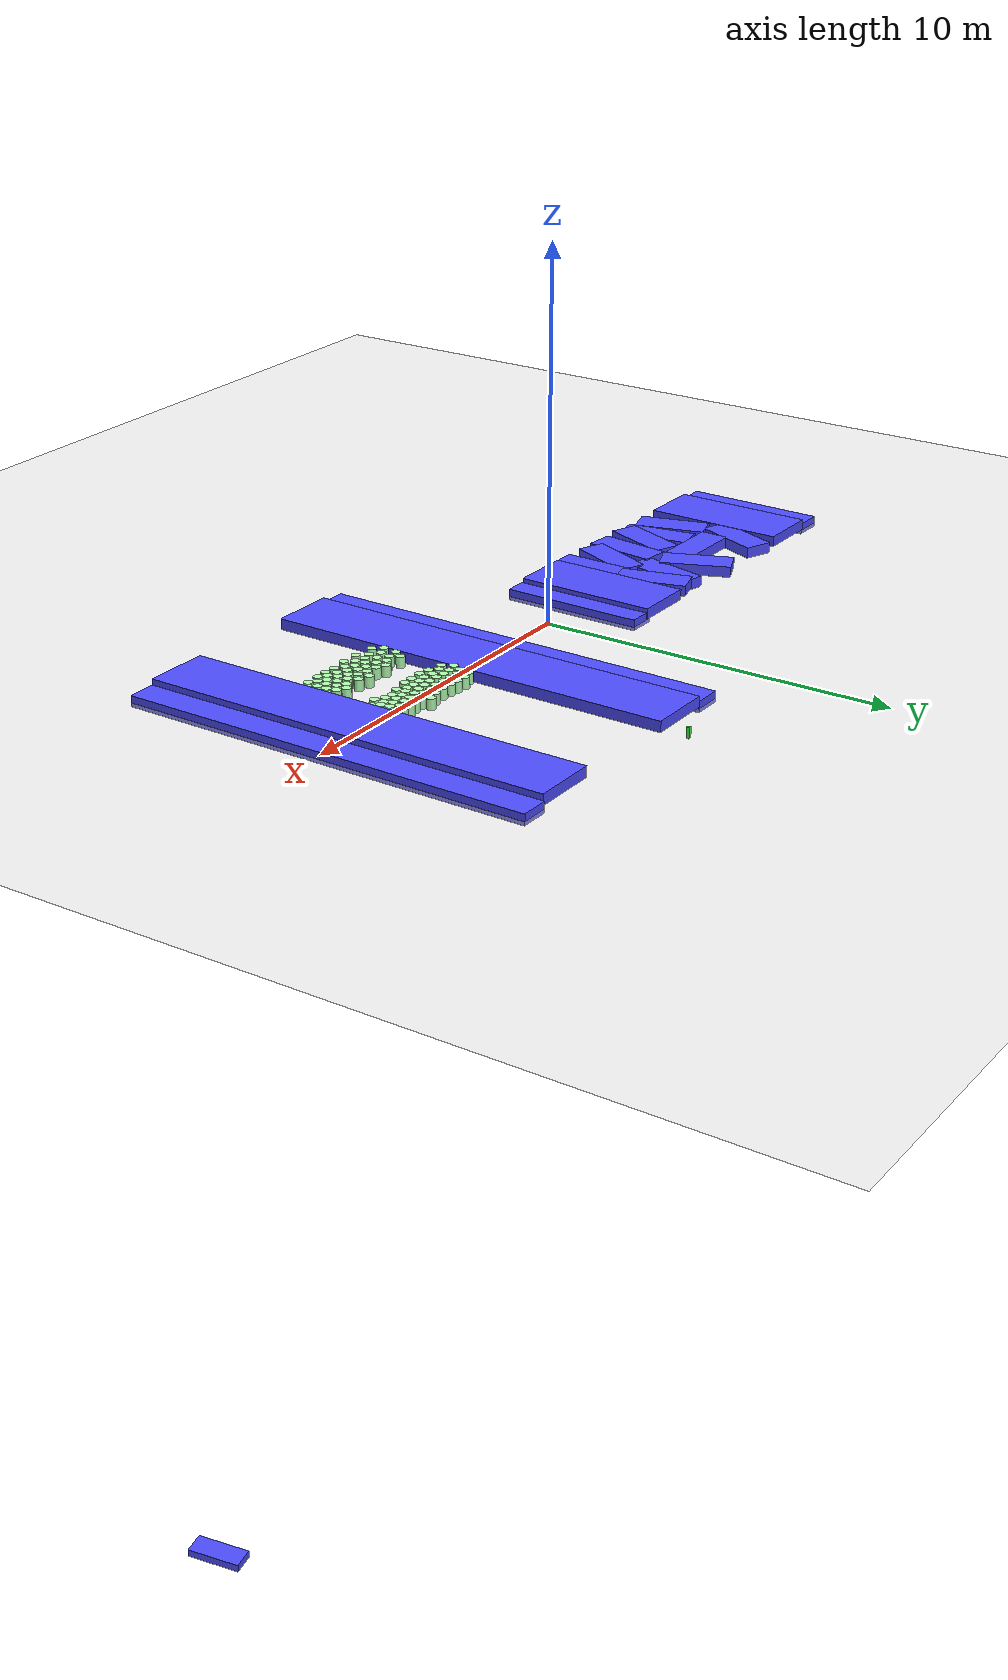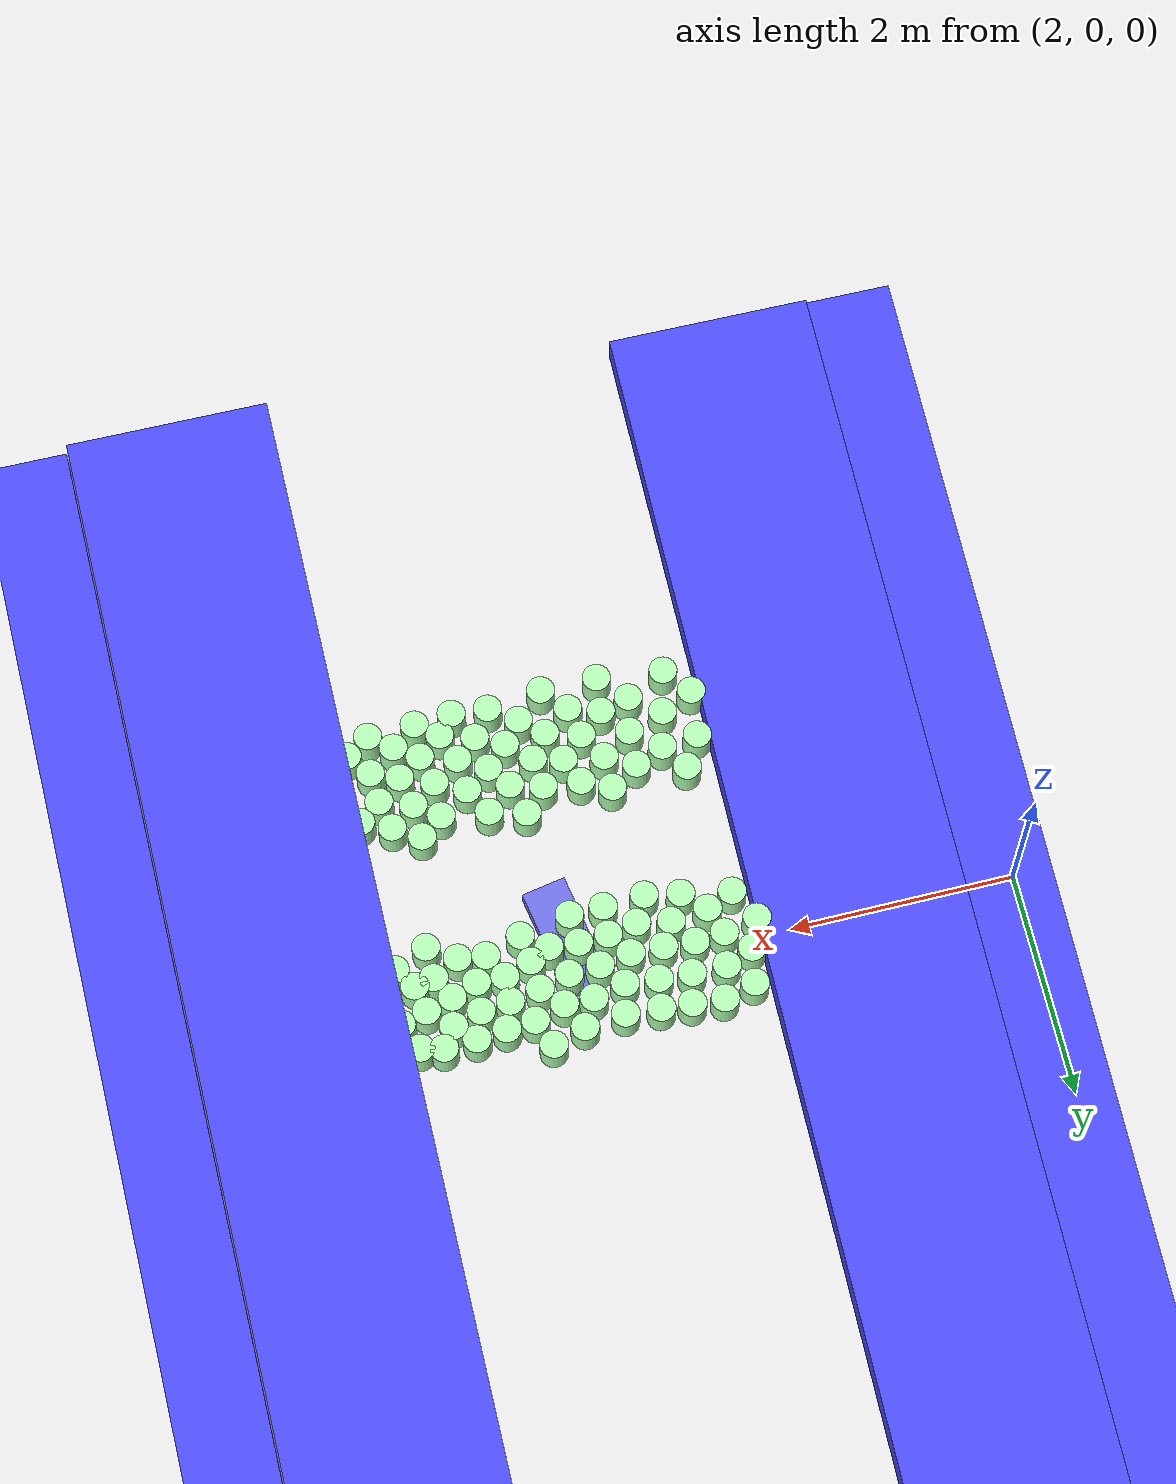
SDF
<sdf version="1.7">
 <world name="default">
  <light name="sun" type="directional">
   <pose>0 0 10 0 -0 0</pose>
   <diffuse>0.8 0.8 0.8 1</diffuse>
   <specular>0.2 0.2 0.2 1</specular>
   <attenuation>
    <range>1000</range>
    <constant>0.9</constant>
    <linear>0.01</linear>
    <quadratic>0.001</quadratic>
   </attenuation>
   <direction>-0.5 0.1 -0.9</direction>
   <spot><inner_angle>0</inner_angle><outer_angle>0</outer_angle><falloff>0</falloff></spot>
  </light>
  <model name="ground_plane">
   <static>1</static>
   <link name="link">
    <collision name="collision">
     <geometry><plane><normal>0 0 1</normal><size>100 100</size></plane></geometry>
     <surface><friction><ode><mu>100</mu><mu2>50</mu2></ode></friction></surface>
    </collision>
    <visual name="visual">
     <cast_shadows>0</cast_shadows>
     <geometry><plane><normal>0 0 1</normal><size>100 100</size></plane></geometry>
     <material>
      <script><uri>file://media/materials/scripts/gazebo.material</uri><name>Gazebo/Grey</name></script>
     </material>
    </visual>
   </link>
  </model>
  <gravity>0 0 -9.8</gravity>
  <magnetic_field>6e-06 2.3e-05 -4.2e-05</magnetic_field>
  <atmosphere type="adiabatic"/>
  <physics type="ode">
   <max_step_size>0.001</max_step_size>
   <real_time_factor>1</real_time_factor>
   <real_time_update_rate>1000</real_time_update_rate>
  </physics>
  <scene><ambient>0.4 0.4 0.4 1</ambient><background>0.7 0.7 0.7 1</background><shadows>1</shadows></scene>
  <spherical_coordinates>
   <surface_model>EARTH_WGS84</surface_model>
   <latitude_deg>0</latitude_deg>
   <longitude_deg>0</longitude_deg>
   <elevation>0</elevation>
   <heading_deg>0</heading_deg>
  </spherical_coordinates>
  <model name="ban_400_80_30">
   <link name="link">
    <inertial>
     <mass>1</mass>
     <inertia>
      <ixx>0.166667</ixx>
      <ixy>0</ixy>
      <ixz>0</ixz>
      <iyy>0.166667</iyy>
      <iyz>0</iyz>
      <izz>0.166667</izz>
     </inertia>
    </inertial>
    <visual name="visual">
     <geometry><box><size>11.7457 0.8 0.3</size></box></geometry>
     <material>
      <script><name>Gazebo/Grey</name><uri>file://media/materials/scripts/gazebo.material</uri></script>
      <shader type="pixel"><normal_map>__default__</normal_map></shader>
      <ambient>0.3 0.3 1 1</ambient>
      <diffuse>0.7 0.7 0.7 1</diffuse>
      <specular>0.01 0.01 0.01 1</specular>
      <emissive>0 0 0 1</emissive>
     </material>
    </visual>
    <collision name="collision">
     <geometry><box><size>11.7457 0.8 0.3</size></box></geometry>
     <surface>
      <friction>
       <ode><mu>1</mu><mu2>1</mu2><fdir1>0 0 0</fdir1><slip1>0</slip1><slip2>0</slip2></ode>
       <torsional>
        <coefficient>1</coefficient>
        <patch_radius>0</patch_radius>
        <surface_radius>0</surface_radius>
        <use_patch_radius>1</use_patch_radius>
        <ode><slip>0</slip></ode>
       </torsional>
      </friction>
      <bounce><restitution_coefficient>0</restitution_coefficient><threshold>1e+06</threshold></bounce>
      <contact>
       <collide_without_contact>0</collide_without_contact>
       <collide_without_contact_bitmask>1</collide_without_contact_bitmask>
       <collide_bitmask>1</collide_bitmask>
       <ode>
        <soft_cfm>0</soft_cfm>
        <soft_erp>0.2</soft_erp>
        <kp>1e+13</kp>
        <kd>1</kd>
        <max_vel>0.01</max_vel>
        <min_depth>0</min_depth>
       </ode>
       <bullet>
        <split_impulse>1</split_impulse>
        <split_impulse_penetration_threshold>-0.01</split_impulse_penetration_threshold>
        <soft_cfm>0</soft_cfm>
        <soft_erp>0.2</soft_erp>
        <kp>1e+13</kp>
        <kd>1</kd>
       </bullet>
      </contact>
     </surface>
    </collision>
   </link>
   <static>1</static>
   <pose>2.06865 0.167126 0 0 -0 1.55763</pose>
  </model>
  <model name="ban_400_80_30_clone_1_clone_0">
   <link name="link">
    <inertial>
     <mass>1</mass>
     <inertia>
      <ixx>0.166667</ixx>
      <ixy>0</ixy>
      <ixz>0</ixz>
      <iyy>0.166667</iyy>
      <iyz>0</iyz>
      <izz>0.166667</izz>
     </inertia>
    </inertial>
    <visual name="visual">
     <geometry><box><size>4 0.8 0.3</size></box></geometry>
     <material>
      <script><name>Gazebo/Grey</name><uri>file://media/materials/scripts/gazebo.material</uri></script>
      <shader type="pixel"><normal_map>__default__</normal_map></shader>
      <ambient>0.3 0.3 1 1</ambient>
      <diffuse>0.7 0.7 0.7 1</diffuse>
      <specular>0.01 0.01 0.01 1</specular>
      <emissive>0 0 0 1</emissive>
     </material>
    </visual>
    <collision name="collision">
     <geometry><box><size>4 0.8 0.3</size></box></geometry>
     <surface>
      <friction>
       <ode><mu>1</mu><mu2>1</mu2><fdir1>0 0 0</fdir1><slip1>0</slip1><slip2>0</slip2></ode>
       <torsional>
        <coefficient>1</coefficient>
        <patch_radius>0</patch_radius>
        <surface_radius>0</surface_radius>
        <use_patch_radius>1</use_patch_radius>
        <ode><slip>0</slip></ode>
       </torsional>
      </friction>
      <bounce><restitution_coefficient>0</restitution_coefficient><threshold>1e+06</threshold></bounce>
      <contact>
       <collide_without_contact>0</collide_without_contact>
       <collide_without_contact_bitmask>1</collide_without_contact_bitmask>
       <collide_bitmask>1</collide_bitmask>
       <ode>
        <soft_cfm>0</soft_cfm>
        <soft_erp>0.2</soft_erp>
        <kp>1e+13</kp>
        <kd>1</kd>
        <max_vel>0.01</max_vel>
        <min_depth>0</min_depth>
       </ode>
       <bullet>
        <split_impulse>1</split_impulse>
        <split_impulse_penetration_threshold>-0.01</split_impulse_penetration_threshold>
        <soft_cfm>0</soft_cfm>
        <soft_erp>0.2</soft_erp>
        <kp>1e+13</kp>
        <kd>1</kd>
       </bullet>
      </contact>
     </surface>
    </collision>
   </link>
   <static>1</static>
   <pose>-1.57197 -0.048811 0.008853 0 -0 1.55763</pose>
  </model>
  <model name="ban_400_80_30_clone_1_clone_1">
   <link name="link">
    <inertial>
     <mass>1</mass>
     <inertia>
      <ixx>0.166667</ixx>
      <ixy>0</ixy>
      <ixz>0</ixz>
      <iyy>0.166667</iyy>
      <iyz>0</iyz>
      <izz>0.166667</izz>
     </inertia>
    </inertial>
    <visual name="visual">
     <geometry><box><size>4 1.73091 0.3</size></box></geometry>
     <material>
      <script><name>Gazebo/Grey</name><uri>file://media/materials/scripts/gazebo.material</uri></script>
      <shader type="pixel"><normal_map>__default__</normal_map></shader>
      <ambient>0.3 0.3 1 1</ambient>
      <diffuse>0.7 0.7 0.7 1</diffuse>
      <specular>0.01 0.01 0.01 1</specular>
      <emissive>0 0 0 1</emissive>
     </material>
    </visual>
    <collision name="collision">
     <geometry><box><size>4 1.73091 0.3</size></box></geometry>
     <surface>
      <friction>
       <ode><mu>1</mu><mu2>1</mu2><fdir1>0 0 0</fdir1><slip1>0</slip1><slip2>0</slip2></ode>
       <torsional>
        <coefficient>1</coefficient>
        <patch_radius>0</patch_radius>
        <surface_radius>0</surface_radius>
        <use_patch_radius>1</use_patch_radius>
        <ode><slip>0</slip></ode>
       </torsional>
      </friction>
      <bounce><restitution_coefficient>0</restitution_coefficient><threshold>1e+06</threshold></bounce>
      <contact>
       <collide_without_contact>0</collide_without_contact>
       <collide_without_contact_bitmask>1</collide_without_contact_bitmask>
       <collide_bitmask>1</collide_bitmask>
       <ode>
        <soft_cfm>0</soft_cfm>
        <soft_erp>0.2</soft_erp>
        <kp>1e+13</kp>
        <kd>1</kd>
        <max_vel>0.01</max_vel>
        <min_depth>0</min_depth>
       </ode>
       <bullet>
        <split_impulse>1</split_impulse>
        <split_impulse_penetration_threshold>-0.01</split_impulse_penetration_threshold>
        <soft_cfm>0</soft_cfm>
        <soft_erp>0.2</soft_erp>
        <kp>1e+13</kp>
        <kd>1</kd>
       </bullet>
      </contact>
     </surface>
    </collision>
   </link>
   <static>1</static>
   <pose>-2.65947 -0.004283 0.133573 0 -0 1.55763</pose>
  </model>
  <model name="ban_200_80_30_clone_8">
   <link name="link">
    <inertial>
     <mass>1</mass>
     <inertia>
      <ixx>0.166667</ixx>
      <ixy>0</ixy>
      <ixz>0</ixz>
      <iyy>0.166667</iyy>
      <iyz>0</iyz>
      <izz>0.166667</izz>
     </inertia>
    </inertial>
    <visual name="visual">
     <geometry><box><size>2 0.8 0.3</size></box></geometry>
     <material>
      <script><name>Gazebo/Grey</name><uri>file://media/materials/scripts/gazebo.material</uri></script>
      <shader type="pixel"><normal_map>__default__</normal_map></shader>
      <ambient>0.3 0.3 1 1</ambient>
      <diffuse>0.7 0.7 0.7 1</diffuse>
      <specular>0.01 0.01 0.01 1</specular>
      <emissive>0 0 0 1</emissive>
     </material>
    </visual>
    <collision name="collision">
     <geometry><box><size>2 0.8 0.3</size></box></geometry>
     <surface>
      <friction>
       <ode><mu>1</mu><mu2>1</mu2><fdir1>0 0 0</fdir1><slip1>0</slip1><slip2>0</slip2></ode>
       <torsional>
        <coefficient>1</coefficient>
        <patch_radius>0</patch_radius>
        <surface_radius>0</surface_radius>
        <use_patch_radius>1</use_patch_radius>
        <ode><slip>0</slip></ode>
       </torsional>
      </friction>
      <bounce><restitution_coefficient>0</restitution_coefficient><threshold>1e+06</threshold></bounce>
      <contact>
       <collide_without_contact>0</collide_without_contact>
       <collide_without_contact_bitmask>1</collide_without_contact_bitmask>
       <collide_bitmask>1</collide_bitmask>
       <ode>
        <soft_cfm>0</soft_cfm>
        <soft_erp>0.2</soft_erp>
        <kp>1e+13</kp>
        <kd>1</kd>
        <max_vel>0.01</max_vel>
        <min_depth>0</min_depth>
       </ode>
       <bullet>
        <split_impulse>1</split_impulse>
        <split_impulse_penetration_threshold>-0.01</split_impulse_penetration_threshold>
        <soft_cfm>0</soft_cfm>
        <soft_erp>0.2</soft_erp>
        <kp>1e+13</kp>
        <kd>1</kd>
       </bullet>
      </contact>
     </surface>
    </collision>
   </link>
   <static>1</static>
   <pose>-3.72567 -0.97739 0.127404 0 0 -1.57453</pose>
  </model>
  <model name="ban_200_80_30_clone_clone">
   <link name="link">
    <inertial>
     <mass>1</mass>
     <inertia>
      <ixx>0.166667</ixx>
      <ixy>0</ixy>
      <ixz>0</ixz>
      <iyy>0.166667</iyy>
      <iyz>0</iyz>
      <izz>0.166667</izz>
     </inertia>
    </inertial>
    <visual name="visual">
     <geometry><box><size>2 0.8 0.3</size></box></geometry>
     <material>
      <script><name>Gazebo/Grey</name><uri>file://media/materials/scripts/gazebo.material</uri></script>
      <shader type="pixel"><normal_map>__default__</normal_map></shader>
      <ambient>0.3 0.3 1 1</ambient>
      <diffuse>0.7 0.7 0.7 1</diffuse>
      <specular>0.01 0.01 0.01 1</specular>
      <emissive>0 0 0 1</emissive>
     </material>
    </visual>
    <collision name="collision">
     <geometry><box><size>2 0.8 0.3</size></box></geometry>
     <surface>
      <friction>
       <ode><mu>1</mu><mu2>1</mu2><fdir1>0 0 0</fdir1><slip1>0</slip1><slip2>0</slip2></ode>
       <torsional>
        <coefficient>1</coefficient>
        <patch_radius>0</patch_radius>
        <surface_radius>0</surface_radius>
        <use_patch_radius>1</use_patch_radius>
        <ode><slip>0</slip></ode>
       </torsional>
      </friction>
      <bounce><restitution_coefficient>0</restitution_coefficient><threshold>1e+06</threshold></bounce>
      <contact>
       <collide_without_contact>0</collide_without_contact>
       <collide_without_contact_bitmask>1</collide_without_contact_bitmask>
       <collide_bitmask>1</collide_bitmask>
       <ode>
        <soft_cfm>0</soft_cfm>
        <soft_erp>0.2</soft_erp>
        <kp>1e+13</kp>
        <kd>1</kd>
        <max_vel>0.01</max_vel>
        <min_depth>0</min_depth>
       </ode>
       <bullet>
        <split_impulse>1</split_impulse>
        <split_impulse_penetration_threshold>-0.01</split_impulse_penetration_threshold>
        <soft_cfm>0</soft_cfm>
        <soft_erp>0.2</soft_erp>
        <kp>1e+13</kp>
        <kd>1</kd>
       </bullet>
      </contact>
     </surface>
    </collision>
   </link>
   <static>1</static>
   <pose>3.32802 -11.2985 -36.3188 0 0 -1.39548</pose>
  </model>
  <model name="ban_200_80_30_clone_clone_clone">
   <link name="link">
    <inertial>
     <mass>1</mass>
     <inertia>
      <ixx>0.166667</ixx>
      <ixy>0</ixy>
      <ixz>0</ixz>
      <iyy>0.166667</iyy>
      <iyz>0</iyz>
      <izz>0.166667</izz>
     </inertia>
    </inertial>
    <visual name="visual">
     <geometry><box><size>2 0.8 0.3</size></box></geometry>
     <material>
      <script><name>Gazebo/Grey</name><uri>file://media/materials/scripts/gazebo.material</uri></script>
      <shader type="pixel"><normal_map>__default__</normal_map></shader>
      <ambient>0.3 0.3 1 1</ambient>
      <diffuse>0.7 0.7 0.7 1</diffuse>
      <specular>0.01 0.01 0.01 1</specular>
      <emissive>0 0 0 1</emissive>
     </material>
    </visual>
    <collision name="collision">
     <geometry><box><size>2 0.8 0.3</size></box></geometry>
     <surface>
      <friction>
       <ode><mu>1</mu><mu2>1</mu2><fdir1>0 0 0</fdir1><slip1>0</slip1><slip2>0</slip2></ode>
       <torsional>
        <coefficient>1</coefficient>
        <patch_radius>0</patch_radius>
        <surface_radius>0</surface_radius>
        <use_patch_radius>1</use_patch_radius>
        <ode><slip>0</slip></ode>
       </torsional>
      </friction>
      <bounce><restitution_coefficient>0</restitution_coefficient><threshold>1e+06</threshold></bounce>
      <contact>
       <collide_without_contact>0</collide_without_contact>
       <collide_without_contact_bitmask>1</collide_without_contact_bitmask>
       <collide_bitmask>1</collide_bitmask>
       <ode>
        <soft_cfm>0</soft_cfm>
        <soft_erp>0.2</soft_erp>
        <kp>1e+13</kp>
        <kd>1</kd>
        <max_vel>0.01</max_vel>
        <min_depth>0</min_depth>
       </ode>
       <bullet>
        <split_impulse>1</split_impulse>
        <split_impulse_penetration_threshold>-0.01</split_impulse_penetration_threshold>
        <soft_cfm>0</soft_cfm>
        <soft_erp>0.2</soft_erp>
        <kp>1e+13</kp>
        <kd>1</kd>
       </bullet>
      </contact>
     </surface>
    </collision>
   </link>
   <static>1</static>
   <pose>-3.88933 0.920751 0.132586 0 0 -1.30462</pose>
  </model>
  <model name="ban_200_80_30_clone_8_clone">
   <link name="link">
    <inertial>
     <mass>1</mass>
     <inertia>
      <ixx>0.166667</ixx>
      <ixy>0</ixy>
      <ixz>0</ixz>
      <iyy>0.166667</iyy>
      <iyz>0</iyz>
      <izz>0.166667</izz>
     </inertia>
    </inertial>
    <visual name="visual">
     <geometry><box><size>2 0.8 0.3</size></box></geometry>
     <material>
      <script><name>Gazebo/Grey</name><uri>file://media/materials/scripts/gazebo.material</uri></script>
      <shader type="pixel"><normal_map>__default__</normal_map></shader>
      <ambient>0.3 0.3 1 1</ambient>
      <diffuse>0.7 0.7 0.7 1</diffuse>
      <specular>0.01 0.01 0.01 1</specular>
      <emissive>0 0 0 1</emissive>
     </material>
    </visual>
    <collision name="collision">
     <geometry><box><size>2 0.8 0.3</size></box></geometry>
     <surface>
      <friction>
       <ode><mu>1</mu><mu2>1</mu2><fdir1>0 0 0</fdir1><slip1>0</slip1><slip2>0</slip2></ode>
       <torsional>
        <coefficient>1</coefficient>
        <patch_radius>0</patch_radius>
        <surface_radius>0</surface_radius>
        <use_patch_radius>1</use_patch_radius>
        <ode><slip>0</slip></ode>
       </torsional>
      </friction>
      <bounce><restitution_coefficient>0</restitution_coefficient><threshold>1e+06</threshold></bounce>
      <contact>
       <collide_without_contact>0</collide_without_contact>
       <collide_without_contact_bitmask>1</collide_without_contact_bitmask>
       <collide_bitmask>1</collide_bitmask>
       <ode>
        <soft_cfm>0</soft_cfm>
        <soft_erp>0.2</soft_erp>
        <kp>1e+13</kp>
        <kd>1</kd>
        <max_vel>0.01</max_vel>
        <min_depth>0</min_depth>
       </ode>
       <bullet>
        <split_impulse>1</split_impulse>
        <split_impulse_penetration_threshold>-0.01</split_impulse_penetration_threshold>
        <soft_cfm>0</soft_cfm>
        <soft_erp>0.2</soft_erp>
        <kp>1e+13</kp>
        <kd>1</kd>
       </bullet>
      </contact>
     </surface>
    </collision>
   </link>
   <static>1</static>
   <pose>-4.62871 -0.899774 0.127404 0 0 -1.97874</pose>
  </model>
  <model name="ban_200_80_30_clone_8_clone_0">
   <link name="link">
    <inertial>
     <mass>1</mass>
     <inertia>
      <ixx>0.166667</ixx>
      <ixy>0</ixy>
      <ixz>0</ixz>
      <iyy>0.166667</iyy>
      <iyz>0</iyz>
      <izz>0.166667</izz>
     </inertia>
    </inertial>
    <visual name="visual">
     <geometry><box><size>2 0.8 0.3</size></box></geometry>
     <material>
      <script><name>Gazebo/Grey</name><uri>file://media/materials/scripts/gazebo.material</uri></script>
      <shader type="pixel"><normal_map>__default__</normal_map></shader>
      <ambient>0.3 0.3 1 1</ambient>
      <diffuse>0.7 0.7 0.7 1</diffuse>
      <specular>0.01 0.01 0.01 1</specular>
      <emissive>0 0 0 1</emissive>
     </material>
    </visual>
    <collision name="collision">
     <geometry><box><size>2 0.8 0.3</size></box></geometry>
     <surface>
      <friction>
       <ode><mu>1</mu><mu2>1</mu2><fdir1>0 0 0</fdir1><slip1>0</slip1><slip2>0</slip2></ode>
       <torsional>
        <coefficient>1</coefficient>
        <patch_radius>0</patch_radius>
        <surface_radius>0</surface_radius>
        <use_patch_radius>1</use_patch_radius>
        <ode><slip>0</slip></ode>
       </torsional>
      </friction>
      <bounce><restitution_coefficient>0</restitution_coefficient><threshold>1e+06</threshold></bounce>
      <contact>
       <collide_without_contact>0</collide_without_contact>
       <collide_without_contact_bitmask>1</collide_without_contact_bitmask>
       <collide_bitmask>1</collide_bitmask>
       <ode>
        <soft_cfm>0</soft_cfm>
        <soft_erp>0.2</soft_erp>
        <kp>1e+13</kp>
        <kd>1</kd>
        <max_vel>0.01</max_vel>
        <min_depth>0</min_depth>
       </ode>
       <bullet>
        <split_impulse>1</split_impulse>
        <split_impulse_penetration_threshold>-0.01</split_impulse_penetration_threshold>
        <soft_cfm>0</soft_cfm>
        <soft_erp>0.2</soft_erp>
        <kp>1e+13</kp>
        <kd>1</kd>
       </bullet>
      </contact>
     </surface>
    </collision>
   </link>
   <static>1</static>
   <pose>-4.633 0.844905 0.090917 0 0 -1.81122</pose>
  </model>
  <model name="ban_200_80_30_clone_8_clone_1">
   <link name="link">
    <inertial>
     <mass>1</mass>
     <inertia>
      <ixx>0.166667</ixx>
      <ixy>0</ixy>
      <ixz>0</ixz>
      <iyy>0.166667</iyy>
      <iyz>0</iyz>
      <izz>0.166667</izz>
     </inertia>
    </inertial>
    <visual name="visual">
     <geometry><box><size>2 0.8 0.3</size></box></geometry>
     <material>
      <script><name>Gazebo/Grey</name><uri>file://media/materials/scripts/gazebo.material</uri></script>
      <shader type="pixel"><normal_map>__default__</normal_map></shader>
      <ambient>0.3 0.3 1 1</ambient>
      <diffuse>0.7 0.7 0.7 1</diffuse>
      <specular>0.01 0.01 0.01 1</specular>
      <emissive>0 0 0 1</emissive>
     </material>
    </visual>
    <collision name="collision">
     <geometry><box><size>2 0.8 0.3</size></box></geometry>
     <surface>
      <friction>
       <ode><mu>1</mu><mu2>1</mu2><fdir1>0 0 0</fdir1><slip1>0</slip1><slip2>0</slip2></ode>
       <torsional>
        <coefficient>1</coefficient>
        <patch_radius>0</patch_radius>
        <surface_radius>0</surface_radius>
        <use_patch_radius>1</use_patch_radius>
        <ode><slip>0</slip></ode>
       </torsional>
      </friction>
      <bounce><restitution_coefficient>0</restitution_coefficient><threshold>1e+06</threshold></bounce>
      <contact>
       <collide_without_contact>0</collide_without_contact>
       <collide_without_contact_bitmask>1</collide_without_contact_bitmask>
       <collide_bitmask>1</collide_bitmask>
       <ode>
        <soft_cfm>0</soft_cfm>
        <soft_erp>0.2</soft_erp>
        <kp>1e+13</kp>
        <kd>1</kd>
        <max_vel>0.01</max_vel>
        <min_depth>0</min_depth>
       </ode>
       <bullet>
        <split_impulse>1</split_impulse>
        <split_impulse_penetration_threshold>-0.01</split_impulse_penetration_threshold>
        <soft_cfm>0</soft_cfm>
        <soft_erp>0.2</soft_erp>
        <kp>1e+13</kp>
        <kd>1</kd>
       </bullet>
      </contact>
     </surface>
    </collision>
   </link>
   <static>1</static>
   <pose>-5.73665 1.22455 0.127404 0 0 -1.18182</pose>
  </model>
  <model name="ban_200_80_30_clone_8_clone_2">
   <link name="link">
    <inertial>
     <mass>1</mass>
     <inertia>
      <ixx>0.166667</ixx>
      <ixy>0</ixy>
      <ixz>0</ixz>
      <iyy>0.166667</iyy>
      <iyz>0</iyz>
      <izz>0.166667</izz>
     </inertia>
    </inertial>
    <visual name="visual">
     <geometry><box><size>2 0.8 0.3</size></box></geometry>
     <material>
      <script><name>Gazebo/Grey</name><uri>file://media/materials/scripts/gazebo.material</uri></script>
      <shader type="pixel"><normal_map>__default__</normal_map></shader>
      <ambient>0.3 0.3 1 1</ambient>
      <diffuse>0.7 0.7 0.7 1</diffuse>
      <specular>0.01 0.01 0.01 1</specular>
      <emissive>0 0 0 1</emissive>
     </material>
    </visual>
    <collision name="collision">
     <geometry><box><size>2 0.8 0.3</size></box></geometry>
     <surface>
      <friction>
       <ode><mu>1</mu><mu2>1</mu2><fdir1>0 0 0</fdir1><slip1>0</slip1><slip2>0</slip2></ode>
       <torsional>
        <coefficient>1</coefficient>
        <patch_radius>0</patch_radius>
        <surface_radius>0</surface_radius>
        <use_patch_radius>1</use_patch_radius>
        <ode><slip>0</slip></ode>
       </torsional>
      </friction>
      <bounce><restitution_coefficient>0</restitution_coefficient><threshold>1e+06</threshold></bounce>
      <contact>
       <collide_without_contact>0</collide_without_contact>
       <collide_without_contact_bitmask>1</collide_without_contact_bitmask>
       <collide_bitmask>1</collide_bitmask>
       <ode>
        <soft_cfm>0</soft_cfm>
        <soft_erp>0.2</soft_erp>
        <kp>1e+13</kp>
        <kd>1</kd>
        <max_vel>0.01</max_vel>
        <min_depth>0</min_depth>
       </ode>
       <bullet>
        <split_impulse>1</split_impulse>
        <split_impulse_penetration_threshold>-0.01</split_impulse_penetration_threshold>
        <soft_cfm>0</soft_cfm>
        <soft_erp>0.2</soft_erp>
        <kp>1e+13</kp>
        <kd>1</kd>
       </bullet>
      </contact>
     </surface>
    </collision>
   </link>
   <static>1</static>
   <pose>-5.49836 -0.904422 0.127404 0 0 -1.68677</pose>
  </model>
  <model name="ban_200_80_30_clone_8_clone_3">
   <link name="link">
    <inertial>
     <mass>1</mass>
     <inertia>
      <ixx>0.166667</ixx>
      <ixy>0</ixy>
      <ixz>0</ixz>
      <iyy>0.166667</iyy>
      <iyz>0</iyz>
      <izz>0.166667</izz>
     </inertia>
    </inertial>
    <visual name="visual">
     <geometry><box><size>2 0.8 0.3</size></box></geometry>
     <material>
      <script><name>Gazebo/Grey</name><uri>file://media/materials/scripts/gazebo.material</uri></script>
      <shader type="pixel"><normal_map>__default__</normal_map></shader>
      <ambient>0.3 0.3 1 1</ambient>
      <diffuse>0.7 0.7 0.7 1</diffuse>
      <specular>0.01 0.01 0.01 1</specular>
      <emissive>0 0 0 1</emissive>
     </material>
    </visual>
    <collision name="collision">
     <geometry><box><size>2 0.8 0.3</size></box></geometry>
     <surface>
      <friction>
       <ode><mu>1</mu><mu2>1</mu2><fdir1>0 0 0</fdir1><slip1>0</slip1><slip2>0</slip2></ode>
       <torsional>
        <coefficient>1</coefficient>
        <patch_radius>0</patch_radius>
        <surface_radius>0</surface_radius>
        <use_patch_radius>1</use_patch_radius>
        <ode><slip>0</slip></ode>
       </torsional>
      </friction>
      <bounce><restitution_coefficient>0</restitution_coefficient><threshold>1e+06</threshold></bounce>
      <contact>
       <collide_without_contact>0</collide_without_contact>
       <collide_without_contact_bitmask>1</collide_without_contact_bitmask>
       <collide_bitmask>1</collide_bitmask>
       <ode>
        <soft_cfm>0</soft_cfm>
        <soft_erp>0.2</soft_erp>
        <kp>1e+13</kp>
        <kd>1</kd>
        <max_vel>0.01</max_vel>
        <min_depth>0</min_depth>
       </ode>
       <bullet>
        <split_impulse>1</split_impulse>
        <split_impulse_penetration_threshold>-0.01</split_impulse_penetration_threshold>
        <soft_cfm>0</soft_cfm>
        <soft_erp>0.2</soft_erp>
        <kp>1e+13</kp>
        <kd>1</kd>
       </bullet>
      </contact>
     </surface>
    </collision>
   </link>
   <static>1</static>
   <pose>-6.45605 -0.8792 0.127404 0 0 -1.94218</pose>
  </model>
  <model name="ban_200_80_30_clone_8_clone_clone">
   <link name="link">
    <inertial>
     <mass>1</mass>
     <inertia>
      <ixx>0.166667</ixx>
      <ixy>0</ixy>
      <ixz>0</ixz>
      <iyy>0.166667</iyy>
      <iyz>0</iyz>
      <izz>0.166667</izz>
     </inertia>
    </inertial>
    <visual name="visual">
     <geometry><box><size>2 0.8 0.3</size></box></geometry>
     <material>
      <script><name>Gazebo/Grey</name><uri>file://media/materials/scripts/gazebo.material</uri></script>
      <shader type="pixel"><normal_map>__default__</normal_map></shader>
      <ambient>0.3 0.3 1 1</ambient>
      <diffuse>0.7 0.7 0.7 1</diffuse>
      <specular>0.01 0.01 0.01 1</specular>
      <emissive>0 0 0 1</emissive>
     </material>
    </visual>
    <collision name="collision">
     <geometry><box><size>2 0.8 0.3</size></box></geometry>
     <surface>
      <friction>
       <ode><mu>1</mu><mu2>1</mu2><fdir1>0 0 0</fdir1><slip1>0</slip1><slip2>0</slip2></ode>
       <torsional>
        <coefficient>1</coefficient>
        <patch_radius>0</patch_radius>
        <surface_radius>0</surface_radius>
        <use_patch_radius>1</use_patch_radius>
        <ode><slip>0</slip></ode>
       </torsional>
      </friction>
      <bounce><restitution_coefficient>0</restitution_coefficient><threshold>1e+06</threshold></bounce>
      <contact>
       <collide_without_contact>0</collide_without_contact>
       <collide_without_contact_bitmask>1</collide_without_contact_bitmask>
       <collide_bitmask>1</collide_bitmask>
       <ode>
        <soft_cfm>0</soft_cfm>
        <soft_erp>0.2</soft_erp>
        <kp>1e+13</kp>
        <kd>1</kd>
        <max_vel>0.01</max_vel>
        <min_depth>0</min_depth>
       </ode>
       <bullet>
        <split_impulse>1</split_impulse>
        <split_impulse_penetration_threshold>-0.01</split_impulse_penetration_threshold>
        <soft_cfm>0</soft_cfm>
        <soft_erp>0.2</soft_erp>
        <kp>1e+13</kp>
        <kd>1</kd>
       </bullet>
      </contact>
     </surface>
    </collision>
   </link>
   <static>1</static>
   <pose>-6.81115 0.60983 0.127404 0 -0 3.12114</pose>
  </model>
  <model name="ban_200_80_30_clone_8_clone_4">
   <link name="link">
    <inertial>
     <mass>1</mass>
     <inertia>
      <ixx>0.166667</ixx>
      <ixy>0</ixy>
      <ixz>0</ixz>
      <iyy>0.166667</iyy>
      <iyz>0</iyz>
      <izz>0.166667</izz>
     </inertia>
    </inertial>
    <visual name="visual">
     <geometry><box><size>2 0.8 0.3</size></box></geometry>
     <material>
      <script><name>Gazebo/Grey</name><uri>file://media/materials/scripts/gazebo.material</uri></script>
      <shader type="pixel"><normal_map>__default__</normal_map></shader>
      <ambient>0.3 0.3 1 1</ambient>
      <diffuse>0.7 0.7 0.7 1</diffuse>
      <specular>0.01 0.01 0.01 1</specular>
      <emissive>0 0 0 1</emissive>
     </material>
    </visual>
    <collision name="collision">
     <geometry><box><size>2 0.8 0.3</size></box></geometry>
     <surface>
      <friction>
       <ode><mu>1</mu><mu2>1</mu2><fdir1>0 0 0</fdir1><slip1>0</slip1><slip2>0</slip2></ode>
       <torsional>
        <coefficient>1</coefficient>
        <patch_radius>0</patch_radius>
        <surface_radius>0</surface_radius>
        <use_patch_radius>1</use_patch_radius>
        <ode><slip>0</slip></ode>
       </torsional>
      </friction>
      <bounce><restitution_coefficient>0</restitution_coefficient><threshold>1e+06</threshold></bounce>
      <contact>
       <collide_without_contact>0</collide_without_contact>
       <collide_without_contact_bitmask>1</collide_without_contact_bitmask>
       <collide_bitmask>1</collide_bitmask>
       <ode>
        <soft_cfm>0</soft_cfm>
        <soft_erp>0.2</soft_erp>
        <kp>1e+13</kp>
        <kd>1</kd>
        <max_vel>0.01</max_vel>
        <min_depth>0</min_depth>
       </ode>
       <bullet>
        <split_impulse>1</split_impulse>
        <split_impulse_penetration_threshold>-0.01</split_impulse_penetration_threshold>
        <soft_cfm>0</soft_cfm>
        <soft_erp>0.2</soft_erp>
        <kp>1e+13</kp>
        <kd>1</kd>
       </bullet>
      </contact>
     </surface>
    </collision>
   </link>
   <static>1</static>
   <pose>-6.98812 -0.792101 0.127404 0 0 -1.40582</pose>
  </model>
  <model name="ban_200_80_30_clone_8_clone_5">
   <link name="link">
    <inertial>
     <mass>1</mass>
     <inertia>
      <ixx>0.166667</ixx>
      <ixy>0</ixy>
      <ixz>0</ixz>
      <iyy>0.166667</iyy>
      <iyz>0</iyz>
      <izz>0.166667</izz>
     </inertia>
    </inertial>
    <visual name="visual">
     <geometry><box><size>2 0.8 0.3</size></box></geometry>
     <material>
      <script><name>Gazebo/Grey</name><uri>file://media/materials/scripts/gazebo.material</uri></script>
      <shader type="pixel"><normal_map>__default__</normal_map></shader>
      <ambient>0.3 0.3 1 1</ambient>
      <diffuse>0.7 0.7 0.7 1</diffuse>
      <specular>0.01 0.01 0.01 1</specular>
      <emissive>0 0 0 1</emissive>
     </material>
    </visual>
    <collision name="collision">
     <geometry><box><size>2 0.8 0.3</size></box></geometry>
     <surface>
      <friction>
       <ode><mu>1</mu><mu2>1</mu2><fdir1>0 0 0</fdir1><slip1>0</slip1><slip2>0</slip2></ode>
       <torsional>
        <coefficient>1</coefficient>
        <patch_radius>0</patch_radius>
        <surface_radius>0</surface_radius>
        <use_patch_radius>1</use_patch_radius>
        <ode><slip>0</slip></ode>
       </torsional>
      </friction>
      <bounce><restitution_coefficient>0</restitution_coefficient><threshold>1e+06</threshold></bounce>
      <contact>
       <collide_without_contact>0</collide_without_contact>
       <collide_without_contact_bitmask>1</collide_without_contact_bitmask>
       <collide_bitmask>1</collide_bitmask>
       <ode>
        <soft_cfm>0</soft_cfm>
        <soft_erp>0.2</soft_erp>
        <kp>1e+13</kp>
        <kd>1</kd>
        <max_vel>0.01</max_vel>
        <min_depth>0</min_depth>
       </ode>
       <bullet>
        <split_impulse>1</split_impulse>
        <split_impulse_penetration_threshold>-0.01</split_impulse_penetration_threshold>
        <soft_cfm>0</soft_cfm>
        <soft_erp>0.2</soft_erp>
        <kp>1e+13</kp>
        <kd>1</kd>
       </bullet>
      </contact>
     </surface>
    </collision>
   </link>
   <static>1</static>
   <pose>-7.894 -0.825962 0.127404 0 0 -1.29358</pose>
  </model>
  <model name="ban_400_80_30_clone_1_clone_1_clone">
   <link name="link">
    <inertial>
     <mass>1</mass>
     <inertia>
      <ixx>0.166667</ixx>
      <ixy>0</ixy>
      <ixz>0</ixz>
      <iyy>0.166667</iyy>
      <iyz>0</iyz>
      <izz>0.166667</izz>
     </inertia>
    </inertial>
    <visual name="visual">
     <geometry><box><size>4 1.74854 0.3</size></box></geometry>
     <material>
      <script><name>Gazebo/Grey</name><uri>file://media/materials/scripts/gazebo.material</uri></script>
      <shader type="pixel"><normal_map>__default__</normal_map></shader>
      <ambient>0.3 0.3 1 1</ambient>
      <diffuse>0.7 0.7 0.7 1</diffuse>
      <specular>0.01 0.01 0.01 1</specular>
      <emissive>0 0 0 1</emissive>
     </material>
    </visual>
    <collision name="collision">
     <geometry><box><size>4 1.74854 0.3</size></box></geometry>
     <surface>
      <friction>
       <ode><mu>1</mu><mu2>1</mu2><fdir1>0 0 0</fdir1><slip1>0</slip1><slip2>0</slip2></ode>
       <torsional>
        <coefficient>1</coefficient>
        <patch_radius>0</patch_radius>
        <surface_radius>0</surface_radius>
        <use_patch_radius>1</use_patch_radius>
        <ode><slip>0</slip></ode>
       </torsional>
      </friction>
      <bounce><restitution_coefficient>0</restitution_coefficient><threshold>1e+06</threshold></bounce>
      <contact>
       <collide_without_contact>0</collide_without_contact>
       <collide_without_contact_bitmask>1</collide_without_contact_bitmask>
       <collide_bitmask>1</collide_bitmask>
       <ode>
        <soft_cfm>0</soft_cfm>
        <soft_erp>0.2</soft_erp>
        <kp>1e+13</kp>
        <kd>1</kd>
        <max_vel>0.01</max_vel>
        <min_depth>0</min_depth>
       </ode>
       <bullet>
        <split_impulse>1</split_impulse>
        <split_impulse_penetration_threshold>-0.01</split_impulse_penetration_threshold>
        <soft_cfm>0</soft_cfm>
        <soft_erp>0.2</soft_erp>
        <kp>1e+13</kp>
        <kd>1</kd>
       </bullet>
      </contact>
     </surface>
    </collision>
   </link>
   <static>1</static>
   <pose>-9.45404 0.147213 0.133573 0 -0 1.55763</pose>
  </model>
  <model name="ban_400_80_30_clone_1_clone_1_clone_0">
   <link name="link">
    <inertial>
     <mass>1</mass>
     <inertia>
      <ixx>0.166667</ixx>
      <ixy>0</ixy>
      <ixz>0</ixz>
      <iyy>0.166667</iyy>
      <iyz>0</iyz>
      <izz>0.166667</izz>
     </inertia>
    </inertial>
    <visual name="visual">
     <geometry><box><size>4 0.8 0.3</size></box></geometry>
     <material>
      <script><name>Gazebo/Grey</name><uri>file://media/materials/scripts/gazebo.material</uri></script>
      <shader type="pixel"><normal_map>__default__</normal_map></shader>
      <ambient>0.3 0.3 1 1</ambient>
      <diffuse>0.7 0.7 0.7 1</diffuse>
      <specular>0.01 0.01 0.01 1</specular>
      <emissive>0 0 0 1</emissive>
     </material>
    </visual>
    <collision name="collision">
     <geometry><box><size>4 0.8 0.3</size></box></geometry>
     <surface>
      <friction>
       <ode><mu>1</mu><mu2>1</mu2><fdir1>0 0 0</fdir1><slip1>0</slip1><slip2>0</slip2></ode>
       <torsional>
        <coefficient>1</coefficient>
        <patch_radius>0</patch_radius>
        <surface_radius>0</surface_radius>
        <use_patch_radius>1</use_patch_radius>
        <ode><slip>0</slip></ode>
       </torsional>
      </friction>
      <bounce><restitution_coefficient>0</restitution_coefficient><threshold>1e+06</threshold></bounce>
      <contact>
       <collide_without_contact>0</collide_without_contact>
       <collide_without_contact_bitmask>1</collide_without_contact_bitmask>
       <collide_bitmask>1</collide_bitmask>
       <ode>
        <soft_cfm>0</soft_cfm>
        <soft_erp>0.2</soft_erp>
        <kp>1e+13</kp>
        <kd>1</kd>
        <max_vel>0.01</max_vel>
        <min_depth>0</min_depth>
       </ode>
       <bullet>
        <split_impulse>1</split_impulse>
        <split_impulse_penetration_threshold>-0.01</split_impulse_penetration_threshold>
        <soft_cfm>0</soft_cfm>
        <soft_erp>0.2</soft_erp>
        <kp>1e+13</kp>
        <kd>1</kd>
       </bullet>
      </contact>
     </surface>
    </collision>
   </link>
   <static>1</static>
   <pose>-10.7244 0.139814 -0.002327 0 -0 1.55763</pose>
  </model>
  <model name="ban_200_80_30_clone_8_clone_5_clone">
   <link name="link">
    <inertial>
     <mass>1</mass>
     <inertia>
      <ixx>0.166667</ixx>
      <ixy>0</ixy>
      <ixz>0</ixz>
      <iyy>0.166667</iyy>
      <iyz>0</iyz>
      <izz>0.166667</izz>
     </inertia>
    </inertial>
    <visual name="visual">
     <geometry><box><size>2 0.8 0.3</size></box></geometry>
     <material>
      <script><name>Gazebo/Grey</name><uri>file://media/materials/scripts/gazebo.material</uri></script>
      <shader type="pixel"><normal_map>__default__</normal_map></shader>
      <ambient>0.3 0.3 1 1</ambient>
      <diffuse>0.7 0.7 0.7 1</diffuse>
      <specular>0.01 0.01 0.01 1</specular>
      <emissive>0 0 0 1</emissive>
     </material>
    </visual>
    <collision name="collision">
     <geometry><box><size>2 0.8 0.3</size></box></geometry>
     <surface>
      <friction>
       <ode><mu>1</mu><mu2>1</mu2><fdir1>0 0 0</fdir1><slip1>0</slip1><slip2>0</slip2></ode>
       <torsional>
        <coefficient>1</coefficient>
        <patch_radius>0</patch_radius>
        <surface_radius>0</surface_radius>
        <use_patch_radius>1</use_patch_radius>
        <ode><slip>0</slip></ode>
       </torsional>
      </friction>
      <bounce><restitution_coefficient>0</restitution_coefficient><threshold>1e+06</threshold></bounce>
      <contact>
       <collide_without_contact>0</collide_without_contact>
       <collide_without_contact_bitmask>1</collide_without_contact_bitmask>
       <collide_bitmask>1</collide_bitmask>
       <ode>
        <soft_cfm>0</soft_cfm>
        <soft_erp>0.2</soft_erp>
        <kp>1e+13</kp>
        <kd>1</kd>
        <max_vel>0.01</max_vel>
        <min_depth>0</min_depth>
       </ode>
       <bullet>
        <split_impulse>1</split_impulse>
        <split_impulse_penetration_threshold>-0.01</split_impulse_penetration_threshold>
        <soft_cfm>0</soft_cfm>
        <soft_erp>0.2</soft_erp>
        <kp>1e+13</kp>
        <kd>1</kd>
       </bullet>
      </contact>
     </surface>
    </collision>
   </link>
   <static>1</static>
   <pose>-8.09115 1.18916 0.127404 0 0 -1.95628</pose>
  </model>
  <model name="ban_400_80_30_clone_clone">
   <link name="link">
    <inertial>
     <mass>1</mass>
     <inertia>
      <ixx>0.166667</ixx>
      <ixy>0</ixy>
      <ixz>0</ixz>
      <iyy>0.166667</iyy>
      <iyz>0</iyz>
      <izz>0.166667</izz>
     </inertia>
    </inertial>
    <visual name="visual">
     <geometry><box><size>11.703 1.83242 0.3</size></box></geometry>
     <material>
      <script><name>Gazebo/Grey</name><uri>file://media/materials/scripts/gazebo.material</uri></script>
      <shader type="pixel"><normal_map>__default__</normal_map></shader>
      <ambient>0.3 0.3 1 1</ambient>
      <diffuse>0.7 0.7 0.7 1</diffuse>
      <specular>0.01 0.01 0.01 1</specular>
      <emissive>0 0 0 1</emissive>
     </material>
    </visual>
    <collision name="collision">
     <geometry><box><size>11.703 1.83242 0.3</size></box></geometry>
     <surface>
      <friction>
       <ode><mu>1</mu><mu2>1</mu2><fdir1>0 0 0</fdir1><slip1>0</slip1><slip2>0</slip2></ode>
       <torsional>
        <coefficient>1</coefficient>
        <patch_radius>0</patch_radius>
        <surface_radius>0</surface_radius>
        <use_patch_radius>1</use_patch_radius>
        <ode><slip>0</slip></ode>
       </torsional>
      </friction>
      <bounce><restitution_coefficient>0</restitution_coefficient><threshold>1e+06</threshold></bounce>
      <contact>
       <collide_without_contact>0</collide_without_contact>
       <collide_without_contact_bitmask>1</collide_without_contact_bitmask>
       <collide_bitmask>1</collide_bitmask>
       <ode>
        <soft_cfm>0</soft_cfm>
        <soft_erp>0.2</soft_erp>
        <kp>1e+13</kp>
        <kd>1</kd>
        <max_vel>0.01</max_vel>
        <min_depth>0</min_depth>
       </ode>
       <bullet>
        <split_impulse>1</split_impulse>
        <split_impulse_penetration_threshold>-0.01</split_impulse_penetration_threshold>
        <soft_cfm>0</soft_cfm>
        <soft_erp>0.2</soft_erp>
        <kp>1e+13</kp>
        <kd>1</kd>
       </bullet>
      </contact>
     </surface>
    </collision>
   </link>
   <static>1</static>
   <pose>3.376 0.164957 0.141155 0 -0 1.55763</pose>
  </model>
  <model name="ban_400_80_30_clone_clone_clone">
   <link name="link">
    <inertial>
     <mass>1</mass>
     <inertia>
      <ixx>0.166667</ixx>
      <ixy>0</ixy>
      <ixz>0</ixz>
      <iyy>0.166667</iyy>
      <iyz>0</iyz>
      <izz>0.166667</izz>
     </inertia>
    </inertial>
    <visual name="visual">
     <geometry><box><size>11.703 1.83242 0.3</size></box></geometry>
     <material>
      <script><name>Gazebo/Grey</name><uri>file://media/materials/scripts/gazebo.material</uri></script>
      <shader type="pixel"><normal_map>__default__</normal_map></shader>
      <ambient>0.3 0.3 1 1</ambient>
      <diffuse>0.7 0.7 0.7 1</diffuse>
      <specular>0.01 0.01 0.01 1</specular>
      <emissive>0 0 0 1</emissive>
     </material>
    </visual>
    <collision name="collision">
     <geometry><box><size>11.703 1.83242 0.3</size></box></geometry>
     <surface>
      <friction>
       <ode><mu>1</mu><mu2>1</mu2><fdir1>0 0 0</fdir1><slip1>0</slip1><slip2>0</slip2></ode>
       <torsional>
        <coefficient>1</coefficient>
        <patch_radius>0</patch_radius>
        <surface_radius>0</surface_radius>
        <use_patch_radius>1</use_patch_radius>
        <ode><slip>0</slip></ode>
       </torsional>
      </friction>
      <bounce><restitution_coefficient>0</restitution_coefficient><threshold>1e+06</threshold></bounce>
      <contact>
       <collide_without_contact>0</collide_without_contact>
       <collide_without_contact_bitmask>1</collide_without_contact_bitmask>
       <collide_bitmask>1</collide_bitmask>
       <ode>
        <soft_cfm>0</soft_cfm>
        <soft_erp>0.2</soft_erp>
        <kp>1e+13</kp>
        <kd>1</kd>
        <max_vel>0.01</max_vel>
        <min_depth>0</min_depth>
       </ode>
       <bullet>
        <split_impulse>1</split_impulse>
        <split_impulse_penetration_threshold>-0.01</split_impulse_penetration_threshold>
        <soft_cfm>0</soft_cfm>
        <soft_erp>0.2</soft_erp>
        <kp>1e+13</kp>
        <kd>1</kd>
       </bullet>
      </contact>
     </surface>
    </collision>
   </link>
   <static>1</static>
   <pose>8.35251 0.000658 0.15556 0 -0 1.55763</pose>
  </model>
  <model name="ban_400_80_30_clone">
   <link name="link">
    <inertial>
     <mass>1</mass>
     <inertia>
      <ixx>0.166667</ixx>
      <ixy>0</ixy>
      <ixz>0</ixz>
      <iyy>0.166667</iyy>
      <iyz>0</iyz>
      <izz>0.166667</izz>
     </inertia>
    </inertial>
    <visual name="visual">
     <geometry><box><size>11.7457 0.8 0.3</size></box></geometry>
     <material>
      <script><name>Gazebo/Grey</name><uri>file://media/materials/scripts/gazebo.material</uri></script>
      <shader type="pixel"><normal_map>__default__</normal_map></shader>
      <ambient>0.3 0.3 1 1</ambient>
      <diffuse>0.7 0.7 0.7 1</diffuse>
      <specular>0.01 0.01 0.01 1</specular>
      <emissive>0 0 0 1</emissive>
     </material>
    </visual>
    <collision name="collision">
     <geometry><box><size>11.7457 0.8 0.3</size></box></geometry>
     <surface>
      <friction>
       <ode><mu>1</mu><mu2>1</mu2><fdir1>0 0 0</fdir1><slip1>0</slip1><slip2>0</slip2></ode>
       <torsional>
        <coefficient>1</coefficient>
        <patch_radius>0</patch_radius>
        <surface_radius>0</surface_radius>
        <use_patch_radius>1</use_patch_radius>
        <ode><slip>0</slip></ode>
       </torsional>
      </friction>
      <bounce><restitution_coefficient>0</restitution_coefficient><threshold>1e+06</threshold></bounce>
      <contact>
       <collide_without_contact>0</collide_without_contact>
       <collide_without_contact_bitmask>1</collide_without_contact_bitmask>
       <collide_bitmask>1</collide_bitmask>
       <ode>
        <soft_cfm>0</soft_cfm>
        <soft_erp>0.2</soft_erp>
        <kp>1e+13</kp>
        <kd>1</kd>
        <max_vel>0.01</max_vel>
        <min_depth>0</min_depth>
       </ode>
       <bullet>
        <split_impulse>1</split_impulse>
        <split_impulse_penetration_threshold>-0.01</split_impulse_penetration_threshold>
        <soft_cfm>0</soft_cfm>
        <soft_erp>0.2</soft_erp>
        <kp>1e+13</kp>
        <kd>1</kd>
       </bullet>
      </contact>
     </surface>
    </collision>
   </link>
   <static>1</static>
   <pose>9.68721 0.016567 0 0 -0 1.55763</pose>
  </model>
  <model name="mhz_y_25_30">
   <link name="link">
    <inertial>
     <mass>1</mass>
     <inertia><ixx>0.145833</ixx><ixy>0</ixy><ixz>0</ixz><iyy>0.145833</iyy><iyz>0</iyz><izz>0.125</izz></inertia>
    </inertial>
    <visual name="visual">
     <geometry><cylinder><radius>0.125</radius><length>0.3</length></cylinder></geometry>
     <material>
      <script><name>Gazebo/Grey</name><uri>file://media/materials/scripts/gazebo.material</uri></script>
      <shader type="pixel"><normal_map>__default__</normal_map></shader>
      <ambient>0 1 0 0</ambient>
      <diffuse>0.7 1 0.7 1</diffuse>
      <specular>0.01 0.01 0.01 1</specular>
      <emissive>0 0 0 1</emissive>
     </material>
    </visual>
    <collision name="collision">
     <geometry><cylinder><radius>0.125</radius><length>0.3</length></cylinder></geometry>
     <surface>
      <friction>
       <ode><mu>1</mu><mu2>1</mu2><fdir1>0 0 0</fdir1><slip1>0</slip1><slip2>0</slip2></ode>
       <torsional>
        <coefficient>1</coefficient>
        <patch_radius>0</patch_radius>
        <surface_radius>0</surface_radius>
        <use_patch_radius>1</use_patch_radius>
        <ode><slip>0</slip></ode>
       </torsional>
      </friction>
      <bounce><restitution_coefficient>0</restitution_coefficient><threshold>1e+06</threshold></bounce>
      <contact>
       <collide_without_contact>0</collide_without_contact>
       <collide_without_contact_bitmask>1</collide_without_contact_bitmask>
       <collide_bitmask>1</collide_bitmask>
       <ode>
        <soft_cfm>0</soft_cfm>
        <soft_erp>0.2</soft_erp>
        <kp>1e+13</kp>
        <kd>1</kd>
        <max_vel>0.01</max_vel>
        <min_depth>0</min_depth>
       </ode>
       <bullet>
        <split_impulse>1</split_impulse>
        <split_impulse_penetration_threshold>-0.01</split_impulse_penetration_threshold>
        <soft_cfm>0</soft_cfm>
        <soft_erp>0.2</soft_erp>
        <kp>1e+13</kp>
        <kd>1</kd>
       </bullet>
      </contact>
     </surface>
    </collision>
   </link>
   <static>1</static>
   <pose>4.39806 0.154835 0.14679 0 -0 0</pose>
  </model>
  <model name="mhz_8_30_clone">
   <link name="link">
    <inertial>
     <mass>1</mass>
     <inertia>
      <ixx>0.166667</ixx>
      <ixy>0</ixy>
      <ixz>0</ixz>
      <iyy>0.166667</iyy>
      <iyz>0</iyz>
      <izz>0.166667</izz>
     </inertia>
    </inertial>
    <visual name="visual">
     <geometry><box><size>0.08 0.08 0.3</size></box></geometry>
     <material>
      <script><name>Gazebo/Grey</name><uri>file://media/materials/scripts/gazebo.material</uri></script>
      <shader type="pixel"><normal_map>__default__</normal_map></shader>
      <ambient>0.3 1 0.3 1</ambient>
      <diffuse>0.7 0.7 0.7 1</diffuse>
      <specular>0.01 0.01 0.01 1</specular>
      <emissive>0 0 0 1</emissive>
     </material>
    </visual>
    <collision name="collision">
     <geometry><box><size>0.08 0.08 0.3</size></box></geometry>
     <surface>
      <friction>
       <ode><mu>1</mu><mu2>1</mu2><fdir1>0 0 0</fdir1><slip1>0</slip1><slip2>0</slip2></ode>
       <torsional>
        <coefficient>1</coefficient>
        <patch_radius>0</patch_radius>
        <surface_radius>0</surface_radius>
        <use_patch_radius>1</use_patch_radius>
        <ode><slip>0</slip></ode>
       </torsional>
      </friction>
      <bounce><restitution_coefficient>0</restitution_coefficient><threshold>1e+06</threshold></bounce>
      <contact>
       <collide_without_contact>0</collide_without_contact>
       <collide_without_contact_bitmask>1</collide_without_contact_bitmask>
       <collide_bitmask>1</collide_bitmask>
       <ode>
        <soft_cfm>0</soft_cfm>
        <soft_erp>0.2</soft_erp>
        <kp>1e+13</kp>
        <kd>1</kd>
        <max_vel>0.01</max_vel>
        <min_depth>0</min_depth>
       </ode>
       <bullet>
        <split_impulse>1</split_impulse>
        <split_impulse_penetration_threshold>-0.01</split_impulse_penetration_threshold>
        <soft_cfm>0</soft_cfm>
        <soft_erp>0.2</soft_erp>
        <kp>1e+13</kp>
        <kd>1</kd>
       </bullet>
      </contact>
     </surface>
    </collision>
   </link>
   <static>1</static>
   <pose>4.25594 6.71166 0.134436 0 -0 0</pose>
  </model>
  <model name="mhz_y_25_30_clone">
   <link name="link">
    <inertial>
     <mass>1</mass>
     <inertia><ixx>0.145833</ixx><ixy>0</ixy><ixz>0</ixz><iyy>0.145833</iyy><iyz>0</iyz><izz>0.125</izz></inertia>
    </inertial>
    <visual name="visual">
     <geometry><cylinder><radius>0.125</radius><length>0.3</length></cylinder></geometry>
     <material>
      <script><name>Gazebo/Grey</name><uri>file://media/materials/scripts/gazebo.material</uri></script>
      <shader type="pixel"><normal_map>__default__</normal_map></shader>
      <ambient>0 1 0 0</ambient>
      <diffuse>0.7 1 0.7 1</diffuse>
      <specular>0.01 0.01 0.01 1</specular>
      <emissive>0 0 0 1</emissive>
     </material>
    </visual>
    <collision name="collision">
     <geometry><cylinder><radius>0.125</radius><length>0.3</length></cylinder></geometry>
     <surface>
      <friction>
       <ode><mu>1</mu><mu2>1</mu2><fdir1>0 0 0</fdir1><slip1>0</slip1><slip2>0</slip2></ode>
       <torsional>
        <coefficient>1</coefficient>
        <patch_radius>0</patch_radius>
        <surface_radius>0</surface_radius>
        <use_patch_radius>1</use_patch_radius>
        <ode><slip>0</slip></ode>
       </torsional>
      </friction>
      <bounce><restitution_coefficient>0</restitution_coefficient><threshold>1e+06</threshold></bounce>
      <contact>
       <collide_without_contact>0</collide_without_contact>
       <collide_without_contact_bitmask>1</collide_without_contact_bitmask>
       <collide_bitmask>1</collide_bitmask>
       <ode>
        <soft_cfm>0</soft_cfm>
        <soft_erp>0.2</soft_erp>
        <kp>1e+13</kp>
        <kd>1</kd>
        <max_vel>0.01</max_vel>
        <min_depth>0</min_depth>
       </ode>
       <bullet>
        <split_impulse>1</split_impulse>
        <split_impulse_penetration_threshold>-0.01</split_impulse_penetration_threshold>
        <soft_cfm>0</soft_cfm>
        <soft_erp>0.2</soft_erp>
        <kp>1e+13</kp>
        <kd>1</kd>
       </bullet>
      </contact>
     </surface>
    </collision>
   </link>
   <static>1</static>
   <pose>4.29003 -0.103136 0.14679 0 -0 0</pose>
  </model>
  <model name="mhz_y_25_30_clone_0">
   <link name="link">
    <inertial>
     <mass>1</mass>
     <inertia><ixx>0.145833</ixx><ixy>0</ixy><ixz>0</ixz><iyy>0.145833</iyy><iyz>0</iyz><izz>0.125</izz></inertia>
    </inertial>
    <visual name="visual">
     <geometry><cylinder><radius>0.125</radius><length>0.3</length></cylinder></geometry>
     <material>
      <script><name>Gazebo/Grey</name><uri>file://media/materials/scripts/gazebo.material</uri></script>
      <shader type="pixel"><normal_map>__default__</normal_map></shader>
      <ambient>0 1 0 0</ambient>
      <diffuse>0.7 1 0.7 1</diffuse>
      <specular>0.01 0.01 0.01 1</specular>
      <emissive>0 0 0 1</emissive>
     </material>
    </visual>
    <collision name="collision">
     <geometry><cylinder><radius>0.125</radius><length>0.3</length></cylinder></geometry>
     <surface>
      <friction>
       <ode><mu>1</mu><mu2>1</mu2><fdir1>0 0 0</fdir1><slip1>0</slip1><slip2>0</slip2></ode>
       <torsional>
        <coefficient>1</coefficient>
        <patch_radius>0</patch_radius>
        <surface_radius>0</surface_radius>
        <use_patch_radius>1</use_patch_radius>
        <ode><slip>0</slip></ode>
       </torsional>
      </friction>
      <bounce><restitution_coefficient>0</restitution_coefficient><threshold>1e+06</threshold></bounce>
      <contact>
       <collide_without_contact>0</collide_without_contact>
       <collide_without_contact_bitmask>1</collide_without_contact_bitmask>
       <collide_bitmask>1</collide_bitmask>
       <ode>
        <soft_cfm>0</soft_cfm>
        <soft_erp>0.2</soft_erp>
        <kp>1e+13</kp>
        <kd>1</kd>
        <max_vel>0.01</max_vel>
        <min_depth>0</min_depth>
       </ode>
       <bullet>
        <split_impulse>1</split_impulse>
        <split_impulse_penetration_threshold>-0.01</split_impulse_penetration_threshold>
        <soft_cfm>0</soft_cfm>
        <soft_erp>0.2</soft_erp>
        <kp>1e+13</kp>
        <kd>1</kd>
       </bullet>
      </contact>
     </surface>
    </collision>
   </link>
   <static>1</static>
   <pose>4.64884 0.253615 0.14679 0 -0 0</pose>
  </model>
  <model name="mhz_y_25_30_clone_1">
   <link name="link">
    <inertial>
     <mass>1</mass>
     <inertia><ixx>0.145833</ixx><ixy>0</ixy><ixz>0</ixz><iyy>0.145833</iyy><iyz>0</iyz><izz>0.125</izz></inertia>
    </inertial>
    <visual name="visual">
     <geometry><cylinder><radius>0.125</radius><length>0.3</length></cylinder></geometry>
     <material>
      <script><name>Gazebo/Grey</name><uri>file://media/materials/scripts/gazebo.material</uri></script>
      <shader type="pixel"><normal_map>__default__</normal_map></shader>
      <ambient>0 1 0 0</ambient>
      <diffuse>0.7 1 0.7 1</diffuse>
      <specular>0.01 0.01 0.01 1</specular>
      <emissive>0 0 0 1</emissive>
     </material>
    </visual>
    <collision name="collision">
     <geometry><cylinder><radius>0.125</radius><length>0.3</length></cylinder></geometry>
     <surface>
      <friction>
       <ode><mu>1</mu><mu2>1</mu2><fdir1>0 0 0</fdir1><slip1>0</slip1><slip2>0</slip2></ode>
       <torsional>
        <coefficient>1</coefficient>
        <patch_radius>0</patch_radius>
        <surface_radius>0</surface_radius>
        <use_patch_radius>1</use_patch_radius>
        <ode><slip>0</slip></ode>
       </torsional>
      </friction>
      <bounce><restitution_coefficient>0</restitution_coefficient><threshold>1e+06</threshold></bounce>
      <contact>
       <collide_without_contact>0</collide_without_contact>
       <collide_without_contact_bitmask>1</collide_without_contact_bitmask>
       <collide_bitmask>1</collide_bitmask>
       <ode>
        <soft_cfm>0</soft_cfm>
        <soft_erp>0.2</soft_erp>
        <kp>1e+13</kp>
        <kd>1</kd>
        <max_vel>0.01</max_vel>
        <min_depth>0</min_depth>
       </ode>
       <bullet>
        <split_impulse>1</split_impulse>
        <split_impulse_penetration_threshold>-0.01</split_impulse_penetration_threshold>
        <soft_cfm>0</soft_cfm>
        <soft_erp>0.2</soft_erp>
        <kp>1e+13</kp>
        <kd>1</kd>
       </bullet>
      </contact>
     </surface>
    </collision>
   </link>
   <static>1</static>
   <pose>4.59567 -0.038502 0.14679 0 -0 0</pose>
  </model>
  <model name="mhz_y_25_30_clone_2">
   <link name="link">
    <inertial>
     <mass>1</mass>
     <inertia><ixx>0.145833</ixx><ixy>0</ixy><ixz>0</ixz><iyy>0.145833</iyy><iyz>0</iyz><izz>0.125</izz></inertia>
    </inertial>
    <visual name="visual">
     <geometry><cylinder><radius>0.125</radius><length>0.3</length></cylinder></geometry>
     <material>
      <script><name>Gazebo/Grey</name><uri>file://media/materials/scripts/gazebo.material</uri></script>
      <shader type="pixel"><normal_map>__default__</normal_map></shader>
      <ambient>0 1 0 0</ambient>
      <diffuse>0.7 1 0.7 1</diffuse>
      <specular>0.01 0.01 0.01 1</specular>
      <emissive>0 0 0 1</emissive>
     </material>
    </visual>
    <collision name="collision">
     <geometry><cylinder><radius>0.125</radius><length>0.3</length></cylinder></geometry>
     <surface>
      <friction>
       <ode><mu>1</mu><mu2>1</mu2><fdir1>0 0 0</fdir1><slip1>0</slip1><slip2>0</slip2></ode>
       <torsional>
        <coefficient>1</coefficient>
        <patch_radius>0</patch_radius>
        <surface_radius>0</surface_radius>
        <use_patch_radius>1</use_patch_radius>
        <ode><slip>0</slip></ode>
       </torsional>
      </friction>
      <bounce><restitution_coefficient>0</restitution_coefficient><threshold>1e+06</threshold></bounce>
      <contact>
       <collide_without_contact>0</collide_without_contact>
       <collide_without_contact_bitmask>1</collide_without_contact_bitmask>
       <collide_bitmask>1</collide_bitmask>
       <ode>
        <soft_cfm>0</soft_cfm>
        <soft_erp>0.2</soft_erp>
        <kp>1e+13</kp>
        <kd>1</kd>
        <max_vel>0.01</max_vel>
        <min_depth>0</min_depth>
       </ode>
       <bullet>
        <split_impulse>1</split_impulse>
        <split_impulse_penetration_threshold>-0.01</split_impulse_penetration_threshold>
        <soft_cfm>0</soft_cfm>
        <soft_erp>0.2</soft_erp>
        <kp>1e+13</kp>
        <kd>1</kd>
       </bullet>
      </contact>
     </surface>
    </collision>
   </link>
   <static>1</static>
   <pose>4.68343 -0.283629 0.14679 0 -0 0</pose>
  </model>
  <model name="mhz_y_25_30_clone_3">
   <link name="link">
    <inertial>
     <mass>1</mass>
     <inertia><ixx>0.145833</ixx><ixy>0</ixy><ixz>0</ixz><iyy>0.145833</iyy><iyz>0</iyz><izz>0.125</izz></inertia>
    </inertial>
    <visual name="visual">
     <geometry><cylinder><radius>0.125</radius><length>0.3</length></cylinder></geometry>
     <material>
      <script><name>Gazebo/Grey</name><uri>file://media/materials/scripts/gazebo.material</uri></script>
      <shader type="pixel"><normal_map>__default__</normal_map></shader>
      <ambient>0 1 0 0</ambient>
      <diffuse>0.7 1 0.7 1</diffuse>
      <specular>0.01 0.01 0.01 1</specular>
      <emissive>0 0 0 1</emissive>
     </material>
    </visual>
    <collision name="collision">
     <geometry><cylinder><radius>0.125</radius><length>0.3</length></cylinder></geometry>
     <surface>
      <friction>
       <ode><mu>1</mu><mu2>1</mu2><fdir1>0 0 0</fdir1><slip1>0</slip1><slip2>0</slip2></ode>
       <torsional>
        <coefficient>1</coefficient>
        <patch_radius>0</patch_radius>
        <surface_radius>0</surface_radius>
        <use_patch_radius>1</use_patch_radius>
        <ode><slip>0</slip></ode>
       </torsional>
      </friction>
      <bounce><restitution_coefficient>0</restitution_coefficient><threshold>1e+06</threshold></bounce>
      <contact>
       <collide_without_contact>0</collide_without_contact>
       <collide_without_contact_bitmask>1</collide_without_contact_bitmask>
       <collide_bitmask>1</collide_bitmask>
       <ode>
        <soft_cfm>0</soft_cfm>
        <soft_erp>0.2</soft_erp>
        <kp>1e+13</kp>
        <kd>1</kd>
        <max_vel>0.01</max_vel>
        <min_depth>0</min_depth>
       </ode>
       <bullet>
        <split_impulse>1</split_impulse>
        <split_impulse_penetration_threshold>-0.01</split_impulse_penetration_threshold>
        <soft_cfm>0</soft_cfm>
        <soft_erp>0.2</soft_erp>
        <kp>1e+13</kp>
        <kd>1</kd>
       </bullet>
      </contact>
     </surface>
    </collision>
   </link>
   <static>1</static>
   <pose>4.8605 -0.017962 0.14679 0 -0 0</pose>
  </model>
  <model name="mhz_y_25_30_clone_4">
   <link name="link">
    <inertial>
     <mass>1</mass>
     <inertia><ixx>0.145833</ixx><ixy>0</ixy><ixz>0</ixz><iyy>0.145833</iyy><iyz>0</iyz><izz>0.125</izz></inertia>
    </inertial>
    <visual name="visual">
     <geometry><cylinder><radius>0.125</radius><length>0.3</length></cylinder></geometry>
     <material>
      <script><name>Gazebo/Grey</name><uri>file://media/materials/scripts/gazebo.material</uri></script>
      <shader type="pixel"><normal_map>__default__</normal_map></shader>
      <ambient>0 1 0 0</ambient>
      <diffuse>0.7 1 0.7 1</diffuse>
      <specular>0.01 0.01 0.01 1</specular>
      <emissive>0 0 0 1</emissive>
     </material>
    </visual>
    <collision name="collision">
     <geometry><cylinder><radius>0.125</radius><length>0.3</length></cylinder></geometry>
     <surface>
      <friction>
       <ode><mu>1</mu><mu2>1</mu2><fdir1>0 0 0</fdir1><slip1>0</slip1><slip2>0</slip2></ode>
       <torsional>
        <coefficient>1</coefficient>
        <patch_radius>0</patch_radius>
        <surface_radius>0</surface_radius>
        <use_patch_radius>1</use_patch_radius>
        <ode><slip>0</slip></ode>
       </torsional>
      </friction>
      <bounce><restitution_coefficient>0</restitution_coefficient><threshold>1e+06</threshold></bounce>
      <contact>
       <collide_without_contact>0</collide_without_contact>
       <collide_without_contact_bitmask>1</collide_without_contact_bitmask>
       <collide_bitmask>1</collide_bitmask>
       <ode>
        <soft_cfm>0</soft_cfm>
        <soft_erp>0.2</soft_erp>
        <kp>1e+13</kp>
        <kd>1</kd>
        <max_vel>0.01</max_vel>
        <min_depth>0</min_depth>
       </ode>
       <bullet>
        <split_impulse>1</split_impulse>
        <split_impulse_penetration_threshold>-0.01</split_impulse_penetration_threshold>
        <soft_cfm>0</soft_cfm>
        <soft_erp>0.2</soft_erp>
        <kp>1e+13</kp>
        <kd>1</kd>
       </bullet>
      </contact>
     </surface>
    </collision>
   </link>
   <static>1</static>
   <pose>4.95601 0.250924 0.14679 0 -0 0</pose>
  </model>
  <model name="mhz_y_25_30_clone_5">
   <link name="link">
    <inertial>
     <mass>1</mass>
     <inertia><ixx>0.145833</ixx><ixy>0</ixy><ixz>0</ixz><iyy>0.145833</iyy><iyz>0</iyz><izz>0.125</izz></inertia>
    </inertial>
    <visual name="visual">
     <geometry><cylinder><radius>0.125</radius><length>0.3</length></cylinder></geometry>
     <material>
      <script><name>Gazebo/Grey</name><uri>file://media/materials/scripts/gazebo.material</uri></script>
      <shader type="pixel"><normal_map>__default__</normal_map></shader>
      <ambient>0 1 0 0</ambient>
      <diffuse>0.7 1 0.7 1</diffuse>
      <specular>0.01 0.01 0.01 1</specular>
      <emissive>0 0 0 1</emissive>
     </material>
    </visual>
    <collision name="collision">
     <geometry><cylinder><radius>0.125</radius><length>0.3</length></cylinder></geometry>
     <surface>
      <friction>
       <ode><mu>1</mu><mu2>1</mu2><fdir1>0 0 0</fdir1><slip1>0</slip1><slip2>0</slip2></ode>
       <torsional>
        <coefficient>1</coefficient>
        <patch_radius>0</patch_radius>
        <surface_radius>0</surface_radius>
        <use_patch_radius>1</use_patch_radius>
        <ode><slip>0</slip></ode>
       </torsional>
      </friction>
      <bounce><restitution_coefficient>0</restitution_coefficient><threshold>1e+06</threshold></bounce>
      <contact>
       <collide_without_contact>0</collide_without_contact>
       <collide_without_contact_bitmask>1</collide_without_contact_bitmask>
       <collide_bitmask>1</collide_bitmask>
       <ode>
        <soft_cfm>0</soft_cfm>
        <soft_erp>0.2</soft_erp>
        <kp>1e+13</kp>
        <kd>1</kd>
        <max_vel>0.01</max_vel>
        <min_depth>0</min_depth>
       </ode>
       <bullet>
        <split_impulse>1</split_impulse>
        <split_impulse_penetration_threshold>-0.01</split_impulse_penetration_threshold>
        <soft_cfm>0</soft_cfm>
        <soft_erp>0.2</soft_erp>
        <kp>1e+13</kp>
        <kd>1</kd>
       </bullet>
      </contact>
     </surface>
    </collision>
   </link>
   <static>1</static>
   <pose>5.01663 -0.24731 0.14679 0 -0 0</pose>
  </model>
  <model name="mhz_y_25_30_clone_6">
   <link name="link">
    <inertial>
     <mass>1</mass>
     <inertia><ixx>0.145833</ixx><ixy>0</ixy><ixz>0</ixz><iyy>0.145833</iyy><iyz>0</iyz><izz>0.125</izz></inertia>
    </inertial>
    <visual name="visual">
     <geometry><cylinder><radius>0.125</radius><length>0.3</length></cylinder></geometry>
     <material>
      <script><name>Gazebo/Grey</name><uri>file://media/materials/scripts/gazebo.material</uri></script>
      <shader type="pixel"><normal_map>__default__</normal_map></shader>
      <ambient>0 1 0 0</ambient>
      <diffuse>0.7 1 0.7 1</diffuse>
      <specular>0.01 0.01 0.01 1</specular>
      <emissive>0 0 0 1</emissive>
     </material>
    </visual>
    <collision name="collision">
     <geometry><cylinder><radius>0.125</radius><length>0.3</length></cylinder></geometry>
     <surface>
      <friction>
       <ode><mu>1</mu><mu2>1</mu2><fdir1>0 0 0</fdir1><slip1>0</slip1><slip2>0</slip2></ode>
       <torsional>
        <coefficient>1</coefficient>
        <patch_radius>0</patch_radius>
        <surface_radius>0</surface_radius>
        <use_patch_radius>1</use_patch_radius>
        <ode><slip>0</slip></ode>
       </torsional>
      </friction>
      <bounce><restitution_coefficient>0</restitution_coefficient><threshold>1e+06</threshold></bounce>
      <contact>
       <collide_without_contact>0</collide_without_contact>
       <collide_without_contact_bitmask>1</collide_without_contact_bitmask>
       <collide_bitmask>1</collide_bitmask>
       <ode>
        <soft_cfm>0</soft_cfm>
        <soft_erp>0.2</soft_erp>
        <kp>1e+13</kp>
        <kd>1</kd>
        <max_vel>0.01</max_vel>
        <min_depth>0</min_depth>
       </ode>
       <bullet>
        <split_impulse>1</split_impulse>
        <split_impulse_penetration_threshold>-0.01</split_impulse_penetration_threshold>
        <soft_cfm>0</soft_cfm>
        <soft_erp>0.2</soft_erp>
        <kp>1e+13</kp>
        <kd>1</kd>
       </bullet>
      </contact>
     </surface>
    </collision>
   </link>
   <static>1</static>
   <pose>5.13701 -0.040934 0.14679 0 -0 0</pose>
  </model>
  <model name="mhz_y_25_30_clone_7">
   <link name="link">
    <inertial>
     <mass>1</mass>
     <inertia><ixx>0.145833</ixx><ixy>0</ixy><ixz>0</ixz><iyy>0.145833</iyy><iyz>0</iyz><izz>0.125</izz></inertia>
    </inertial>
    <visual name="visual">
     <geometry><cylinder><radius>0.125</radius><length>0.3</length></cylinder></geometry>
     <material>
      <script><name>Gazebo/Grey</name><uri>file://media/materials/scripts/gazebo.material</uri></script>
      <shader type="pixel"><normal_map>__default__</normal_map></shader>
      <ambient>0 1 0 0</ambient>
      <diffuse>0.7 1 0.7 1</diffuse>
      <specular>0.01 0.01 0.01 1</specular>
      <emissive>0 0 0 1</emissive>
     </material>
    </visual>
    <collision name="collision">
     <geometry><cylinder><radius>0.125</radius><length>0.3</length></cylinder></geometry>
     <surface>
      <friction>
       <ode><mu>1</mu><mu2>1</mu2><fdir1>0 0 0</fdir1><slip1>0</slip1><slip2>0</slip2></ode>
       <torsional>
        <coefficient>1</coefficient>
        <patch_radius>0</patch_radius>
        <surface_radius>0</surface_radius>
        <use_patch_radius>1</use_patch_radius>
        <ode><slip>0</slip></ode>
       </torsional>
      </friction>
      <bounce><restitution_coefficient>0</restitution_coefficient><threshold>1e+06</threshold></bounce>
      <contact>
       <collide_without_contact>0</collide_without_contact>
       <collide_without_contact_bitmask>1</collide_without_contact_bitmask>
       <collide_bitmask>1</collide_bitmask>
       <ode>
        <soft_cfm>0</soft_cfm>
        <soft_erp>0.2</soft_erp>
        <kp>1e+13</kp>
        <kd>1</kd>
        <max_vel>0.01</max_vel>
        <min_depth>0</min_depth>
       </ode>
       <bullet>
        <split_impulse>1</split_impulse>
        <split_impulse_penetration_threshold>-0.01</split_impulse_penetration_threshold>
        <soft_cfm>0</soft_cfm>
        <soft_erp>0.2</soft_erp>
        <kp>1e+13</kp>
        <kd>1</kd>
       </bullet>
      </contact>
     </surface>
    </collision>
   </link>
   <static>1</static>
   <pose>5.24581 0.233324 0.14679 0 -0 0</pose>
  </model>
  <model name="mhz_y_25_30_clone_8">
   <link name="link">
    <inertial>
     <mass>1</mass>
     <inertia><ixx>0.145833</ixx><ixy>0</ixy><ixz>0</ixz><iyy>0.145833</iyy><iyz>0</iyz><izz>0.125</izz></inertia>
    </inertial>
    <visual name="visual">
     <geometry><cylinder><radius>0.125</radius><length>0.3</length></cylinder></geometry>
     <material>
      <script><name>Gazebo/Grey</name><uri>file://media/materials/scripts/gazebo.material</uri></script>
      <shader type="pixel"><normal_map>__default__</normal_map></shader>
      <ambient>0 1 0 0</ambient>
      <diffuse>0.7 1 0.7 1</diffuse>
      <specular>0.01 0.01 0.01 1</specular>
      <emissive>0 0 0 1</emissive>
     </material>
    </visual>
    <collision name="collision">
     <geometry><cylinder><radius>0.125</radius><length>0.3</length></cylinder></geometry>
     <surface>
      <friction>
       <ode><mu>1</mu><mu2>1</mu2><fdir1>0 0 0</fdir1><slip1>0</slip1><slip2>0</slip2></ode>
       <torsional>
        <coefficient>1</coefficient>
        <patch_radius>0</patch_radius>
        <surface_radius>0</surface_radius>
        <use_patch_radius>1</use_patch_radius>
        <ode><slip>0</slip></ode>
       </torsional>
      </friction>
      <bounce><restitution_coefficient>0</restitution_coefficient><threshold>1e+06</threshold></bounce>
      <contact>
       <collide_without_contact>0</collide_without_contact>
       <collide_without_contact_bitmask>1</collide_without_contact_bitmask>
       <collide_bitmask>1</collide_bitmask>
       <ode>
        <soft_cfm>0</soft_cfm>
        <soft_erp>0.2</soft_erp>
        <kp>1e+13</kp>
        <kd>1</kd>
        <max_vel>0.01</max_vel>
        <min_depth>0</min_depth>
       </ode>
       <bullet>
        <split_impulse>1</split_impulse>
        <split_impulse_penetration_threshold>-0.01</split_impulse_penetration_threshold>
        <soft_cfm>0</soft_cfm>
        <soft_erp>0.2</soft_erp>
        <kp>1e+13</kp>
        <kd>1</kd>
       </bullet>
      </contact>
     </surface>
    </collision>
   </link>
   <static>1</static>
   <pose>5.42605 -0.04916 0.14679 0 -0 0</pose>
  </model>
  <model name="mhz_y_25_30_clone_9">
   <link name="link">
    <inertial>
     <mass>1</mass>
     <inertia><ixx>0.145833</ixx><ixy>0</ixy><ixz>0</ixz><iyy>0.145833</iyy><iyz>0</iyz><izz>0.125</izz></inertia>
    </inertial>
    <visual name="visual">
     <geometry><cylinder><radius>0.125</radius><length>0.3</length></cylinder></geometry>
     <material>
      <script><name>Gazebo/Grey</name><uri>file://media/materials/scripts/gazebo.material</uri></script>
      <shader type="pixel"><normal_map>__default__</normal_map></shader>
      <ambient>0 1 0 0</ambient>
      <diffuse>0.7 1 0.7 1</diffuse>
      <specular>0.01 0.01 0.01 1</specular>
      <emissive>0 0 0 1</emissive>
     </material>
    </visual>
    <collision name="collision">
     <geometry><cylinder><radius>0.125</radius><length>0.3</length></cylinder></geometry>
     <surface>
      <friction>
       <ode><mu>1</mu><mu2>1</mu2><fdir1>0 0 0</fdir1><slip1>0</slip1><slip2>0</slip2></ode>
       <torsional>
        <coefficient>1</coefficient>
        <patch_radius>0</patch_radius>
        <surface_radius>0</surface_radius>
        <use_patch_radius>1</use_patch_radius>
        <ode><slip>0</slip></ode>
       </torsional>
      </friction>
      <bounce><restitution_coefficient>0</restitution_coefficient><threshold>1e+06</threshold></bounce>
      <contact>
       <collide_without_contact>0</collide_without_contact>
       <collide_without_contact_bitmask>1</collide_without_contact_bitmask>
       <collide_bitmask>1</collide_bitmask>
       <ode>
        <soft_cfm>0</soft_cfm>
        <soft_erp>0.2</soft_erp>
        <kp>1e+13</kp>
        <kd>1</kd>
        <max_vel>0.01</max_vel>
        <min_depth>0</min_depth>
       </ode>
       <bullet>
        <split_impulse>1</split_impulse>
        <split_impulse_penetration_threshold>-0.01</split_impulse_penetration_threshold>
        <soft_cfm>0</soft_cfm>
        <soft_erp>0.2</soft_erp>
        <kp>1e+13</kp>
        <kd>1</kd>
       </bullet>
      </contact>
     </surface>
    </collision>
   </link>
   <static>1</static>
   <pose>5.53978 0.204382 0.14679 0 -0 0</pose>
  </model>
  <model name="mhz_y_25_30_clone_10">
   <link name="link">
    <inertial>
     <mass>1</mass>
     <inertia><ixx>0.145833</ixx><ixy>0</ixy><ixz>0</ixz><iyy>0.145833</iyy><iyz>0</iyz><izz>0.125</izz></inertia>
    </inertial>
    <visual name="visual">
     <geometry><cylinder><radius>0.125</radius><length>0.3</length></cylinder></geometry>
     <material>
      <script><name>Gazebo/Grey</name><uri>file://media/materials/scripts/gazebo.material</uri></script>
      <shader type="pixel"><normal_map>__default__</normal_map></shader>
      <ambient>0 1 0 0</ambient>
      <diffuse>0.7 1 0.7 1</diffuse>
      <specular>0.01 0.01 0.01 1</specular>
      <emissive>0 0 0 1</emissive>
     </material>
    </visual>
    <collision name="collision">
     <geometry><cylinder><radius>0.125</radius><length>0.3</length></cylinder></geometry>
     <surface>
      <friction>
       <ode><mu>1</mu><mu2>1</mu2><fdir1>0 0 0</fdir1><slip1>0</slip1><slip2>0</slip2></ode>
       <torsional>
        <coefficient>1</coefficient>
        <patch_radius>0</patch_radius>
        <surface_radius>0</surface_radius>
        <use_patch_radius>1</use_patch_radius>
        <ode><slip>0</slip></ode>
       </torsional>
      </friction>
      <bounce><restitution_coefficient>0</restitution_coefficient><threshold>1e+06</threshold></bounce>
      <contact>
       <collide_without_contact>0</collide_without_contact>
       <collide_without_contact_bitmask>1</collide_without_contact_bitmask>
       <collide_bitmask>1</collide_bitmask>
       <ode>
        <soft_cfm>0</soft_cfm>
        <soft_erp>0.2</soft_erp>
        <kp>1e+13</kp>
        <kd>1</kd>
        <max_vel>0.01</max_vel>
        <min_depth>0</min_depth>
       </ode>
       <bullet>
        <split_impulse>1</split_impulse>
        <split_impulse_penetration_threshold>-0.01</split_impulse_penetration_threshold>
        <soft_cfm>0</soft_cfm>
        <soft_erp>0.2</soft_erp>
        <kp>1e+13</kp>
        <kd>1</kd>
       </bullet>
      </contact>
     </surface>
    </collision>
   </link>
   <static>1</static>
   <pose>5.31226 -0.302685 0.14679 0 -0 0</pose>
  </model>
  <model name="mhz_y_25_30_clone_11">
   <link name="link">
    <inertial>
     <mass>1</mass>
     <inertia><ixx>0.145833</ixx><ixy>0</ixy><ixz>0</ixz><iyy>0.145833</iyy><iyz>0</iyz><izz>0.125</izz></inertia>
    </inertial>
    <visual name="visual">
     <geometry><cylinder><radius>0.125</radius><length>0.3</length></cylinder></geometry>
     <material>
      <script><name>Gazebo/Grey</name><uri>file://media/materials/scripts/gazebo.material</uri></script>
      <shader type="pixel"><normal_map>__default__</normal_map></shader>
      <ambient>0 1 0 0</ambient>
      <diffuse>0.7 1 0.7 1</diffuse>
      <specular>0.01 0.01 0.01 1</specular>
      <emissive>0 0 0 1</emissive>
     </material>
    </visual>
    <collision name="collision">
     <geometry><cylinder><radius>0.125</radius><length>0.3</length></cylinder></geometry>
     <surface>
      <friction>
       <ode><mu>1</mu><mu2>1</mu2><fdir1>0 0 0</fdir1><slip1>0</slip1><slip2>0</slip2></ode>
       <torsional>
        <coefficient>1</coefficient>
        <patch_radius>0</patch_radius>
        <surface_radius>0</surface_radius>
        <use_patch_radius>1</use_patch_radius>
        <ode><slip>0</slip></ode>
       </torsional>
      </friction>
      <bounce><restitution_coefficient>0</restitution_coefficient><threshold>1e+06</threshold></bounce>
      <contact>
       <collide_without_contact>0</collide_without_contact>
       <collide_without_contact_bitmask>1</collide_without_contact_bitmask>
       <collide_bitmask>1</collide_bitmask>
       <ode>
        <soft_cfm>0</soft_cfm>
        <soft_erp>0.2</soft_erp>
        <kp>1e+13</kp>
        <kd>1</kd>
        <max_vel>0.01</max_vel>
        <min_depth>0</min_depth>
       </ode>
       <bullet>
        <split_impulse>1</split_impulse>
        <split_impulse_penetration_threshold>-0.01</split_impulse_penetration_threshold>
        <soft_cfm>0</soft_cfm>
        <soft_erp>0.2</soft_erp>
        <kp>1e+13</kp>
        <kd>1</kd>
       </bullet>
      </contact>
     </surface>
    </collision>
   </link>
   <static>1</static>
   <pose>5.5742 -0.257618 0.14679 0 -0 0</pose>
  </model>
  <model name="mhz_y_25_30_clone_12">
   <link name="link">
    <inertial>
     <mass>1</mass>
     <inertia><ixx>0.145833</ixx><ixy>0</ixy><ixz>0</ixz><iyy>0.145833</iyy><iyz>0</iyz><izz>0.125</izz></inertia>
    </inertial>
    <visual name="visual">
     <geometry><cylinder><radius>0.125</radius><length>0.3</length></cylinder></geometry>
     <material>
      <script><name>Gazebo/Grey</name><uri>file://media/materials/scripts/gazebo.material</uri></script>
      <shader type="pixel"><normal_map>__default__</normal_map></shader>
      <ambient>0 1 0 0</ambient>
      <diffuse>0.7 1 0.7 1</diffuse>
      <specular>0.01 0.01 0.01 1</specular>
      <emissive>0 0 0 1</emissive>
     </material>
    </visual>
    <collision name="collision">
     <geometry><cylinder><radius>0.125</radius><length>0.3</length></cylinder></geometry>
     <surface>
      <friction>
       <ode><mu>1</mu><mu2>1</mu2><fdir1>0 0 0</fdir1><slip1>0</slip1><slip2>0</slip2></ode>
       <torsional>
        <coefficient>1</coefficient>
        <patch_radius>0</patch_radius>
        <surface_radius>0</surface_radius>
        <use_patch_radius>1</use_patch_radius>
        <ode><slip>0</slip></ode>
       </torsional>
      </friction>
      <bounce><restitution_coefficient>0</restitution_coefficient><threshold>1e+06</threshold></bounce>
      <contact>
       <collide_without_contact>0</collide_without_contact>
       <collide_without_contact_bitmask>1</collide_without_contact_bitmask>
       <collide_bitmask>1</collide_bitmask>
       <ode>
        <soft_cfm>0</soft_cfm>
        <soft_erp>0.2</soft_erp>
        <kp>1e+13</kp>
        <kd>1</kd>
        <max_vel>0.01</max_vel>
        <min_depth>0</min_depth>
       </ode>
       <bullet>
        <split_impulse>1</split_impulse>
        <split_impulse_penetration_threshold>-0.01</split_impulse_penetration_threshold>
        <soft_cfm>0</soft_cfm>
        <soft_erp>0.2</soft_erp>
        <kp>1e+13</kp>
        <kd>1</kd>
       </bullet>
      </contact>
     </surface>
    </collision>
   </link>
   <static>1</static>
   <pose>5.70709 -0.005619 0.14679 0 -0 0</pose>
  </model>
  <model name="mhz_y_25_30_clone_13">
   <link name="link">
    <inertial>
     <mass>1</mass>
     <inertia><ixx>0.145833</ixx><ixy>0</ixy><ixz>0</ixz><iyy>0.145833</iyy><iyz>0</iyz><izz>0.125</izz></inertia>
    </inertial>
    <visual name="visual">
     <geometry><cylinder><radius>0.125</radius><length>0.3</length></cylinder></geometry>
     <material>
      <script><name>Gazebo/Grey</name><uri>file://media/materials/scripts/gazebo.material</uri></script>
      <shader type="pixel"><normal_map>__default__</normal_map></shader>
      <ambient>0 1 0 0</ambient>
      <diffuse>0.7 1 0.7 1</diffuse>
      <specular>0.01 0.01 0.01 1</specular>
      <emissive>0 0 0 1</emissive>
     </material>
    </visual>
    <collision name="collision">
     <geometry><cylinder><radius>0.125</radius><length>0.3</length></cylinder></geometry>
     <surface>
      <friction>
       <ode><mu>1</mu><mu2>1</mu2><fdir1>0 0 0</fdir1><slip1>0</slip1><slip2>0</slip2></ode>
       <torsional>
        <coefficient>1</coefficient>
        <patch_radius>0</patch_radius>
        <surface_radius>0</surface_radius>
        <use_patch_radius>1</use_patch_radius>
        <ode><slip>0</slip></ode>
       </torsional>
      </friction>
      <bounce><restitution_coefficient>0</restitution_coefficient><threshold>1e+06</threshold></bounce>
      <contact>
       <collide_without_contact>0</collide_without_contact>
       <collide_without_contact_bitmask>1</collide_without_contact_bitmask>
       <collide_bitmask>1</collide_bitmask>
       <ode>
        <soft_cfm>0</soft_cfm>
        <soft_erp>0.2</soft_erp>
        <kp>1e+13</kp>
        <kd>1</kd>
        <max_vel>0.01</max_vel>
        <min_depth>0</min_depth>
       </ode>
       <bullet>
        <split_impulse>1</split_impulse>
        <split_impulse_penetration_threshold>-0.01</split_impulse_penetration_threshold>
        <soft_cfm>0</soft_cfm>
        <soft_erp>0.2</soft_erp>
        <kp>1e+13</kp>
        <kd>1</kd>
       </bullet>
      </contact>
     </surface>
    </collision>
   </link>
   <static>1</static>
   <pose>4.44039 -0.383538 0.14679 0 -0 0</pose>
  </model>
  <model name="mhz_y_25_30_clone_14">
   <link name="link">
    <inertial>
     <mass>1</mass>
     <inertia><ixx>0.145833</ixx><ixy>0</ixy><ixz>0</ixz><iyy>0.145833</iyy><iyz>0</iyz><izz>0.125</izz></inertia>
    </inertial>
    <visual name="visual">
     <geometry><cylinder><radius>0.125</radius><length>0.3</length></cylinder></geometry>
     <material>
      <script><name>Gazebo/Grey</name><uri>file://media/materials/scripts/gazebo.material</uri></script>
      <shader type="pixel"><normal_map>__default__</normal_map></shader>
      <ambient>0 1 0 0</ambient>
      <diffuse>0.7 1 0.7 1</diffuse>
      <specular>0.01 0.01 0.01 1</specular>
      <emissive>0 0 0 1</emissive>
     </material>
    </visual>
    <collision name="collision">
     <geometry><cylinder><radius>0.125</radius><length>0.3</length></cylinder></geometry>
     <surface>
      <friction>
       <ode><mu>1</mu><mu2>1</mu2><fdir1>0 0 0</fdir1><slip1>0</slip1><slip2>0</slip2></ode>
       <torsional>
        <coefficient>1</coefficient>
        <patch_radius>0</patch_radius>
        <surface_radius>0</surface_radius>
        <use_patch_radius>1</use_patch_radius>
        <ode><slip>0</slip></ode>
       </torsional>
      </friction>
      <bounce><restitution_coefficient>0</restitution_coefficient><threshold>1e+06</threshold></bounce>
      <contact>
       <collide_without_contact>0</collide_without_contact>
       <collide_without_contact_bitmask>1</collide_without_contact_bitmask>
       <collide_bitmask>1</collide_bitmask>
       <ode>
        <soft_cfm>0</soft_cfm>
        <soft_erp>0.2</soft_erp>
        <kp>1e+13</kp>
        <kd>1</kd>
        <max_vel>0.01</max_vel>
        <min_depth>0</min_depth>
       </ode>
       <bullet>
        <split_impulse>1</split_impulse>
        <split_impulse_penetration_threshold>-0.01</split_impulse_penetration_threshold>
        <soft_cfm>0</soft_cfm>
        <soft_erp>0.2</soft_erp>
        <kp>1e+13</kp>
        <kd>1</kd>
       </bullet>
      </contact>
     </surface>
    </collision>
   </link>
   <static>1</static>
   <pose>4.45244 0.462217 0.14679 0 -0 0</pose>
  </model>
  <model name="mhz_y_25_30_clone_15">
   <link name="link">
    <inertial>
     <mass>1</mass>
     <inertia><ixx>0.145833</ixx><ixy>0</ixy><ixz>0</ixz><iyy>0.145833</iyy><iyz>0</iyz><izz>0.125</izz></inertia>
    </inertial>
    <visual name="visual">
     <geometry><cylinder><radius>0.125</radius><length>0.3</length></cylinder></geometry>
     <material>
      <script><name>Gazebo/Grey</name><uri>file://media/materials/scripts/gazebo.material</uri></script>
      <shader type="pixel"><normal_map>__default__</normal_map></shader>
      <ambient>0 1 0 0</ambient>
      <diffuse>0.7 1 0.7 1</diffuse>
      <specular>0.01 0.01 0.01 1</specular>
      <emissive>0 0 0 1</emissive>
     </material>
    </visual>
    <collision name="collision">
     <geometry><cylinder><radius>0.125</radius><length>0.3</length></cylinder></geometry>
     <surface>
      <friction>
       <ode><mu>1</mu><mu2>1</mu2><fdir1>0 0 0</fdir1><slip1>0</slip1><slip2>0</slip2></ode>
       <torsional>
        <coefficient>1</coefficient>
        <patch_radius>0</patch_radius>
        <surface_radius>0</surface_radius>
        <use_patch_radius>1</use_patch_radius>
        <ode><slip>0</slip></ode>
       </torsional>
      </friction>
      <bounce><restitution_coefficient>0</restitution_coefficient><threshold>1e+06</threshold></bounce>
      <contact>
       <collide_without_contact>0</collide_without_contact>
       <collide_without_contact_bitmask>1</collide_without_contact_bitmask>
       <collide_bitmask>1</collide_bitmask>
       <ode>
        <soft_cfm>0</soft_cfm>
        <soft_erp>0.2</soft_erp>
        <kp>1e+13</kp>
        <kd>1</kd>
        <max_vel>0.01</max_vel>
        <min_depth>0</min_depth>
       </ode>
       <bullet>
        <split_impulse>1</split_impulse>
        <split_impulse_penetration_threshold>-0.01</split_impulse_penetration_threshold>
        <soft_cfm>0</soft_cfm>
        <soft_erp>0.2</soft_erp>
        <kp>1e+13</kp>
        <kd>1</kd>
       </bullet>
      </contact>
     </surface>
    </collision>
   </link>
   <static>1</static>
   <pose>4.87607 -0.469961 0.14679 0 -0 0</pose>
  </model>
  <model name="mhz_y_25_30_clone_16">
   <link name="link">
    <inertial>
     <mass>1</mass>
     <inertia><ixx>0.145833</ixx><ixy>0</ixy><ixz>0</ixz><iyy>0.145833</iyy><iyz>0</iyz><izz>0.125</izz></inertia>
    </inertial>
    <visual name="visual">
     <geometry><cylinder><radius>0.125</radius><length>0.3</length></cylinder></geometry>
     <material>
      <script><name>Gazebo/Grey</name><uri>file://media/materials/scripts/gazebo.material</uri></script>
      <shader type="pixel"><normal_map>__default__</normal_map></shader>
      <ambient>0 1 0 0</ambient>
      <diffuse>0.7 1 0.7 1</diffuse>
      <specular>0.01 0.01 0.01 1</specular>
      <emissive>0 0 0 1</emissive>
     </material>
    </visual>
    <collision name="collision">
     <geometry><cylinder><radius>0.125</radius><length>0.3</length></cylinder></geometry>
     <surface>
      <friction>
       <ode><mu>1</mu><mu2>1</mu2><fdir1>0 0 0</fdir1><slip1>0</slip1><slip2>0</slip2></ode>
       <torsional>
        <coefficient>1</coefficient>
        <patch_radius>0</patch_radius>
        <surface_radius>0</surface_radius>
        <use_patch_radius>1</use_patch_radius>
        <ode><slip>0</slip></ode>
       </torsional>
      </friction>
      <bounce><restitution_coefficient>0</restitution_coefficient><threshold>1e+06</threshold></bounce>
      <contact>
       <collide_without_contact>0</collide_without_contact>
       <collide_without_contact_bitmask>1</collide_without_contact_bitmask>
       <collide_bitmask>1</collide_bitmask>
       <ode>
        <soft_cfm>0</soft_cfm>
        <soft_erp>0.2</soft_erp>
        <kp>1e+13</kp>
        <kd>1</kd>
        <max_vel>0.01</max_vel>
        <min_depth>0</min_depth>
       </ode>
       <bullet>
        <split_impulse>1</split_impulse>
        <split_impulse_penetration_threshold>-0.01</split_impulse_penetration_threshold>
        <soft_cfm>0</soft_cfm>
        <soft_erp>0.2</soft_erp>
        <kp>1e+13</kp>
        <kd>1</kd>
       </bullet>
      </contact>
     </surface>
    </collision>
   </link>
   <static>1</static>
   <pose>5.18753 -0.530712 0.14679 0 -0 0</pose>
  </model>
  <model name="mhz_y_25_30_clone_17">
   <link name="link">
    <inertial>
     <mass>1</mass>
     <inertia><ixx>0.145833</ixx><ixy>0</ixy><ixz>0</ixz><iyy>0.145833</iyy><iyz>0</iyz><izz>0.125</izz></inertia>
    </inertial>
    <visual name="visual">
     <geometry><cylinder><radius>0.125</radius><length>0.3</length></cylinder></geometry>
     <material>
      <script><name>Gazebo/Grey</name><uri>file://media/materials/scripts/gazebo.material</uri></script>
      <shader type="pixel"><normal_map>__default__</normal_map></shader>
      <ambient>0 1 0 0</ambient>
      <diffuse>0.7 1 0.7 1</diffuse>
      <specular>0.01 0.01 0.01 1</specular>
      <emissive>0 0 0 1</emissive>
     </material>
    </visual>
    <collision name="collision">
     <geometry><cylinder><radius>0.125</radius><length>0.3</length></cylinder></geometry>
     <surface>
      <friction>
       <ode><mu>1</mu><mu2>1</mu2><fdir1>0 0 0</fdir1><slip1>0</slip1><slip2>0</slip2></ode>
       <torsional>
        <coefficient>1</coefficient>
        <patch_radius>0</patch_radius>
        <surface_radius>0</surface_radius>
        <use_patch_radius>1</use_patch_radius>
        <ode><slip>0</slip></ode>
       </torsional>
      </friction>
      <bounce><restitution_coefficient>0</restitution_coefficient><threshold>1e+06</threshold></bounce>
      <contact>
       <collide_without_contact>0</collide_without_contact>
       <collide_without_contact_bitmask>1</collide_without_contact_bitmask>
       <collide_bitmask>1</collide_bitmask>
       <ode>
        <soft_cfm>0</soft_cfm>
        <soft_erp>0.2</soft_erp>
        <kp>1e+13</kp>
        <kd>1</kd>
        <max_vel>0.01</max_vel>
        <min_depth>0</min_depth>
       </ode>
       <bullet>
        <split_impulse>1</split_impulse>
        <split_impulse_penetration_threshold>-0.01</split_impulse_penetration_threshold>
        <soft_cfm>0</soft_cfm>
        <soft_erp>0.2</soft_erp>
        <kp>1e+13</kp>
        <kd>1</kd>
       </bullet>
      </contact>
     </surface>
    </collision>
   </link>
   <static>1</static>
   <pose>5.55702 -0.512298 0.14679 0 -0 0</pose>
  </model>
  <model name="mhz_y_25_30_clone_18">
   <link name="link">
    <inertial>
     <mass>1</mass>
     <inertia><ixx>0.145833</ixx><ixy>0</ixy><ixz>0</ixz><iyy>0.145833</iyy><iyz>0</iyz><izz>0.125</izz></inertia>
    </inertial>
    <visual name="visual">
     <geometry><cylinder><radius>0.125</radius><length>0.3</length></cylinder></geometry>
     <material>
      <script><name>Gazebo/Grey</name><uri>file://media/materials/scripts/gazebo.material</uri></script>
      <shader type="pixel"><normal_map>__default__</normal_map></shader>
      <ambient>0 1 0 0</ambient>
      <diffuse>0.7 1 0.7 1</diffuse>
      <specular>0.01 0.01 0.01 1</specular>
      <emissive>0 0 0 1</emissive>
     </material>
    </visual>
    <collision name="collision">
     <geometry><cylinder><radius>0.125</radius><length>0.3</length></cylinder></geometry>
     <surface>
      <friction>
       <ode><mu>1</mu><mu2>1</mu2><fdir1>0 0 0</fdir1><slip1>0</slip1><slip2>0</slip2></ode>
       <torsional>
        <coefficient>1</coefficient>
        <patch_radius>0</patch_radius>
        <surface_radius>0</surface_radius>
        <use_patch_radius>1</use_patch_radius>
        <ode><slip>0</slip></ode>
       </torsional>
      </friction>
      <bounce><restitution_coefficient>0</restitution_coefficient><threshold>1e+06</threshold></bounce>
      <contact>
       <collide_without_contact>0</collide_without_contact>
       <collide_without_contact_bitmask>1</collide_without_contact_bitmask>
       <collide_bitmask>1</collide_bitmask>
       <ode>
        <soft_cfm>0</soft_cfm>
        <soft_erp>0.2</soft_erp>
        <kp>1e+13</kp>
        <kd>1</kd>
        <max_vel>0.01</max_vel>
        <min_depth>0</min_depth>
       </ode>
       <bullet>
        <split_impulse>1</split_impulse>
        <split_impulse_penetration_threshold>-0.01</split_impulse_penetration_threshold>
        <soft_cfm>0</soft_cfm>
        <soft_erp>0.2</soft_erp>
        <kp>1e+13</kp>
        <kd>1</kd>
       </bullet>
      </contact>
     </surface>
    </collision>
   </link>
   <static>1</static>
   <pose>4.73695 0.538559 0.14679 0 -0 0</pose>
  </model>
  <model name="mhz_y_25_30_clone_19">
   <link name="link">
    <inertial>
     <mass>1</mass>
     <inertia><ixx>0.145833</ixx><ixy>0</ixy><ixz>0</ixz><iyy>0.145833</iyy><iyz>0</iyz><izz>0.125</izz></inertia>
    </inertial>
    <visual name="visual">
     <geometry><cylinder><radius>0.125</radius><length>0.3</length></cylinder></geometry>
     <material>
      <script><name>Gazebo/Grey</name><uri>file://media/materials/scripts/gazebo.material</uri></script>
      <shader type="pixel"><normal_map>__default__</normal_map></shader>
      <ambient>0 1 0 0</ambient>
      <diffuse>0.7 1 0.7 1</diffuse>
      <specular>0.01 0.01 0.01 1</specular>
      <emissive>0 0 0 1</emissive>
     </material>
    </visual>
    <collision name="collision">
     <geometry><cylinder><radius>0.125</radius><length>0.3</length></cylinder></geometry>
     <surface>
      <friction>
       <ode><mu>1</mu><mu2>1</mu2><fdir1>0 0 0</fdir1><slip1>0</slip1><slip2>0</slip2></ode>
       <torsional>
        <coefficient>1</coefficient>
        <patch_radius>0</patch_radius>
        <surface_radius>0</surface_radius>
        <use_patch_radius>1</use_patch_radius>
        <ode><slip>0</slip></ode>
       </torsional>
      </friction>
      <bounce><restitution_coefficient>0</restitution_coefficient><threshold>1e+06</threshold></bounce>
      <contact>
       <collide_without_contact>0</collide_without_contact>
       <collide_without_contact_bitmask>1</collide_without_contact_bitmask>
       <collide_bitmask>1</collide_bitmask>
       <ode>
        <soft_cfm>0</soft_cfm>
        <soft_erp>0.2</soft_erp>
        <kp>1e+13</kp>
        <kd>1</kd>
        <max_vel>0.01</max_vel>
        <min_depth>0</min_depth>
       </ode>
       <bullet>
        <split_impulse>1</split_impulse>
        <split_impulse_penetration_threshold>-0.01</split_impulse_penetration_threshold>
        <soft_cfm>0</soft_cfm>
        <soft_erp>0.2</soft_erp>
        <kp>1e+13</kp>
        <kd>1</kd>
       </bullet>
      </contact>
     </surface>
    </collision>
   </link>
   <static>1</static>
   <pose>5.01926 0.513098 0.14679 0 -0 0</pose>
  </model>
  <model name="mhz_y_25_30_clone_20">
   <link name="link">
    <inertial>
     <mass>1</mass>
     <inertia><ixx>0.145833</ixx><ixy>0</ixy><ixz>0</ixz><iyy>0.145833</iyy><iyz>0</iyz><izz>0.125</izz></inertia>
    </inertial>
    <visual name="visual">
     <geometry><cylinder><radius>0.125</radius><length>0.3</length></cylinder></geometry>
     <material>
      <script><name>Gazebo/Grey</name><uri>file://media/materials/scripts/gazebo.material</uri></script>
      <shader type="pixel"><normal_map>__default__</normal_map></shader>
      <ambient>0 1 0 0</ambient>
      <diffuse>0.7 1 0.7 1</diffuse>
      <specular>0.01 0.01 0.01 1</specular>
      <emissive>0 0 0 1</emissive>
     </material>
    </visual>
    <collision name="collision">
     <geometry><cylinder><radius>0.125</radius><length>0.3</length></cylinder></geometry>
     <surface>
      <friction>
       <ode><mu>1</mu><mu2>1</mu2><fdir1>0 0 0</fdir1><slip1>0</slip1><slip2>0</slip2></ode>
       <torsional>
        <coefficient>1</coefficient>
        <patch_radius>0</patch_radius>
        <surface_radius>0</surface_radius>
        <use_patch_radius>1</use_patch_radius>
        <ode><slip>0</slip></ode>
       </torsional>
      </friction>
      <bounce><restitution_coefficient>0</restitution_coefficient><threshold>1e+06</threshold></bounce>
      <contact>
       <collide_without_contact>0</collide_without_contact>
       <collide_without_contact_bitmask>1</collide_without_contact_bitmask>
       <collide_bitmask>1</collide_bitmask>
       <ode>
        <soft_cfm>0</soft_cfm>
        <soft_erp>0.2</soft_erp>
        <kp>1e+13</kp>
        <kd>1</kd>
        <max_vel>0.01</max_vel>
        <min_depth>0</min_depth>
       </ode>
       <bullet>
        <split_impulse>1</split_impulse>
        <split_impulse_penetration_threshold>-0.01</split_impulse_penetration_threshold>
        <soft_cfm>0</soft_cfm>
        <soft_erp>0.2</soft_erp>
        <kp>1e+13</kp>
        <kd>1</kd>
       </bullet>
      </contact>
     </surface>
    </collision>
   </link>
   <static>1</static>
   <pose>5.28929 0.489848 0.14679 0 -0 0</pose>
  </model>
  <model name="mhz_y_25_30_clone_21">
   <link name="link">
    <inertial>
     <mass>1</mass>
     <inertia><ixx>0.145833</ixx><ixy>0</ixy><ixz>0</ixz><iyy>0.145833</iyy><iyz>0</iyz><izz>0.125</izz></inertia>
    </inertial>
    <visual name="visual">
     <geometry><cylinder><radius>0.125</radius><length>0.3</length></cylinder></geometry>
     <material>
      <script><name>Gazebo/Grey</name><uri>file://media/materials/scripts/gazebo.material</uri></script>
      <shader type="pixel"><normal_map>__default__</normal_map></shader>
      <ambient>0 1 0 0</ambient>
      <diffuse>0.7 1 0.7 1</diffuse>
      <specular>0.01 0.01 0.01 1</specular>
      <emissive>0 0 0 1</emissive>
     </material>
    </visual>
    <collision name="collision">
     <geometry><cylinder><radius>0.125</radius><length>0.3</length></cylinder></geometry>
     <surface>
      <friction>
       <ode><mu>1</mu><mu2>1</mu2><fdir1>0 0 0</fdir1><slip1>0</slip1><slip2>0</slip2></ode>
       <torsional>
        <coefficient>1</coefficient>
        <patch_radius>0</patch_radius>
        <surface_radius>0</surface_radius>
        <use_patch_radius>1</use_patch_radius>
        <ode><slip>0</slip></ode>
       </torsional>
      </friction>
      <bounce><restitution_coefficient>0</restitution_coefficient><threshold>1e+06</threshold></bounce>
      <contact>
       <collide_without_contact>0</collide_without_contact>
       <collide_without_contact_bitmask>1</collide_without_contact_bitmask>
       <collide_bitmask>1</collide_bitmask>
       <ode>
        <soft_cfm>0</soft_cfm>
        <soft_erp>0.2</soft_erp>
        <kp>1e+13</kp>
        <kd>1</kd>
        <max_vel>0.01</max_vel>
        <min_depth>0</min_depth>
       </ode>
       <bullet>
        <split_impulse>1</split_impulse>
        <split_impulse_penetration_threshold>-0.01</split_impulse_penetration_threshold>
        <soft_cfm>0</soft_cfm>
        <soft_erp>0.2</soft_erp>
        <kp>1e+13</kp>
        <kd>1</kd>
       </bullet>
      </contact>
     </surface>
    </collision>
   </link>
   <static>1</static>
   <pose>5.60026 0.467006 0.14679 0 -0 0</pose>
  </model>
  <model name="mhz_y_25_30_clone_22">
   <link name="link">
    <inertial>
     <mass>1</mass>
     <inertia><ixx>0.145833</ixx><ixy>0</ixy><ixz>0</ixz><iyy>0.145833</iyy><iyz>0</iyz><izz>0.125</izz></inertia>
    </inertial>
    <visual name="visual">
     <geometry><cylinder><radius>0.125</radius><length>0.3</length></cylinder></geometry>
     <material>
      <script><name>Gazebo/Grey</name><uri>file://media/materials/scripts/gazebo.material</uri></script>
      <shader type="pixel"><normal_map>__default__</normal_map></shader>
      <ambient>0 1 0 0</ambient>
      <diffuse>0.7 1 0.7 1</diffuse>
      <specular>0.01 0.01 0.01 1</specular>
      <emissive>0 0 0 1</emissive>
     </material>
    </visual>
    <collision name="collision">
     <geometry><cylinder><radius>0.125</radius><length>0.3</length></cylinder></geometry>
     <surface>
      <friction>
       <ode><mu>1</mu><mu2>1</mu2><fdir1>0 0 0</fdir1><slip1>0</slip1><slip2>0</slip2></ode>
       <torsional>
        <coefficient>1</coefficient>
        <patch_radius>0</patch_radius>
        <surface_radius>0</surface_radius>
        <use_patch_radius>1</use_patch_radius>
        <ode><slip>0</slip></ode>
       </torsional>
      </friction>
      <bounce><restitution_coefficient>0</restitution_coefficient><threshold>1e+06</threshold></bounce>
      <contact>
       <collide_without_contact>0</collide_without_contact>
       <collide_without_contact_bitmask>1</collide_without_contact_bitmask>
       <collide_bitmask>1</collide_bitmask>
       <ode>
        <soft_cfm>0</soft_cfm>
        <soft_erp>0.2</soft_erp>
        <kp>1e+13</kp>
        <kd>1</kd>
        <max_vel>0.01</max_vel>
        <min_depth>0</min_depth>
       </ode>
       <bullet>
        <split_impulse>1</split_impulse>
        <split_impulse_penetration_threshold>-0.01</split_impulse_penetration_threshold>
        <soft_cfm>0</soft_cfm>
        <soft_erp>0.2</soft_erp>
        <kp>1e+13</kp>
        <kd>1</kd>
       </bullet>
      </contact>
     </surface>
    </collision>
   </link>
   <static>1</static>
   <pose>5.82826 0.267586 0.14679 0 -0 0</pose>
  </model>
  <model name="mhz_y_25_30_clone_23">
   <link name="link">
    <inertial>
     <mass>1</mass>
     <inertia><ixx>0.145833</ixx><ixy>0</ixy><ixz>0</ixz><iyy>0.145833</iyy><iyz>0</iyz><izz>0.125</izz></inertia>
    </inertial>
    <visual name="visual">
     <geometry><cylinder><radius>0.125</radius><length>0.3</length></cylinder></geometry>
     <material>
      <script><name>Gazebo/Grey</name><uri>file://media/materials/scripts/gazebo.material</uri></script>
      <shader type="pixel"><normal_map>__default__</normal_map></shader>
      <ambient>0 1 0 0</ambient>
      <diffuse>0.7 1 0.7 1</diffuse>
      <specular>0.01 0.01 0.01 1</specular>
      <emissive>0 0 0 1</emissive>
     </material>
    </visual>
    <collision name="collision">
     <geometry><cylinder><radius>0.125</radius><length>0.3</length></cylinder></geometry>
     <surface>
      <friction>
       <ode><mu>1</mu><mu2>1</mu2><fdir1>0 0 0</fdir1><slip1>0</slip1><slip2>0</slip2></ode>
       <torsional>
        <coefficient>1</coefficient>
        <patch_radius>0</patch_radius>
        <surface_radius>0</surface_radius>
        <use_patch_radius>1</use_patch_radius>
        <ode><slip>0</slip></ode>
       </torsional>
      </friction>
      <bounce><restitution_coefficient>0</restitution_coefficient><threshold>1e+06</threshold></bounce>
      <contact>
       <collide_without_contact>0</collide_without_contact>
       <collide_without_contact_bitmask>1</collide_without_contact_bitmask>
       <collide_bitmask>1</collide_bitmask>
       <ode>
        <soft_cfm>0</soft_cfm>
        <soft_erp>0.2</soft_erp>
        <kp>1e+13</kp>
        <kd>1</kd>
        <max_vel>0.01</max_vel>
        <min_depth>0</min_depth>
       </ode>
       <bullet>
        <split_impulse>1</split_impulse>
        <split_impulse_penetration_threshold>-0.01</split_impulse_penetration_threshold>
        <soft_cfm>0</soft_cfm>
        <soft_erp>0.2</soft_erp>
        <kp>1e+13</kp>
        <kd>1</kd>
       </bullet>
      </contact>
     </surface>
    </collision>
   </link>
   <static>1</static>
   <pose>5.83982 -0.24616 0.14679 0 -0 0</pose>
  </model>
  <model name="mhz_y_25_30_clone_24">
   <link name="link">
    <inertial>
     <mass>1</mass>
     <inertia><ixx>0.145833</ixx><ixy>0</ixy><ixz>0</ixz><iyy>0.145833</iyy><iyz>0</iyz><izz>0.125</izz></inertia>
    </inertial>
    <visual name="visual">
     <geometry><cylinder><radius>0.125</radius><length>0.3</length></cylinder></geometry>
     <material>
      <script><name>Gazebo/Grey</name><uri>file://media/materials/scripts/gazebo.material</uri></script>
      <shader type="pixel"><normal_map>__default__</normal_map></shader>
      <ambient>0 1 0 0</ambient>
      <diffuse>0.7 1 0.7 1</diffuse>
      <specular>0.01 0.01 0.01 1</specular>
      <emissive>0 0 0 1</emissive>
     </material>
    </visual>
    <collision name="collision">
     <geometry><cylinder><radius>0.125</radius><length>0.3</length></cylinder></geometry>
     <surface>
      <friction>
       <ode><mu>1</mu><mu2>1</mu2><fdir1>0 0 0</fdir1><slip1>0</slip1><slip2>0</slip2></ode>
       <torsional>
        <coefficient>1</coefficient>
        <patch_radius>0</patch_radius>
        <surface_radius>0</surface_radius>
        <use_patch_radius>1</use_patch_radius>
        <ode><slip>0</slip></ode>
       </torsional>
      </friction>
      <bounce><restitution_coefficient>0</restitution_coefficient><threshold>1e+06</threshold></bounce>
      <contact>
       <collide_without_contact>0</collide_without_contact>
       <collide_without_contact_bitmask>1</collide_without_contact_bitmask>
       <collide_bitmask>1</collide_bitmask>
       <ode>
        <soft_cfm>0</soft_cfm>
        <soft_erp>0.2</soft_erp>
        <kp>1e+13</kp>
        <kd>1</kd>
        <max_vel>0.01</max_vel>
        <min_depth>0</min_depth>
       </ode>
       <bullet>
        <split_impulse>1</split_impulse>
        <split_impulse_penetration_threshold>-0.01</split_impulse_penetration_threshold>
        <soft_cfm>0</soft_cfm>
        <soft_erp>0.2</soft_erp>
        <kp>1e+13</kp>
        <kd>1</kd>
       </bullet>
      </contact>
     </surface>
    </collision>
   </link>
   <static>1</static>
   <pose>5.98475 0.006345 0.14679 0 -0 0</pose>
  </model>
  <model name="mhz_y_25_30_clone_25">
   <link name="link">
    <inertial>
     <mass>1</mass>
     <inertia><ixx>0.145833</ixx><ixy>0</ixy><ixz>0</ixz><iyy>0.145833</iyy><iyz>0</iyz><izz>0.125</izz></inertia>
    </inertial>
    <visual name="visual">
     <geometry><cylinder><radius>0.125</radius><length>0.3</length></cylinder></geometry>
     <material>
      <script><name>Gazebo/Grey</name><uri>file://media/materials/scripts/gazebo.material</uri></script>
      <shader type="pixel"><normal_map>__default__</normal_map></shader>
      <ambient>0 1 0 0</ambient>
      <diffuse>0.7 1 0.7 1</diffuse>
      <specular>0.01 0.01 0.01 1</specular>
      <emissive>0 0 0 1</emissive>
     </material>
    </visual>
    <collision name="collision">
     <geometry><cylinder><radius>0.125</radius><length>0.3</length></cylinder></geometry>
     <surface>
      <friction>
       <ode><mu>1</mu><mu2>1</mu2><fdir1>0 0 0</fdir1><slip1>0</slip1><slip2>0</slip2></ode>
       <torsional>
        <coefficient>1</coefficient>
        <patch_radius>0</patch_radius>
        <surface_radius>0</surface_radius>
        <use_patch_radius>1</use_patch_radius>
        <ode><slip>0</slip></ode>
       </torsional>
      </friction>
      <bounce><restitution_coefficient>0</restitution_coefficient><threshold>1e+06</threshold></bounce>
      <contact>
       <collide_without_contact>0</collide_without_contact>
       <collide_without_contact_bitmask>1</collide_without_contact_bitmask>
       <collide_bitmask>1</collide_bitmask>
       <ode>
        <soft_cfm>0</soft_cfm>
        <soft_erp>0.2</soft_erp>
        <kp>1e+13</kp>
        <kd>1</kd>
        <max_vel>0.01</max_vel>
        <min_depth>0</min_depth>
       </ode>
       <bullet>
        <split_impulse>1</split_impulse>
        <split_impulse_penetration_threshold>-0.01</split_impulse_penetration_threshold>
        <soft_cfm>0</soft_cfm>
        <soft_erp>0.2</soft_erp>
        <kp>1e+13</kp>
        <kd>1</kd>
       </bullet>
      </contact>
     </surface>
    </collision>
   </link>
   <static>1</static>
   <pose>6.09666 -0.27038 0.14679 0 -0 0</pose>
  </model>
  <model name="mhz_y_25_30_clone_26">
   <link name="link">
    <inertial>
     <mass>1</mass>
     <inertia><ixx>0.145833</ixx><ixy>0</ixy><ixz>0</ixz><iyy>0.145833</iyy><iyz>0</iyz><izz>0.125</izz></inertia>
    </inertial>
    <visual name="visual">
     <geometry><cylinder><radius>0.125</radius><length>0.3</length></cylinder></geometry>
     <material>
      <script><name>Gazebo/Grey</name><uri>file://media/materials/scripts/gazebo.material</uri></script>
      <shader type="pixel"><normal_map>__default__</normal_map></shader>
      <ambient>0 1 0 0</ambient>
      <diffuse>0.7 1 0.7 1</diffuse>
      <specular>0.01 0.01 0.01 1</specular>
      <emissive>0 0 0 1</emissive>
     </material>
    </visual>
    <collision name="collision">
     <geometry><cylinder><radius>0.125</radius><length>0.3</length></cylinder></geometry>
     <surface>
      <friction>
       <ode><mu>1</mu><mu2>1</mu2><fdir1>0 0 0</fdir1><slip1>0</slip1><slip2>0</slip2></ode>
       <torsional>
        <coefficient>1</coefficient>
        <patch_radius>0</patch_radius>
        <surface_radius>0</surface_radius>
        <use_patch_radius>1</use_patch_radius>
        <ode><slip>0</slip></ode>
       </torsional>
      </friction>
      <bounce><restitution_coefficient>0</restitution_coefficient><threshold>1e+06</threshold></bounce>
      <contact>
       <collide_without_contact>0</collide_without_contact>
       <collide_without_contact_bitmask>1</collide_without_contact_bitmask>
       <collide_bitmask>1</collide_bitmask>
       <ode>
        <soft_cfm>0</soft_cfm>
        <soft_erp>0.2</soft_erp>
        <kp>1e+13</kp>
        <kd>1</kd>
        <max_vel>0.01</max_vel>
        <min_depth>0</min_depth>
       </ode>
       <bullet>
        <split_impulse>1</split_impulse>
        <split_impulse_penetration_threshold>-0.01</split_impulse_penetration_threshold>
        <soft_cfm>0</soft_cfm>
        <soft_erp>0.2</soft_erp>
        <kp>1e+13</kp>
        <kd>1</kd>
       </bullet>
      </contact>
     </surface>
    </collision>
   </link>
   <static>1</static>
   <pose>6.08937 0.260429 0.14679 0 -0 0</pose>
  </model>
  <model name="mhz_y_25_30_clone_27">
   <link name="link">
    <inertial>
     <mass>1</mass>
     <inertia><ixx>0.145833</ixx><ixy>0</ixy><ixz>0</ixz><iyy>0.145833</iyy><iyz>0</iyz><izz>0.125</izz></inertia>
    </inertial>
    <visual name="visual">
     <geometry><cylinder><radius>0.125</radius><length>0.3</length></cylinder></geometry>
     <material>
      <script><name>Gazebo/Grey</name><uri>file://media/materials/scripts/gazebo.material</uri></script>
      <shader type="pixel"><normal_map>__default__</normal_map></shader>
      <ambient>0 1 0 0</ambient>
      <diffuse>0.7 1 0.7 1</diffuse>
      <specular>0.01 0.01 0.01 1</specular>
      <emissive>0 0 0 1</emissive>
     </material>
    </visual>
    <collision name="collision">
     <geometry><cylinder><radius>0.125</radius><length>0.3</length></cylinder></geometry>
     <surface>
      <friction>
       <ode><mu>1</mu><mu2>1</mu2><fdir1>0 0 0</fdir1><slip1>0</slip1><slip2>0</slip2></ode>
       <torsional>
        <coefficient>1</coefficient>
        <patch_radius>0</patch_radius>
        <surface_radius>0</surface_radius>
        <use_patch_radius>1</use_patch_radius>
        <ode><slip>0</slip></ode>
       </torsional>
      </friction>
      <bounce><restitution_coefficient>0</restitution_coefficient><threshold>1e+06</threshold></bounce>
      <contact>
       <collide_without_contact>0</collide_without_contact>
       <collide_without_contact_bitmask>1</collide_without_contact_bitmask>
       <collide_bitmask>1</collide_bitmask>
       <ode>
        <soft_cfm>0</soft_cfm>
        <soft_erp>0.2</soft_erp>
        <kp>1e+13</kp>
        <kd>1</kd>
        <max_vel>0.01</max_vel>
        <min_depth>0</min_depth>
       </ode>
       <bullet>
        <split_impulse>1</split_impulse>
        <split_impulse_penetration_threshold>-0.01</split_impulse_penetration_threshold>
        <soft_cfm>0</soft_cfm>
        <soft_erp>0.2</soft_erp>
        <kp>1e+13</kp>
        <kd>1</kd>
       </bullet>
      </contact>
     </surface>
    </collision>
   </link>
   <static>1</static>
   <pose>5.85807 -0.509195 0.14679 0 -0 0</pose>
  </model>
  <model name="mhz_y_25_30_clone_28">
   <link name="link">
    <inertial>
     <mass>1</mass>
     <inertia><ixx>0.145833</ixx><ixy>0</ixy><ixz>0</ixz><iyy>0.145833</iyy><iyz>0</iyz><izz>0.125</izz></inertia>
    </inertial>
    <visual name="visual">
     <geometry><cylinder><radius>0.125</radius><length>0.3</length></cylinder></geometry>
     <material>
      <script><name>Gazebo/Grey</name><uri>file://media/materials/scripts/gazebo.material</uri></script>
      <shader type="pixel"><normal_map>__default__</normal_map></shader>
      <ambient>0 1 0 0</ambient>
      <diffuse>0.7 1 0.7 1</diffuse>
      <specular>0.01 0.01 0.01 1</specular>
      <emissive>0 0 0 1</emissive>
     </material>
    </visual>
    <collision name="collision">
     <geometry><cylinder><radius>0.125</radius><length>0.3</length></cylinder></geometry>
     <surface>
      <friction>
       <ode><mu>1</mu><mu2>1</mu2><fdir1>0 0 0</fdir1><slip1>0</slip1><slip2>0</slip2></ode>
       <torsional>
        <coefficient>1</coefficient>
        <patch_radius>0</patch_radius>
        <surface_radius>0</surface_radius>
        <use_patch_radius>1</use_patch_radius>
        <ode><slip>0</slip></ode>
       </torsional>
      </friction>
      <bounce><restitution_coefficient>0</restitution_coefficient><threshold>1e+06</threshold></bounce>
      <contact>
       <collide_without_contact>0</collide_without_contact>
       <collide_without_contact_bitmask>1</collide_without_contact_bitmask>
       <collide_bitmask>1</collide_bitmask>
       <ode>
        <soft_cfm>0</soft_cfm>
        <soft_erp>0.2</soft_erp>
        <kp>1e+13</kp>
        <kd>1</kd>
        <max_vel>0.01</max_vel>
        <min_depth>0</min_depth>
       </ode>
       <bullet>
        <split_impulse>1</split_impulse>
        <split_impulse_penetration_threshold>-0.01</split_impulse_penetration_threshold>
        <soft_cfm>0</soft_cfm>
        <soft_erp>0.2</soft_erp>
        <kp>1e+13</kp>
        <kd>1</kd>
       </bullet>
      </contact>
     </surface>
    </collision>
   </link>
   <static>1</static>
   <pose>5.96466 0.500238 0.14679 0 -0 0</pose>
  </model>
  <model name="mhz_y_25_30_clone_29">
   <link name="link">
    <inertial>
     <mass>1</mass>
     <inertia><ixx>0.145833</ixx><ixy>0</ixy><ixz>0</ixz><iyy>0.145833</iyy><iyz>0</iyz><izz>0.125</izz></inertia>
    </inertial>
    <visual name="visual">
     <geometry><cylinder><radius>0.125</radius><length>0.3</length></cylinder></geometry>
     <material>
      <script><name>Gazebo/Grey</name><uri>file://media/materials/scripts/gazebo.material</uri></script>
      <shader type="pixel"><normal_map>__default__</normal_map></shader>
      <ambient>0 1 0 0</ambient>
      <diffuse>0.7 1 0.7 1</diffuse>
      <specular>0.01 0.01 0.01 1</specular>
      <emissive>0 0 0 1</emissive>
     </material>
    </visual>
    <collision name="collision">
     <geometry><cylinder><radius>0.125</radius><length>0.3</length></cylinder></geometry>
     <surface>
      <friction>
       <ode><mu>1</mu><mu2>1</mu2><fdir1>0 0 0</fdir1><slip1>0</slip1><slip2>0</slip2></ode>
       <torsional>
        <coefficient>1</coefficient>
        <patch_radius>0</patch_radius>
        <surface_radius>0</surface_radius>
        <use_patch_radius>1</use_patch_radius>
        <ode><slip>0</slip></ode>
       </torsional>
      </friction>
      <bounce><restitution_coefficient>0</restitution_coefficient><threshold>1e+06</threshold></bounce>
      <contact>
       <collide_without_contact>0</collide_without_contact>
       <collide_without_contact_bitmask>1</collide_without_contact_bitmask>
       <collide_bitmask>1</collide_bitmask>
       <ode>
        <soft_cfm>0</soft_cfm>
        <soft_erp>0.2</soft_erp>
        <kp>1e+13</kp>
        <kd>1</kd>
        <max_vel>0.01</max_vel>
        <min_depth>0</min_depth>
       </ode>
       <bullet>
        <split_impulse>1</split_impulse>
        <split_impulse_penetration_threshold>-0.01</split_impulse_penetration_threshold>
        <soft_cfm>0</soft_cfm>
        <soft_erp>0.2</soft_erp>
        <kp>1e+13</kp>
        <kd>1</kd>
       </bullet>
      </contact>
     </surface>
    </collision>
   </link>
   <static>1</static>
   <pose>6.26046 0.077056 0.14679 0 -0 0</pose>
  </model>
  <model name="mhz_y_25_30_clone_29_clone">
   <link name="link">
    <inertial>
     <mass>1</mass>
     <inertia><ixx>0.145833</ixx><ixy>0</ixy><ixz>0</ixz><iyy>0.145833</iyy><iyz>0</iyz><izz>0.125</izz></inertia>
    </inertial>
    <visual name="visual">
     <geometry><cylinder><radius>0.125</radius><length>0.3</length></cylinder></geometry>
     <material>
      <script><name>Gazebo/Grey</name><uri>file://media/materials/scripts/gazebo.material</uri></script>
      <shader type="pixel"><normal_map>__default__</normal_map></shader>
      <ambient>0 1 0 0</ambient>
      <diffuse>0.7 1 0.7 1</diffuse>
      <specular>0.01 0.01 0.01 1</specular>
      <emissive>0 0 0 1</emissive>
     </material>
    </visual>
    <collision name="collision">
     <geometry><cylinder><radius>0.125</radius><length>0.3</length></cylinder></geometry>
     <surface>
      <friction>
       <ode><mu>1</mu><mu2>1</mu2><fdir1>0 0 0</fdir1><slip1>0</slip1><slip2>0</slip2></ode>
       <torsional>
        <coefficient>1</coefficient>
        <patch_radius>0</patch_radius>
        <surface_radius>0</surface_radius>
        <use_patch_radius>1</use_patch_radius>
        <ode><slip>0</slip></ode>
       </torsional>
      </friction>
      <bounce><restitution_coefficient>0</restitution_coefficient><threshold>1e+06</threshold></bounce>
      <contact>
       <collide_without_contact>0</collide_without_contact>
       <collide_without_contact_bitmask>1</collide_without_contact_bitmask>
       <collide_bitmask>1</collide_bitmask>
       <ode>
        <soft_cfm>0</soft_cfm>
        <soft_erp>0.2</soft_erp>
        <kp>1e+13</kp>
        <kd>1</kd>
        <max_vel>0.01</max_vel>
        <min_depth>0</min_depth>
       </ode>
       <bullet>
        <split_impulse>1</split_impulse>
        <split_impulse_penetration_threshold>-0.01</split_impulse_penetration_threshold>
        <soft_cfm>0</soft_cfm>
        <soft_erp>0.2</soft_erp>
        <kp>1e+13</kp>
        <kd>1</kd>
       </bullet>
      </contact>
     </surface>
    </collision>
   </link>
   <static>1</static>
   <pose>6.27944 -0.181311 0.14679 0 -0 0</pose>
  </model>
  <model name="mhz_y_25_30_clone_29_clone_0">
   <link name="link">
    <inertial>
     <mass>1</mass>
     <inertia><ixx>0.145833</ixx><ixy>0</ixy><ixz>0</ixz><iyy>0.145833</iyy><iyz>0</iyz><izz>0.125</izz></inertia>
    </inertial>
    <visual name="visual">
     <geometry><cylinder><radius>0.125</radius><length>0.3</length></cylinder></geometry>
     <material>
      <script><name>Gazebo/Grey</name><uri>file://media/materials/scripts/gazebo.material</uri></script>
      <shader type="pixel"><normal_map>__default__</normal_map></shader>
      <ambient>0 1 0 0</ambient>
      <diffuse>0.7 1 0.7 1</diffuse>
      <specular>0.01 0.01 0.01 1</specular>
      <emissive>0 0 0 1</emissive>
     </material>
    </visual>
    <collision name="collision">
     <geometry><cylinder><radius>0.125</radius><length>0.3</length></cylinder></geometry>
     <surface>
      <friction>
       <ode><mu>1</mu><mu2>1</mu2><fdir1>0 0 0</fdir1><slip1>0</slip1><slip2>0</slip2></ode>
       <torsional>
        <coefficient>1</coefficient>
        <patch_radius>0</patch_radius>
        <surface_radius>0</surface_radius>
        <use_patch_radius>1</use_patch_radius>
        <ode><slip>0</slip></ode>
       </torsional>
      </friction>
      <bounce><restitution_coefficient>0</restitution_coefficient><threshold>1e+06</threshold></bounce>
      <contact>
       <collide_without_contact>0</collide_without_contact>
       <collide_without_contact_bitmask>1</collide_without_contact_bitmask>
       <collide_bitmask>1</collide_bitmask>
       <ode>
        <soft_cfm>0</soft_cfm>
        <soft_erp>0.2</soft_erp>
        <kp>1e+13</kp>
        <kd>1</kd>
        <max_vel>0.01</max_vel>
        <min_depth>0</min_depth>
       </ode>
       <bullet>
        <split_impulse>1</split_impulse>
        <split_impulse_penetration_threshold>-0.01</split_impulse_penetration_threshold>
        <soft_cfm>0</soft_cfm>
        <soft_erp>0.2</soft_erp>
        <kp>1e+13</kp>
        <kd>1</kd>
       </bullet>
      </contact>
     </surface>
    </collision>
   </link>
   <static>1</static>
   <pose>6.36504 0.343388 0.14679 0 -0 0</pose>
  </model>
  <model name="mhz_y_25_30_clone_29_clone_1">
   <link name="link">
    <inertial>
     <mass>1</mass>
     <inertia><ixx>0.145833</ixx><ixy>0</ixy><ixz>0</ixz><iyy>0.145833</iyy><iyz>0</iyz><izz>0.125</izz></inertia>
    </inertial>
    <visual name="visual">
     <geometry><cylinder><radius>0.125</radius><length>0.3</length></cylinder></geometry>
     <material>
      <script><name>Gazebo/Grey</name><uri>file://media/materials/scripts/gazebo.material</uri></script>
      <shader type="pixel"><normal_map>__default__</normal_map></shader>
      <ambient>0 1 0 0</ambient>
      <diffuse>0.7 1 0.7 1</diffuse>
      <specular>0.01 0.01 0.01 1</specular>
      <emissive>0 0 0 1</emissive>
     </material>
    </visual>
    <collision name="collision">
     <geometry><cylinder><radius>0.125</radius><length>0.3</length></cylinder></geometry>
     <surface>
      <friction>
       <ode><mu>1</mu><mu2>1</mu2><fdir1>0 0 0</fdir1><slip1>0</slip1><slip2>0</slip2></ode>
       <torsional>
        <coefficient>1</coefficient>
        <patch_radius>0</patch_radius>
        <surface_radius>0</surface_radius>
        <use_patch_radius>1</use_patch_radius>
        <ode><slip>0</slip></ode>
       </torsional>
      </friction>
      <bounce><restitution_coefficient>0</restitution_coefficient><threshold>1e+06</threshold></bounce>
      <contact>
       <collide_without_contact>0</collide_without_contact>
       <collide_without_contact_bitmask>1</collide_without_contact_bitmask>
       <collide_bitmask>1</collide_bitmask>
       <ode>
        <soft_cfm>0</soft_cfm>
        <soft_erp>0.2</soft_erp>
        <kp>1e+13</kp>
        <kd>1</kd>
        <max_vel>0.01</max_vel>
        <min_depth>0</min_depth>
       </ode>
       <bullet>
        <split_impulse>1</split_impulse>
        <split_impulse_penetration_threshold>-0.01</split_impulse_penetration_threshold>
        <soft_cfm>0</soft_cfm>
        <soft_erp>0.2</soft_erp>
        <kp>1e+13</kp>
        <kd>1</kd>
       </bullet>
      </contact>
     </surface>
    </collision>
   </link>
   <static>1</static>
   <pose>6.26213 0.588213 0.14679 0 -0 0</pose>
  </model>
  <model name="mhz_y_25_30_clone_29_clone_clone">
   <link name="link">
    <inertial>
     <mass>1</mass>
     <inertia><ixx>0.145833</ixx><ixy>0</ixy><ixz>0</ixz><iyy>0.145833</iyy><iyz>0</iyz><izz>0.125</izz></inertia>
    </inertial>
    <visual name="visual">
     <geometry><cylinder><radius>0.125</radius><length>0.3</length></cylinder></geometry>
     <material>
      <script><name>Gazebo/Grey</name><uri>file://media/materials/scripts/gazebo.material</uri></script>
      <shader type="pixel"><normal_map>__default__</normal_map></shader>
      <ambient>0 1 0 0</ambient>
      <diffuse>0.7 1 0.7 1</diffuse>
      <specular>0.01 0.01 0.01 1</specular>
      <emissive>0 0 0 1</emissive>
     </material>
    </visual>
    <collision name="collision">
     <geometry><cylinder><radius>0.125</radius><length>0.3</length></cylinder></geometry>
     <surface>
      <friction>
       <ode><mu>1</mu><mu2>1</mu2><fdir1>0 0 0</fdir1><slip1>0</slip1><slip2>0</slip2></ode>
       <torsional>
        <coefficient>1</coefficient>
        <patch_radius>0</patch_radius>
        <surface_radius>0</surface_radius>
        <use_patch_radius>1</use_patch_radius>
        <ode><slip>0</slip></ode>
       </torsional>
      </friction>
      <bounce><restitution_coefficient>0</restitution_coefficient><threshold>1e+06</threshold></bounce>
      <contact>
       <collide_without_contact>0</collide_without_contact>
       <collide_without_contact_bitmask>1</collide_without_contact_bitmask>
       <collide_bitmask>1</collide_bitmask>
       <ode>
        <soft_cfm>0</soft_cfm>
        <soft_erp>0.2</soft_erp>
        <kp>1e+13</kp>
        <kd>1</kd>
        <max_vel>0.01</max_vel>
        <min_depth>0</min_depth>
       </ode>
       <bullet>
        <split_impulse>1</split_impulse>
        <split_impulse_penetration_threshold>-0.01</split_impulse_penetration_threshold>
        <soft_cfm>0</soft_cfm>
        <soft_erp>0.2</soft_erp>
        <kp>1e+13</kp>
        <kd>1</kd>
       </bullet>
      </contact>
     </surface>
    </collision>
   </link>
   <static>1</static>
   <pose>6.31499 -0.426117 0.14679 0 -0 0</pose>
  </model>
  <model name="mhz_y_25_30_clone_29_clone_clone_clone">
   <link name="link">
    <inertial>
     <mass>1</mass>
     <inertia><ixx>0.145833</ixx><ixy>0</ixy><ixz>0</ixz><iyy>0.145833</iyy><iyz>0</iyz><izz>0.125</izz></inertia>
    </inertial>
    <visual name="visual">
     <geometry><cylinder><radius>0.125</radius><length>0.3</length></cylinder></geometry>
     <material>
      <script><name>Gazebo/Grey</name><uri>file://media/materials/scripts/gazebo.material</uri></script>
      <shader type="pixel"><normal_map>__default__</normal_map></shader>
      <ambient>0 1 0 0</ambient>
      <diffuse>0.7 1 0.7 1</diffuse>
      <specular>0.01 0.01 0.01 1</specular>
      <emissive>0 0 0 1</emissive>
     </material>
    </visual>
    <collision name="collision">
     <geometry><cylinder><radius>0.125</radius><length>0.3</length></cylinder></geometry>
     <surface>
      <friction>
       <ode><mu>1</mu><mu2>1</mu2><fdir1>0 0 0</fdir1><slip1>0</slip1><slip2>0</slip2></ode>
       <torsional>
        <coefficient>1</coefficient>
        <patch_radius>0</patch_radius>
        <surface_radius>0</surface_radius>
        <use_patch_radius>1</use_patch_radius>
        <ode><slip>0</slip></ode>
       </torsional>
      </friction>
      <bounce><restitution_coefficient>0</restitution_coefficient><threshold>1e+06</threshold></bounce>
      <contact>
       <collide_without_contact>0</collide_without_contact>
       <collide_without_contact_bitmask>1</collide_without_contact_bitmask>
       <collide_bitmask>1</collide_bitmask>
       <ode>
        <soft_cfm>0</soft_cfm>
        <soft_erp>0.2</soft_erp>
        <kp>1e+13</kp>
        <kd>1</kd>
        <max_vel>0.01</max_vel>
        <min_depth>0</min_depth>
       </ode>
       <bullet>
        <split_impulse>1</split_impulse>
        <split_impulse_penetration_threshold>-0.01</split_impulse_penetration_threshold>
        <soft_cfm>0</soft_cfm>
        <soft_erp>0.2</soft_erp>
        <kp>1e+13</kp>
        <kd>1</kd>
       </bullet>
      </contact>
     </surface>
    </collision>
   </link>
   <static>1</static>
   <pose>6.53399 0.127689 0.14679 0 -0 0</pose>
  </model>
  <model name="mhz_y_25_30_clone_29_clone_clone_clone_0">
   <link name="link">
    <inertial>
     <mass>1</mass>
     <inertia><ixx>0.145833</ixx><ixy>0</ixy><ixz>0</ixz><iyy>0.145833</iyy><iyz>0</iyz><izz>0.125</izz></inertia>
    </inertial>
    <visual name="visual">
     <geometry><cylinder><radius>0.125</radius><length>0.3</length></cylinder></geometry>
     <material>
      <script><name>Gazebo/Grey</name><uri>file://media/materials/scripts/gazebo.material</uri></script>
      <shader type="pixel"><normal_map>__default__</normal_map></shader>
      <ambient>0 1 0 0</ambient>
      <diffuse>0.7 1 0.7 1</diffuse>
      <specular>0.01 0.01 0.01 1</specular>
      <emissive>0 0 0 1</emissive>
     </material>
    </visual>
    <collision name="collision">
     <geometry><cylinder><radius>0.125</radius><length>0.3</length></cylinder></geometry>
     <surface>
      <friction>
       <ode><mu>1</mu><mu2>1</mu2><fdir1>0 0 0</fdir1><slip1>0</slip1><slip2>0</slip2></ode>
       <torsional>
        <coefficient>1</coefficient>
        <patch_radius>0</patch_radius>
        <surface_radius>0</surface_radius>
        <use_patch_radius>1</use_patch_radius>
        <ode><slip>0</slip></ode>
       </torsional>
      </friction>
      <bounce><restitution_coefficient>0</restitution_coefficient><threshold>1e+06</threshold></bounce>
      <contact>
       <collide_without_contact>0</collide_without_contact>
       <collide_without_contact_bitmask>1</collide_without_contact_bitmask>
       <collide_bitmask>1</collide_bitmask>
       <ode>
        <soft_cfm>0</soft_cfm>
        <soft_erp>0.2</soft_erp>
        <kp>1e+13</kp>
        <kd>1</kd>
        <max_vel>0.01</max_vel>
        <min_depth>0</min_depth>
       </ode>
       <bullet>
        <split_impulse>1</split_impulse>
        <split_impulse_penetration_threshold>-0.01</split_impulse_penetration_threshold>
        <soft_cfm>0</soft_cfm>
        <soft_erp>0.2</soft_erp>
        <kp>1e+13</kp>
        <kd>1</kd>
       </bullet>
      </contact>
     </surface>
    </collision>
   </link>
   <static>1</static>
   <pose>6.5279 -0.101579 0.14679 0 -0 0</pose>
  </model>
  <model name="mhz_y_25_30_clone_29_clone_clone_clone_1">
   <link name="link">
    <inertial>
     <mass>1</mass>
     <inertia><ixx>0.145833</ixx><ixy>0</ixy><ixz>0</ixz><iyy>0.145833</iyy><iyz>0</iyz><izz>0.125</izz></inertia>
    </inertial>
    <visual name="visual">
     <geometry><cylinder><radius>0.125</radius><length>0.3</length></cylinder></geometry>
     <material>
      <script><name>Gazebo/Grey</name><uri>file://media/materials/scripts/gazebo.material</uri></script>
      <shader type="pixel"><normal_map>__default__</normal_map></shader>
      <ambient>0 1 0 0</ambient>
      <diffuse>0.7 1 0.7 1</diffuse>
      <specular>0.01 0.01 0.01 1</specular>
      <emissive>0 0 0 1</emissive>
     </material>
    </visual>
    <collision name="collision">
     <geometry><cylinder><radius>0.125</radius><length>0.3</length></cylinder></geometry>
     <surface>
      <friction>
       <ode><mu>1</mu><mu2>1</mu2><fdir1>0 0 0</fdir1><slip1>0</slip1><slip2>0</slip2></ode>
       <torsional>
        <coefficient>1</coefficient>
        <patch_radius>0</patch_radius>
        <surface_radius>0</surface_radius>
        <use_patch_radius>1</use_patch_radius>
        <ode><slip>0</slip></ode>
       </torsional>
      </friction>
      <bounce><restitution_coefficient>0</restitution_coefficient><threshold>1e+06</threshold></bounce>
      <contact>
       <collide_without_contact>0</collide_without_contact>
       <collide_without_contact_bitmask>1</collide_without_contact_bitmask>
       <collide_bitmask>1</collide_bitmask>
       <ode>
        <soft_cfm>0</soft_cfm>
        <soft_erp>0.2</soft_erp>
        <kp>1e+13</kp>
        <kd>1</kd>
        <max_vel>0.01</max_vel>
        <min_depth>0</min_depth>
       </ode>
       <bullet>
        <split_impulse>1</split_impulse>
        <split_impulse_penetration_threshold>-0.01</split_impulse_penetration_threshold>
        <soft_cfm>0</soft_cfm>
        <soft_erp>0.2</soft_erp>
        <kp>1e+13</kp>
        <kd>1</kd>
       </bullet>
      </contact>
     </surface>
    </collision>
   </link>
   <static>1</static>
   <pose>6.61987 0.35872 0.14679 0 -0 0</pose>
  </model>
  <model name="mhz_y_25_30_clone_29_clone_clone_clone_1_clone">
   <link name="link">
    <inertial>
     <mass>1</mass>
     <inertia><ixx>0.145833</ixx><ixy>0</ixy><ixz>0</ixz><iyy>0.145833</iyy><iyz>0</iyz><izz>0.125</izz></inertia>
    </inertial>
    <visual name="visual">
     <geometry><cylinder><radius>0.125</radius><length>0.3</length></cylinder></geometry>
     <material>
      <script><name>Gazebo/Grey</name><uri>file://media/materials/scripts/gazebo.material</uri></script>
      <shader type="pixel"><normal_map>__default__</normal_map></shader>
      <ambient>0 1 0 0</ambient>
      <diffuse>0.7 1 0.7 1</diffuse>
      <specular>0.01 0.01 0.01 1</specular>
      <emissive>0 0 0 1</emissive>
     </material>
    </visual>
    <collision name="collision">
     <geometry><cylinder><radius>0.125</radius><length>0.3</length></cylinder></geometry>
     <surface>
      <friction>
       <ode><mu>1</mu><mu2>1</mu2><fdir1>0 0 0</fdir1><slip1>0</slip1><slip2>0</slip2></ode>
       <torsional>
        <coefficient>1</coefficient>
        <patch_radius>0</patch_radius>
        <surface_radius>0</surface_radius>
        <use_patch_radius>1</use_patch_radius>
        <ode><slip>0</slip></ode>
       </torsional>
      </friction>
      <bounce><restitution_coefficient>0</restitution_coefficient><threshold>1e+06</threshold></bounce>
      <contact>
       <collide_without_contact>0</collide_without_contact>
       <collide_without_contact_bitmask>1</collide_without_contact_bitmask>
       <collide_bitmask>1</collide_bitmask>
       <ode>
        <soft_cfm>0</soft_cfm>
        <soft_erp>0.2</soft_erp>
        <kp>1e+13</kp>
        <kd>1</kd>
        <max_vel>0.01</max_vel>
        <min_depth>0</min_depth>
       </ode>
       <bullet>
        <split_impulse>1</split_impulse>
        <split_impulse_penetration_threshold>-0.01</split_impulse_penetration_threshold>
        <soft_cfm>0</soft_cfm>
        <soft_erp>0.2</soft_erp>
        <kp>1e+13</kp>
        <kd>1</kd>
       </bullet>
      </contact>
     </surface>
    </collision>
   </link>
   <static>1</static>
   <pose>6.79759 0.1525 0.14679 0 -0 0</pose>
  </model>
  <model name="mhz_y_25_30_clone_29_clone_clone_clone_1_clone_1">
   <link name="link">
    <inertial>
     <mass>1</mass>
     <inertia><ixx>0.145833</ixx><ixy>0</ixy><ixz>0</ixz><iyy>0.145833</iyy><iyz>0</iyz><izz>0.125</izz></inertia>
    </inertial>
    <visual name="visual">
     <geometry><cylinder><radius>0.125</radius><length>0.3</length></cylinder></geometry>
     <material>
      <script><name>Gazebo/Grey</name><uri>file://media/materials/scripts/gazebo.material</uri></script>
      <shader type="pixel"><normal_map>__default__</normal_map></shader>
      <ambient>0 1 0 0</ambient>
      <diffuse>0.7 1 0.7 1</diffuse>
      <specular>0.01 0.01 0.01 1</specular>
      <emissive>0 0 0 1</emissive>
     </material>
    </visual>
    <collision name="collision">
     <geometry><cylinder><radius>0.125</radius><length>0.3</length></cylinder></geometry>
     <surface>
      <friction>
       <ode><mu>1</mu><mu2>1</mu2><fdir1>0 0 0</fdir1><slip1>0</slip1><slip2>0</slip2></ode>
       <torsional>
        <coefficient>1</coefficient>
        <patch_radius>0</patch_radius>
        <surface_radius>0</surface_radius>
        <use_patch_radius>1</use_patch_radius>
        <ode><slip>0</slip></ode>
       </torsional>
      </friction>
      <bounce><restitution_coefficient>0</restitution_coefficient><threshold>1e+06</threshold></bounce>
      <contact>
       <collide_without_contact>0</collide_without_contact>
       <collide_without_contact_bitmask>1</collide_without_contact_bitmask>
       <collide_bitmask>1</collide_bitmask>
       <ode>
        <soft_cfm>0</soft_cfm>
        <soft_erp>0.2</soft_erp>
        <kp>1e+13</kp>
        <kd>1</kd>
        <max_vel>0.01</max_vel>
        <min_depth>0</min_depth>
       </ode>
       <bullet>
        <split_impulse>1</split_impulse>
        <split_impulse_penetration_threshold>-0.01</split_impulse_penetration_threshold>
        <soft_cfm>0</soft_cfm>
        <soft_erp>0.2</soft_erp>
        <kp>1e+13</kp>
        <kd>1</kd>
       </bullet>
      </contact>
     </surface>
    </collision>
   </link>
   <static>1</static>
   <pose>6.64393 -0.321376 0.14679 0 -0 0</pose>
  </model>
  <model name="mhz_y_25_30_clone_29_clone_clone_clone_1_clone_2">
   <link name="link">
    <inertial>
     <mass>1</mass>
     <inertia><ixx>0.145833</ixx><ixy>0</ixy><ixz>0</ixz><iyy>0.145833</iyy><iyz>0</iyz><izz>0.125</izz></inertia>
    </inertial>
    <visual name="visual">
     <geometry><cylinder><radius>0.125</radius><length>0.3</length></cylinder></geometry>
     <material>
      <script><name>Gazebo/Grey</name><uri>file://media/materials/scripts/gazebo.material</uri></script>
      <shader type="pixel"><normal_map>__default__</normal_map></shader>
      <ambient>0 1 0 0</ambient>
      <diffuse>0.7 1 0.7 1</diffuse>
      <specular>0.01 0.01 0.01 1</specular>
      <emissive>0 0 0 1</emissive>
     </material>
    </visual>
    <collision name="collision">
     <geometry><cylinder><radius>0.125</radius><length>0.3</length></cylinder></geometry>
     <surface>
      <friction>
       <ode><mu>1</mu><mu2>1</mu2><fdir1>0 0 0</fdir1><slip1>0</slip1><slip2>0</slip2></ode>
       <torsional>
        <coefficient>1</coefficient>
        <patch_radius>0</patch_radius>
        <surface_radius>0</surface_radius>
        <use_patch_radius>1</use_patch_radius>
        <ode><slip>0</slip></ode>
       </torsional>
      </friction>
      <bounce><restitution_coefficient>0</restitution_coefficient><threshold>1e+06</threshold></bounce>
      <contact>
       <collide_without_contact>0</collide_without_contact>
       <collide_without_contact_bitmask>1</collide_without_contact_bitmask>
       <collide_bitmask>1</collide_bitmask>
       <ode>
        <soft_cfm>0</soft_cfm>
        <soft_erp>0.2</soft_erp>
        <kp>1e+13</kp>
        <kd>1</kd>
        <max_vel>0.01</max_vel>
        <min_depth>0</min_depth>
       </ode>
       <bullet>
        <split_impulse>1</split_impulse>
        <split_impulse_penetration_threshold>-0.01</split_impulse_penetration_threshold>
        <soft_cfm>0</soft_cfm>
        <soft_erp>0.2</soft_erp>
        <kp>1e+13</kp>
        <kd>1</kd>
       </bullet>
      </contact>
     </surface>
    </collision>
   </link>
   <static>1</static>
   <pose>6.77671 -0.108143 0.14679 0 -0 0</pose>
  </model>
  <model name="mhz_y_25_30_clone_29_clone_clone_clone_1_clone_2_clone">
   <link name="link">
    <inertial>
     <mass>1</mass>
     <inertia><ixx>0.145833</ixx><ixy>0</ixy><ixz>0</ixz><iyy>0.145833</iyy><iyz>0</iyz><izz>0.125</izz></inertia>
    </inertial>
    <visual name="visual">
     <geometry><cylinder><radius>0.125</radius><length>0.3</length></cylinder></geometry>
     <material>
      <script><name>Gazebo/Grey</name><uri>file://media/materials/scripts/gazebo.material</uri></script>
      <shader type="pixel"><normal_map>__default__</normal_map></shader>
      <ambient>0 1 0 0</ambient>
      <diffuse>0.7 1 0.7 1</diffuse>
      <specular>0.01 0.01 0.01 1</specular>
      <emissive>0 0 0 1</emissive>
     </material>
    </visual>
    <collision name="collision">
     <geometry><cylinder><radius>0.125</radius><length>0.3</length></cylinder></geometry>
     <surface>
      <friction>
       <ode><mu>1</mu><mu2>1</mu2><fdir1>0 0 0</fdir1><slip1>0</slip1><slip2>0</slip2></ode>
       <torsional>
        <coefficient>1</coefficient>
        <patch_radius>0</patch_radius>
        <surface_radius>0</surface_radius>
        <use_patch_radius>1</use_patch_radius>
        <ode><slip>0</slip></ode>
       </torsional>
      </friction>
      <bounce><restitution_coefficient>0</restitution_coefficient><threshold>1e+06</threshold></bounce>
      <contact>
       <collide_without_contact>0</collide_without_contact>
       <collide_without_contact_bitmask>1</collide_without_contact_bitmask>
       <collide_bitmask>1</collide_bitmask>
       <ode>
        <soft_cfm>0</soft_cfm>
        <soft_erp>0.2</soft_erp>
        <kp>1e+13</kp>
        <kd>1</kd>
        <max_vel>0.01</max_vel>
        <min_depth>0</min_depth>
       </ode>
       <bullet>
        <split_impulse>1</split_impulse>
        <split_impulse_penetration_threshold>-0.01</split_impulse_penetration_threshold>
        <soft_cfm>0</soft_cfm>
        <soft_erp>0.2</soft_erp>
        <kp>1e+13</kp>
        <kd>1</kd>
       </bullet>
      </contact>
     </surface>
    </collision>
   </link>
   <static>1</static>
   <pose>6.88858 0.385365 0.14679 0 -0 0</pose>
  </model>
  <model name="mhz_y_25_30_clone_29_clone_clone_clone_1_clone_2_clone_0">
   <link name="link">
    <inertial>
     <mass>1</mass>
     <inertia><ixx>0.145833</ixx><ixy>0</ixy><ixz>0</ixz><iyy>0.145833</iyy><iyz>0</iyz><izz>0.125</izz></inertia>
    </inertial>
    <visual name="visual">
     <geometry><cylinder><radius>0.125</radius><length>0.3</length></cylinder></geometry>
     <material>
      <script><name>Gazebo/Grey</name><uri>file://media/materials/scripts/gazebo.material</uri></script>
      <shader type="pixel"><normal_map>__default__</normal_map></shader>
      <ambient>0 1 0 0</ambient>
      <diffuse>0.7 1 0.7 1</diffuse>
      <specular>0.01 0.01 0.01 1</specular>
      <emissive>0 0 0 1</emissive>
     </material>
    </visual>
    <collision name="collision">
     <geometry><cylinder><radius>0.125</radius><length>0.3</length></cylinder></geometry>
     <surface>
      <friction>
       <ode><mu>1</mu><mu2>1</mu2><fdir1>0 0 0</fdir1><slip1>0</slip1><slip2>0</slip2></ode>
       <torsional>
        <coefficient>1</coefficient>
        <patch_radius>0</patch_radius>
        <surface_radius>0</surface_radius>
        <use_patch_radius>1</use_patch_radius>
        <ode><slip>0</slip></ode>
       </torsional>
      </friction>
      <bounce><restitution_coefficient>0</restitution_coefficient><threshold>1e+06</threshold></bounce>
      <contact>
       <collide_without_contact>0</collide_without_contact>
       <collide_without_contact_bitmask>1</collide_without_contact_bitmask>
       <collide_bitmask>1</collide_bitmask>
       <ode>
        <soft_cfm>0</soft_cfm>
        <soft_erp>0.2</soft_erp>
        <kp>1e+13</kp>
        <kd>1</kd>
        <max_vel>0.01</max_vel>
        <min_depth>0</min_depth>
       </ode>
       <bullet>
        <split_impulse>1</split_impulse>
        <split_impulse_penetration_threshold>-0.01</split_impulse_penetration_threshold>
        <soft_cfm>0</soft_cfm>
        <soft_erp>0.2</soft_erp>
        <kp>1e+13</kp>
        <kd>1</kd>
       </bullet>
      </contact>
     </surface>
    </collision>
   </link>
   <static>1</static>
   <pose>7.01026 -0.026172 0.14679 0 -0 0</pose>
  </model>
  <model name="mhz_y_25_30_clone_29_clone_clone_clone_1_clone_2_clone_1">
   <link name="link">
    <inertial>
     <mass>1</mass>
     <inertia><ixx>0.145833</ixx><ixy>0</ixy><ixz>0</ixz><iyy>0.145833</iyy><iyz>0</iyz><izz>0.125</izz></inertia>
    </inertial>
    <visual name="visual">
     <geometry><cylinder><radius>0.125</radius><length>0.3</length></cylinder></geometry>
     <material>
      <script><name>Gazebo/Grey</name><uri>file://media/materials/scripts/gazebo.material</uri></script>
      <shader type="pixel"><normal_map>__default__</normal_map></shader>
      <ambient>0 1 0 0</ambient>
      <diffuse>0.7 1 0.7 1</diffuse>
      <specular>0.01 0.01 0.01 1</specular>
      <emissive>0 0 0 1</emissive>
     </material>
    </visual>
    <collision name="collision">
     <geometry><cylinder><radius>0.125</radius><length>0.3</length></cylinder></geometry>
     <surface>
      <friction>
       <ode><mu>1</mu><mu2>1</mu2><fdir1>0 0 0</fdir1><slip1>0</slip1><slip2>0</slip2></ode>
       <torsional>
        <coefficient>1</coefficient>
        <patch_radius>0</patch_radius>
        <surface_radius>0</surface_radius>
        <use_patch_radius>1</use_patch_radius>
        <ode><slip>0</slip></ode>
       </torsional>
      </friction>
      <bounce><restitution_coefficient>0</restitution_coefficient><threshold>1e+06</threshold></bounce>
      <contact>
       <collide_without_contact>0</collide_without_contact>
       <collide_without_contact_bitmask>1</collide_without_contact_bitmask>
       <collide_bitmask>1</collide_bitmask>
       <ode>
        <soft_cfm>0</soft_cfm>
        <soft_erp>0.2</soft_erp>
        <kp>1e+13</kp>
        <kd>1</kd>
        <max_vel>0.01</max_vel>
        <min_depth>0</min_depth>
       </ode>
       <bullet>
        <split_impulse>1</split_impulse>
        <split_impulse_penetration_threshold>-0.01</split_impulse_penetration_threshold>
        <soft_cfm>0</soft_cfm>
        <soft_erp>0.2</soft_erp>
        <kp>1e+13</kp>
        <kd>1</kd>
       </bullet>
      </contact>
     </surface>
    </collision>
   </link>
   <static>1</static>
   <pose>7.05705 0.224099 0.14679 0 -0 0</pose>
  </model>
  <model name="mhz_y_25_30_clone_29_clone_clone_clone_1_clone_2_clone_2">
   <link name="link">
    <inertial>
     <mass>1</mass>
     <inertia><ixx>0.145833</ixx><ixy>0</ixy><ixz>0</ixz><iyy>0.145833</iyy><iyz>0</iyz><izz>0.125</izz></inertia>
    </inertial>
    <visual name="visual">
     <geometry><cylinder><radius>0.125</radius><length>0.3</length></cylinder></geometry>
     <material>
      <script><name>Gazebo/Grey</name><uri>file://media/materials/scripts/gazebo.material</uri></script>
      <shader type="pixel"><normal_map>__default__</normal_map></shader>
      <ambient>0 1 0 0</ambient>
      <diffuse>0.7 1 0.7 1</diffuse>
      <specular>0.01 0.01 0.01 1</specular>
      <emissive>0 0 0 1</emissive>
     </material>
    </visual>
    <collision name="collision">
     <geometry><cylinder><radius>0.125</radius><length>0.3</length></cylinder></geometry>
     <surface>
      <friction>
       <ode><mu>1</mu><mu2>1</mu2><fdir1>0 0 0</fdir1><slip1>0</slip1><slip2>0</slip2></ode>
       <torsional>
        <coefficient>1</coefficient>
        <patch_radius>0</patch_radius>
        <surface_radius>0</surface_radius>
        <use_patch_radius>1</use_patch_radius>
        <ode><slip>0</slip></ode>
       </torsional>
      </friction>
      <bounce><restitution_coefficient>0</restitution_coefficient><threshold>1e+06</threshold></bounce>
      <contact>
       <collide_without_contact>0</collide_without_contact>
       <collide_without_contact_bitmask>1</collide_without_contact_bitmask>
       <collide_bitmask>1</collide_bitmask>
       <ode>
        <soft_cfm>0</soft_cfm>
        <soft_erp>0.2</soft_erp>
        <kp>1e+13</kp>
        <kd>1</kd>
        <max_vel>0.01</max_vel>
        <min_depth>0</min_depth>
       </ode>
       <bullet>
        <split_impulse>1</split_impulse>
        <split_impulse_penetration_threshold>-0.01</split_impulse_penetration_threshold>
        <soft_cfm>0</soft_cfm>
        <soft_erp>0.2</soft_erp>
        <kp>1e+13</kp>
        <kd>1</kd>
       </bullet>
      </contact>
     </surface>
    </collision>
   </link>
   <static>1</static>
   <pose>7.18017 0.399555 0.14679 0 -0 0</pose>
  </model>
  <model name="mhz_y_25_30_clone_29_clone_clone_clone_1_clone_2_clone_3">
   <link name="link">
    <inertial>
     <mass>1</mass>
     <inertia><ixx>0.145833</ixx><ixy>0</ixy><ixz>0</ixz><iyy>0.145833</iyy><iyz>0</iyz><izz>0.125</izz></inertia>
    </inertial>
    <visual name="visual">
     <geometry><cylinder><radius>0.125</radius><length>0.3</length></cylinder></geometry>
     <material>
      <script><name>Gazebo/Grey</name><uri>file://media/materials/scripts/gazebo.material</uri></script>
      <shader type="pixel"><normal_map>__default__</normal_map></shader>
      <ambient>0 1 0 0</ambient>
      <diffuse>0.7 1 0.7 1</diffuse>
      <specular>0.01 0.01 0.01 1</specular>
      <emissive>0 0 0 1</emissive>
     </material>
    </visual>
    <collision name="collision">
     <geometry><cylinder><radius>0.125</radius><length>0.3</length></cylinder></geometry>
     <surface>
      <friction>
       <ode><mu>1</mu><mu2>1</mu2><fdir1>0 0 0</fdir1><slip1>0</slip1><slip2>0</slip2></ode>
       <torsional>
        <coefficient>1</coefficient>
        <patch_radius>0</patch_radius>
        <surface_radius>0</surface_radius>
        <use_patch_radius>1</use_patch_radius>
        <ode><slip>0</slip></ode>
       </torsional>
      </friction>
      <bounce><restitution_coefficient>0</restitution_coefficient><threshold>1e+06</threshold></bounce>
      <contact>
       <collide_without_contact>0</collide_without_contact>
       <collide_without_contact_bitmask>1</collide_without_contact_bitmask>
       <collide_bitmask>1</collide_bitmask>
       <ode>
        <soft_cfm>0</soft_cfm>
        <soft_erp>0.2</soft_erp>
        <kp>1e+13</kp>
        <kd>1</kd>
        <max_vel>0.01</max_vel>
        <min_depth>0</min_depth>
       </ode>
       <bullet>
        <split_impulse>1</split_impulse>
        <split_impulse_penetration_threshold>-0.01</split_impulse_penetration_threshold>
        <soft_cfm>0</soft_cfm>
        <soft_erp>0.2</soft_erp>
        <kp>1e+13</kp>
        <kd>1</kd>
       </bullet>
      </contact>
     </surface>
    </collision>
   </link>
   <static>1</static>
   <pose>7.25199 0.040203 0.14679 0 -0 0</pose>
  </model>
  <model name="mhz_y_25_30_clone_29_clone_clone_clone_1_clone_2_clone_4">
   <link name="link">
    <inertial>
     <mass>1</mass>
     <inertia><ixx>0.145833</ixx><ixy>0</ixy><ixz>0</ixz><iyy>0.145833</iyy><iyz>0</iyz><izz>0.125</izz></inertia>
    </inertial>
    <visual name="visual">
     <geometry><cylinder><radius>0.125</radius><length>0.3</length></cylinder></geometry>
     <material>
      <script><name>Gazebo/Grey</name><uri>file://media/materials/scripts/gazebo.material</uri></script>
      <shader type="pixel"><normal_map>__default__</normal_map></shader>
      <ambient>0 1 0 0</ambient>
      <diffuse>0.7 1 0.7 1</diffuse>
      <specular>0.01 0.01 0.01 1</specular>
      <emissive>0 0 0 1</emissive>
     </material>
    </visual>
    <collision name="collision">
     <geometry><cylinder><radius>0.125</radius><length>0.3</length></cylinder></geometry>
     <surface>
      <friction>
       <ode><mu>1</mu><mu2>1</mu2><fdir1>0 0 0</fdir1><slip1>0</slip1><slip2>0</slip2></ode>
       <torsional>
        <coefficient>1</coefficient>
        <patch_radius>0</patch_radius>
        <surface_radius>0</surface_radius>
        <use_patch_radius>1</use_patch_radius>
        <ode><slip>0</slip></ode>
       </torsional>
      </friction>
      <bounce><restitution_coefficient>0</restitution_coefficient><threshold>1e+06</threshold></bounce>
      <contact>
       <collide_without_contact>0</collide_without_contact>
       <collide_without_contact_bitmask>1</collide_without_contact_bitmask>
       <collide_bitmask>1</collide_bitmask>
       <ode>
        <soft_cfm>0</soft_cfm>
        <soft_erp>0.2</soft_erp>
        <kp>1e+13</kp>
        <kd>1</kd>
        <max_vel>0.01</max_vel>
        <min_depth>0</min_depth>
       </ode>
       <bullet>
        <split_impulse>1</split_impulse>
        <split_impulse_penetration_threshold>-0.01</split_impulse_penetration_threshold>
        <soft_cfm>0</soft_cfm>
        <soft_erp>0.2</soft_erp>
        <kp>1e+13</kp>
        <kd>1</kd>
       </bullet>
      </contact>
     </surface>
    </collision>
   </link>
   <static>1</static>
   <pose>7.12435 -0.234569 0.14679 0 -0 0</pose>
  </model>
  <model name="mhz_y_25_30_clone_29_clone_clone_clone_1_clone_2_clone_5">
   <link name="link">
    <inertial>
     <mass>1</mass>
     <inertia><ixx>0.145833</ixx><ixy>0</ixy><ixz>0</ixz><iyy>0.145833</iyy><iyz>0</iyz><izz>0.125</izz></inertia>
    </inertial>
    <visual name="visual">
     <geometry><cylinder><radius>0.125</radius><length>0.3</length></cylinder></geometry>
     <material>
      <script><name>Gazebo/Grey</name><uri>file://media/materials/scripts/gazebo.material</uri></script>
      <shader type="pixel"><normal_map>__default__</normal_map></shader>
      <ambient>0 1 0 0</ambient>
      <diffuse>0.7 1 0.7 1</diffuse>
      <specular>0.01 0.01 0.01 1</specular>
      <emissive>0 0 0 1</emissive>
     </material>
    </visual>
    <collision name="collision">
     <geometry><cylinder><radius>0.125</radius><length>0.3</length></cylinder></geometry>
     <surface>
      <friction>
       <ode><mu>1</mu><mu2>1</mu2><fdir1>0 0 0</fdir1><slip1>0</slip1><slip2>0</slip2></ode>
       <torsional>
        <coefficient>1</coefficient>
        <patch_radius>0</patch_radius>
        <surface_radius>0</surface_radius>
        <use_patch_radius>1</use_patch_radius>
        <ode><slip>0</slip></ode>
       </torsional>
      </friction>
      <bounce><restitution_coefficient>0</restitution_coefficient><threshold>1e+06</threshold></bounce>
      <contact>
       <collide_without_contact>0</collide_without_contact>
       <collide_without_contact_bitmask>1</collide_without_contact_bitmask>
       <collide_bitmask>1</collide_bitmask>
       <ode>
        <soft_cfm>0</soft_cfm>
        <soft_erp>0.2</soft_erp>
        <kp>1e+13</kp>
        <kd>1</kd>
        <max_vel>0.01</max_vel>
        <min_depth>0</min_depth>
       </ode>
       <bullet>
        <split_impulse>1</split_impulse>
        <split_impulse_penetration_threshold>-0.01</split_impulse_penetration_threshold>
        <soft_cfm>0</soft_cfm>
        <soft_erp>0.2</soft_erp>
        <kp>1e+13</kp>
        <kd>1</kd>
       </bullet>
      </contact>
     </surface>
    </collision>
   </link>
   <static>1</static>
   <pose>7.3015 -0.199523 0.14679 0 -0 0</pose>
  </model>
  <model name="mhz_y_25_30_clone_29_clone_clone_clone_1_clone_2_clone_6">
   <link name="link">
    <inertial>
     <mass>1</mass>
     <inertia><ixx>0.145833</ixx><ixy>0</ixy><ixz>0</ixz><iyy>0.145833</iyy><iyz>0</iyz><izz>0.125</izz></inertia>
    </inertial>
    <visual name="visual">
     <geometry><cylinder><radius>0.125</radius><length>0.3</length></cylinder></geometry>
     <material>
      <script><name>Gazebo/Grey</name><uri>file://media/materials/scripts/gazebo.material</uri></script>
      <shader type="pixel"><normal_map>__default__</normal_map></shader>
      <ambient>0 1 0 0</ambient>
      <diffuse>0.7 1 0.7 1</diffuse>
      <specular>0.01 0.01 0.01 1</specular>
      <emissive>0 0 0 1</emissive>
     </material>
    </visual>
    <collision name="collision">
     <geometry><cylinder><radius>0.125</radius><length>0.3</length></cylinder></geometry>
     <surface>
      <friction>
       <ode><mu>1</mu><mu2>1</mu2><fdir1>0 0 0</fdir1><slip1>0</slip1><slip2>0</slip2></ode>
       <torsional>
        <coefficient>1</coefficient>
        <patch_radius>0</patch_radius>
        <surface_radius>0</surface_radius>
        <use_patch_radius>1</use_patch_radius>
        <ode><slip>0</slip></ode>
       </torsional>
      </friction>
      <bounce><restitution_coefficient>0</restitution_coefficient><threshold>1e+06</threshold></bounce>
      <contact>
       <collide_without_contact>0</collide_without_contact>
       <collide_without_contact_bitmask>1</collide_without_contact_bitmask>
       <collide_bitmask>1</collide_bitmask>
       <ode>
        <soft_cfm>0</soft_cfm>
        <soft_erp>0.2</soft_erp>
        <kp>1e+13</kp>
        <kd>1</kd>
        <max_vel>0.01</max_vel>
        <min_depth>0</min_depth>
       </ode>
       <bullet>
        <split_impulse>1</split_impulse>
        <split_impulse_penetration_threshold>-0.01</split_impulse_penetration_threshold>
        <soft_cfm>0</soft_cfm>
        <soft_erp>0.2</soft_erp>
        <kp>1e+13</kp>
        <kd>1</kd>
       </bullet>
      </contact>
     </surface>
    </collision>
   </link>
   <static>1</static>
   <pose>7.37887 0.349223 0.14679 0 -0 0</pose>
  </model>
  <model name="mhz_y_25_30_clone_29_clone_clone_clone_1_clone_2_clone_7">
   <link name="link">
    <inertial>
     <mass>1</mass>
     <inertia><ixx>0.145833</ixx><ixy>0</ixy><ixz>0</ixz><iyy>0.145833</iyy><iyz>0</iyz><izz>0.125</izz></inertia>
    </inertial>
    <visual name="visual">
     <geometry><cylinder><radius>0.125</radius><length>0.3</length></cylinder></geometry>
     <material>
      <script><name>Gazebo/Grey</name><uri>file://media/materials/scripts/gazebo.material</uri></script>
      <shader type="pixel"><normal_map>__default__</normal_map></shader>
      <ambient>0 1 0 0</ambient>
      <diffuse>0.7 1 0.7 1</diffuse>
      <specular>0.01 0.01 0.01 1</specular>
      <emissive>0 0 0 1</emissive>
     </material>
    </visual>
    <collision name="collision">
     <geometry><cylinder><radius>0.125</radius><length>0.3</length></cylinder></geometry>
     <surface>
      <friction>
       <ode><mu>1</mu><mu2>1</mu2><fdir1>0 0 0</fdir1><slip1>0</slip1><slip2>0</slip2></ode>
       <torsional>
        <coefficient>1</coefficient>
        <patch_radius>0</patch_radius>
        <surface_radius>0</surface_radius>
        <use_patch_radius>1</use_patch_radius>
        <ode><slip>0</slip></ode>
       </torsional>
      </friction>
      <bounce><restitution_coefficient>0</restitution_coefficient><threshold>1e+06</threshold></bounce>
      <contact>
       <collide_without_contact>0</collide_without_contact>
       <collide_without_contact_bitmask>1</collide_without_contact_bitmask>
       <collide_bitmask>1</collide_bitmask>
       <ode>
        <soft_cfm>0</soft_cfm>
        <soft_erp>0.2</soft_erp>
        <kp>1e+13</kp>
        <kd>1</kd>
        <max_vel>0.01</max_vel>
        <min_depth>0</min_depth>
       </ode>
       <bullet>
        <split_impulse>1</split_impulse>
        <split_impulse_penetration_threshold>-0.01</split_impulse_penetration_threshold>
        <soft_cfm>0</soft_cfm>
        <soft_erp>0.2</soft_erp>
        <kp>1e+13</kp>
        <kd>1</kd>
       </bullet>
      </contact>
     </surface>
    </collision>
   </link>
   <static>1</static>
   <pose>7.48841 0.102347 0.14679 0 -0 0</pose>
  </model>
  <model name="mhz_y_25_30_clone_29_clone_clone_clone_1_clone_2_clone_9">
   <link name="link">
    <inertial>
     <mass>1</mass>
     <inertia><ixx>0.145833</ixx><ixy>0</ixy><ixz>0</ixz><iyy>0.145833</iyy><iyz>0</iyz><izz>0.125</izz></inertia>
    </inertial>
    <visual name="visual">
     <geometry><cylinder><radius>0.125</radius><length>0.3</length></cylinder></geometry>
     <material>
      <script><name>Gazebo/Grey</name><uri>file://media/materials/scripts/gazebo.material</uri></script>
      <shader type="pixel"><normal_map>__default__</normal_map></shader>
      <ambient>0 1 0 0</ambient>
      <diffuse>0.7 1 0.7 1</diffuse>
      <specular>0.01 0.01 0.01 1</specular>
      <emissive>0 0 0 1</emissive>
     </material>
    </visual>
    <collision name="collision">
     <geometry><cylinder><radius>0.125</radius><length>0.3</length></cylinder></geometry>
     <surface>
      <friction>
       <ode><mu>1</mu><mu2>1</mu2><fdir1>0 0 0</fdir1><slip1>0</slip1><slip2>0</slip2></ode>
       <torsional>
        <coefficient>1</coefficient>
        <patch_radius>0</patch_radius>
        <surface_radius>0</surface_radius>
        <use_patch_radius>1</use_patch_radius>
        <ode><slip>0</slip></ode>
       </torsional>
      </friction>
      <bounce><restitution_coefficient>0</restitution_coefficient><threshold>1e+06</threshold></bounce>
      <contact>
       <collide_without_contact>0</collide_without_contact>
       <collide_without_contact_bitmask>1</collide_without_contact_bitmask>
       <collide_bitmask>1</collide_bitmask>
       <ode>
        <soft_cfm>0</soft_cfm>
        <soft_erp>0.2</soft_erp>
        <kp>1e+13</kp>
        <kd>1</kd>
        <max_vel>0.01</max_vel>
        <min_depth>0</min_depth>
       </ode>
       <bullet>
        <split_impulse>1</split_impulse>
        <split_impulse_penetration_threshold>-0.01</split_impulse_penetration_threshold>
        <soft_cfm>0</soft_cfm>
        <soft_erp>0.2</soft_erp>
        <kp>1e+13</kp>
        <kd>1</kd>
       </bullet>
      </contact>
     </surface>
    </collision>
   </link>
   <static>1</static>
   <pose>7.12873 -0.517321 0.14679 0 -0 0</pose>
  </model>
  <model name="mhz_y_25_30_clone_29_clone_clone_clone_1_clone_2_clone_10">
   <link name="link">
    <inertial>
     <mass>1</mass>
     <inertia><ixx>0.145833</ixx><ixy>0</ixy><ixz>0</ixz><iyy>0.145833</iyy><iyz>0</iyz><izz>0.125</izz></inertia>
    </inertial>
    <visual name="visual">
     <geometry><cylinder><radius>0.125</radius><length>0.3</length></cylinder></geometry>
     <material>
      <script><name>Gazebo/Grey</name><uri>file://media/materials/scripts/gazebo.material</uri></script>
      <shader type="pixel"><normal_map>__default__</normal_map></shader>
      <ambient>0 1 0 0</ambient>
      <diffuse>0.7 1 0.7 1</diffuse>
      <specular>0.01 0.01 0.01 1</specular>
      <emissive>0 0 0 1</emissive>
     </material>
    </visual>
    <collision name="collision">
     <geometry><cylinder><radius>0.125</radius><length>0.3</length></cylinder></geometry>
     <surface>
      <friction>
       <ode><mu>1</mu><mu2>1</mu2><fdir1>0 0 0</fdir1><slip1>0</slip1><slip2>0</slip2></ode>
       <torsional>
        <coefficient>1</coefficient>
        <patch_radius>0</patch_radius>
        <surface_radius>0</surface_radius>
        <use_patch_radius>1</use_patch_radius>
        <ode><slip>0</slip></ode>
       </torsional>
      </friction>
      <bounce><restitution_coefficient>0</restitution_coefficient><threshold>1e+06</threshold></bounce>
      <contact>
       <collide_without_contact>0</collide_without_contact>
       <collide_without_contact_bitmask>1</collide_without_contact_bitmask>
       <collide_bitmask>1</collide_bitmask>
       <ode>
        <soft_cfm>0</soft_cfm>
        <soft_erp>0.2</soft_erp>
        <kp>1e+13</kp>
        <kd>1</kd>
        <max_vel>0.01</max_vel>
        <min_depth>0</min_depth>
       </ode>
       <bullet>
        <split_impulse>1</split_impulse>
        <split_impulse_penetration_threshold>-0.01</split_impulse_penetration_threshold>
        <soft_cfm>0</soft_cfm>
        <soft_erp>0.2</soft_erp>
        <kp>1e+13</kp>
        <kd>1</kd>
       </bullet>
      </contact>
     </surface>
    </collision>
   </link>
   <static>1</static>
   <pose>7.4341 -0.38565 0.14679 0 -0 0</pose>
  </model>
  <model name="mhz_y_25_30_clone_29_clone_clone_clone_1_clone_2_clone_11">
   <link name="link">
    <inertial>
     <mass>1</mass>
     <inertia><ixx>0.145833</ixx><ixy>0</ixy><ixz>0</ixz><iyy>0.145833</iyy><iyz>0</iyz><izz>0.125</izz></inertia>
    </inertial>
    <visual name="visual">
     <geometry><cylinder><radius>0.125</radius><length>0.3</length></cylinder></geometry>
     <material>
      <script><name>Gazebo/Grey</name><uri>file://media/materials/scripts/gazebo.material</uri></script>
      <shader type="pixel"><normal_map>__default__</normal_map></shader>
      <ambient>0 1 0 0</ambient>
      <diffuse>0.7 1 0.7 1</diffuse>
      <specular>0.01 0.01 0.01 1</specular>
      <emissive>0 0 0 1</emissive>
     </material>
    </visual>
    <collision name="collision">
     <geometry><cylinder><radius>0.125</radius><length>0.3</length></cylinder></geometry>
     <surface>
      <friction>
       <ode><mu>1</mu><mu2>1</mu2><fdir1>0 0 0</fdir1><slip1>0</slip1><slip2>0</slip2></ode>
       <torsional>
        <coefficient>1</coefficient>
        <patch_radius>0</patch_radius>
        <surface_radius>0</surface_radius>
        <use_patch_radius>1</use_patch_radius>
        <ode><slip>0</slip></ode>
       </torsional>
      </friction>
      <bounce><restitution_coefficient>0</restitution_coefficient><threshold>1e+06</threshold></bounce>
      <contact>
       <collide_without_contact>0</collide_without_contact>
       <collide_without_contact_bitmask>1</collide_without_contact_bitmask>
       <collide_bitmask>1</collide_bitmask>
       <ode>
        <soft_cfm>0</soft_cfm>
        <soft_erp>0.2</soft_erp>
        <kp>1e+13</kp>
        <kd>1</kd>
        <max_vel>0.01</max_vel>
        <min_depth>0</min_depth>
       </ode>
       <bullet>
        <split_impulse>1</split_impulse>
        <split_impulse_penetration_threshold>-0.01</split_impulse_penetration_threshold>
        <soft_cfm>0</soft_cfm>
        <soft_erp>0.2</soft_erp>
        <kp>1e+13</kp>
        <kd>1</kd>
       </bullet>
      </contact>
     </surface>
    </collision>
   </link>
   <static>1</static>
   <pose>6.88488 -0.359497 0.14679 0 -0 0</pose>
  </model>
  <model name="mhz_y_25_30_clone_29_clone_clone_clone_1_clone_2_clone_8">
   <link name="link">
    <inertial>
     <mass>1</mass>
     <inertia><ixx>0.145833</ixx><ixy>0</ixy><ixz>0</ixz><iyy>0.145833</iyy><iyz>0</iyz><izz>0.125</izz></inertia>
    </inertial>
    <visual name="visual">
     <geometry><cylinder><radius>0.125</radius><length>0.3</length></cylinder></geometry>
     <material>
      <script><name>Gazebo/Grey</name><uri>file://media/materials/scripts/gazebo.material</uri></script>
      <shader type="pixel"><normal_map>__default__</normal_map></shader>
      <ambient>0 1 0 0</ambient>
      <diffuse>0.7 1 0.7 1</diffuse>
      <specular>0.01 0.01 0.01 1</specular>
      <emissive>0 0 0 1</emissive>
     </material>
    </visual>
    <collision name="collision">
     <geometry><cylinder><radius>0.125</radius><length>0.3</length></cylinder></geometry>
     <surface>
      <friction>
       <ode><mu>1</mu><mu2>1</mu2><fdir1>0 0 0</fdir1><slip1>0</slip1><slip2>0</slip2></ode>
       <torsional>
        <coefficient>1</coefficient>
        <patch_radius>0</patch_radius>
        <surface_radius>0</surface_radius>
        <use_patch_radius>1</use_patch_radius>
        <ode><slip>0</slip></ode>
       </torsional>
      </friction>
      <bounce><restitution_coefficient>0</restitution_coefficient><threshold>1e+06</threshold></bounce>
      <contact>
       <collide_without_contact>0</collide_without_contact>
       <collide_without_contact_bitmask>1</collide_without_contact_bitmask>
       <collide_bitmask>1</collide_bitmask>
       <ode>
        <soft_cfm>0</soft_cfm>
        <soft_erp>0.2</soft_erp>
        <kp>1e+13</kp>
        <kd>1</kd>
        <max_vel>0.01</max_vel>
        <min_depth>0</min_depth>
       </ode>
       <bullet>
        <split_impulse>1</split_impulse>
        <split_impulse_penetration_threshold>-0.01</split_impulse_penetration_threshold>
        <soft_cfm>0</soft_cfm>
        <soft_erp>0.2</soft_erp>
        <kp>1e+13</kp>
        <kd>1</kd>
       </bullet>
      </contact>
     </surface>
    </collision>
   </link>
   <static>1</static>
   <pose>4.37547 -1.85 0.14679 0 -0 0</pose>
  </model>
  <model name="mhz_y_25_30_clone_29_clone_clone_clone_1_clone_2_clone_13">
   <link name="link">
    <inertial>
     <mass>1</mass>
     <inertia><ixx>0.145833</ixx><ixy>0</ixy><ixz>0</ixz><iyy>0.145833</iyy><iyz>0</iyz><izz>0.125</izz></inertia>
    </inertial>
    <visual name="visual">
     <geometry><cylinder><radius>0.125</radius><length>0.3</length></cylinder></geometry>
     <material>
      <script><name>Gazebo/Grey</name><uri>file://media/materials/scripts/gazebo.material</uri></script>
      <shader type="pixel"><normal_map>__default__</normal_map></shader>
      <ambient>0 1 0 0</ambient>
      <diffuse>0.7 1 0.7 1</diffuse>
      <specular>0.01 0.01 0.01 1</specular>
      <emissive>0 0 0 1</emissive>
     </material>
    </visual>
    <collision name="collision">
     <geometry><cylinder><radius>0.125</radius><length>0.3</length></cylinder></geometry>
     <surface>
      <friction>
       <ode><mu>1</mu><mu2>1</mu2><fdir1>0 0 0</fdir1><slip1>0</slip1><slip2>0</slip2></ode>
       <torsional>
        <coefficient>1</coefficient>
        <patch_radius>0</patch_radius>
        <surface_radius>0</surface_radius>
        <use_patch_radius>1</use_patch_radius>
        <ode><slip>0</slip></ode>
       </torsional>
      </friction>
      <bounce><restitution_coefficient>0</restitution_coefficient><threshold>1e+06</threshold></bounce>
      <contact>
       <collide_without_contact>0</collide_without_contact>
       <collide_without_contact_bitmask>1</collide_without_contact_bitmask>
       <collide_bitmask>1</collide_bitmask>
       <ode>
        <soft_cfm>0</soft_cfm>
        <soft_erp>0.2</soft_erp>
        <kp>1e+13</kp>
        <kd>1</kd>
        <max_vel>0.01</max_vel>
        <min_depth>0</min_depth>
       </ode>
       <bullet>
        <split_impulse>1</split_impulse>
        <split_impulse_penetration_threshold>-0.01</split_impulse_penetration_threshold>
        <soft_cfm>0</soft_cfm>
        <soft_erp>0.2</soft_erp>
        <kp>1e+13</kp>
        <kd>1</kd>
       </bullet>
      </contact>
     </surface>
    </collision>
   </link>
   <static>1</static>
   <pose>4.32644 -2.26147 0.14679 0 -0 0</pose>
  </model>
  <model name="mhz_y_25_30_clone_29_clone_clone_clone_1_clone_2_clone_8_clone">
   <link name="link">
    <inertial>
     <mass>1</mass>
     <inertia><ixx>0.145833</ixx><ixy>0</ixy><ixz>0</ixz><iyy>0.145833</iyy><iyz>0</iyz><izz>0.125</izz></inertia>
    </inertial>
    <visual name="visual">
     <geometry><cylinder><radius>0.125</radius><length>0.3</length></cylinder></geometry>
     <material>
      <script><name>Gazebo/Grey</name><uri>file://media/materials/scripts/gazebo.material</uri></script>
      <shader type="pixel"><normal_map>__default__</normal_map></shader>
      <ambient>0 1 0 0</ambient>
      <diffuse>0.7 1 0.7 1</diffuse>
      <specular>0.01 0.01 0.01 1</specular>
      <emissive>0 0 0 1</emissive>
     </material>
    </visual>
    <collision name="collision">
     <geometry><cylinder><radius>0.125</radius><length>0.3</length></cylinder></geometry>
     <surface>
      <friction>
       <ode><mu>1</mu><mu2>1</mu2><fdir1>0 0 0</fdir1><slip1>0</slip1><slip2>0</slip2></ode>
       <torsional>
        <coefficient>1</coefficient>
        <patch_radius>0</patch_radius>
        <surface_radius>0</surface_radius>
        <use_patch_radius>1</use_patch_radius>
        <ode><slip>0</slip></ode>
       </torsional>
      </friction>
      <bounce><restitution_coefficient>0</restitution_coefficient><threshold>1e+06</threshold></bounce>
      <contact>
       <collide_without_contact>0</collide_without_contact>
       <collide_without_contact_bitmask>1</collide_without_contact_bitmask>
       <collide_bitmask>1</collide_bitmask>
       <ode>
        <soft_cfm>0</soft_cfm>
        <soft_erp>0.2</soft_erp>
        <kp>1e+13</kp>
        <kd>1</kd>
        <max_vel>0.01</max_vel>
        <min_depth>0</min_depth>
       </ode>
       <bullet>
        <split_impulse>1</split_impulse>
        <split_impulse_penetration_threshold>-0.01</split_impulse_penetration_threshold>
        <soft_cfm>0</soft_cfm>
        <soft_erp>0.2</soft_erp>
        <kp>1e+13</kp>
        <kd>1</kd>
       </bullet>
      </contact>
     </surface>
    </collision>
   </link>
   <static>1</static>
   <pose>4.61876 -2.13216 0.14679 0 -0 0</pose>
  </model>
  <model name="mhz_y_25_30_clone_29_clone_clone_clone_1_clone_2_clone_8_clone_0">
   <link name="link">
    <inertial>
     <mass>1</mass>
     <inertia><ixx>0.145833</ixx><ixy>0</ixy><ixz>0</ixz><iyy>0.145833</iyy><iyz>0</iyz><izz>0.125</izz></inertia>
    </inertial>
    <visual name="visual">
     <geometry><cylinder><radius>0.125</radius><length>0.3</length></cylinder></geometry>
     <material>
      <script><name>Gazebo/Grey</name><uri>file://media/materials/scripts/gazebo.material</uri></script>
      <shader type="pixel"><normal_map>__default__</normal_map></shader>
      <ambient>0 1 0 0</ambient>
      <diffuse>0.7 1 0.7 1</diffuse>
      <specular>0.01 0.01 0.01 1</specular>
      <emissive>0 0 0 1</emissive>
     </material>
    </visual>
    <collision name="collision">
     <geometry><cylinder><radius>0.125</radius><length>0.3</length></cylinder></geometry>
     <surface>
      <friction>
       <ode><mu>1</mu><mu2>1</mu2><fdir1>0 0 0</fdir1><slip1>0</slip1><slip2>0</slip2></ode>
       <torsional>
        <coefficient>1</coefficient>
        <patch_radius>0</patch_radius>
        <surface_radius>0</surface_radius>
        <use_patch_radius>1</use_patch_radius>
        <ode><slip>0</slip></ode>
       </torsional>
      </friction>
      <bounce><restitution_coefficient>0</restitution_coefficient><threshold>1e+06</threshold></bounce>
      <contact>
       <collide_without_contact>0</collide_without_contact>
       <collide_without_contact_bitmask>1</collide_without_contact_bitmask>
       <collide_bitmask>1</collide_bitmask>
       <ode>
        <soft_cfm>0</soft_cfm>
        <soft_erp>0.2</soft_erp>
        <kp>1e+13</kp>
        <kd>1</kd>
        <max_vel>0.01</max_vel>
        <min_depth>0</min_depth>
       </ode>
       <bullet>
        <split_impulse>1</split_impulse>
        <split_impulse_penetration_threshold>-0.01</split_impulse_penetration_threshold>
        <soft_cfm>0</soft_cfm>
        <soft_erp>0.2</soft_erp>
        <kp>1e+13</kp>
        <kd>1</kd>
       </bullet>
      </contact>
     </surface>
    </collision>
   </link>
   <static>1</static>
   <pose>4.69976 -1.81749 0.14679 0 -0 0</pose>
  </model>
  <model name="mhz_y_25_30_clone_29_clone_clone_clone_1_clone_2_clone_8_clone_1">
   <link name="link">
    <inertial>
     <mass>1</mass>
     <inertia><ixx>0.145833</ixx><ixy>0</ixy><ixz>0</ixz><iyy>0.145833</iyy><iyz>0</iyz><izz>0.125</izz></inertia>
    </inertial>
    <visual name="visual">
     <geometry><cylinder><radius>0.125</radius><length>0.3</length></cylinder></geometry>
     <material>
      <script><name>Gazebo/Grey</name><uri>file://media/materials/scripts/gazebo.material</uri></script>
      <shader type="pixel"><normal_map>__default__</normal_map></shader>
      <ambient>0 1 0 0</ambient>
      <diffuse>0.7 1 0.7 1</diffuse>
      <specular>0.01 0.01 0.01 1</specular>
      <emissive>0 0 0 1</emissive>
     </material>
    </visual>
    <collision name="collision">
     <geometry><cylinder><radius>0.125</radius><length>0.3</length></cylinder></geometry>
     <surface>
      <friction>
       <ode><mu>1</mu><mu2>1</mu2><fdir1>0 0 0</fdir1><slip1>0</slip1><slip2>0</slip2></ode>
       <torsional>
        <coefficient>1</coefficient>
        <patch_radius>0</patch_radius>
        <surface_radius>0</surface_radius>
        <use_patch_radius>1</use_patch_radius>
        <ode><slip>0</slip></ode>
       </torsional>
      </friction>
      <bounce><restitution_coefficient>0</restitution_coefficient><threshold>1e+06</threshold></bounce>
      <contact>
       <collide_without_contact>0</collide_without_contact>
       <collide_without_contact_bitmask>1</collide_without_contact_bitmask>
       <collide_bitmask>1</collide_bitmask>
       <ode>
        <soft_cfm>0</soft_cfm>
        <soft_erp>0.2</soft_erp>
        <kp>1e+13</kp>
        <kd>1</kd>
        <max_vel>0.01</max_vel>
        <min_depth>0</min_depth>
       </ode>
       <bullet>
        <split_impulse>1</split_impulse>
        <split_impulse_penetration_threshold>-0.01</split_impulse_penetration_threshold>
        <soft_cfm>0</soft_cfm>
        <soft_erp>0.2</soft_erp>
        <kp>1e+13</kp>
        <kd>1</kd>
       </bullet>
      </contact>
     </surface>
    </collision>
   </link>
   <static>1</static>
   <pose>4.88035 -2.33064 0.14679 0 -0 0</pose>
  </model>
  <model name="mhz_y_25_30_clone_29_clone_clone_clone_1_clone_2_clone_8_clone_1_clone">
   <link name="link">
    <inertial>
     <mass>1</mass>
     <inertia><ixx>0.145833</ixx><ixy>0</ixy><ixz>0</ixz><iyy>0.145833</iyy><iyz>0</iyz><izz>0.125</izz></inertia>
    </inertial>
    <visual name="visual">
     <geometry><cylinder><radius>0.125</radius><length>0.3</length></cylinder></geometry>
     <material>
      <script><name>Gazebo/Grey</name><uri>file://media/materials/scripts/gazebo.material</uri></script>
      <shader type="pixel"><normal_map>__default__</normal_map></shader>
      <ambient>0 1 0 0</ambient>
      <diffuse>0.7 1 0.7 1</diffuse>
      <specular>0.01 0.01 0.01 1</specular>
      <emissive>0 0 0 1</emissive>
     </material>
    </visual>
    <collision name="collision">
     <geometry><cylinder><radius>0.125</radius><length>0.3</length></cylinder></geometry>
     <surface>
      <friction>
       <ode><mu>1</mu><mu2>1</mu2><fdir1>0 0 0</fdir1><slip1>0</slip1><slip2>0</slip2></ode>
       <torsional>
        <coefficient>1</coefficient>
        <patch_radius>0</patch_radius>
        <surface_radius>0</surface_radius>
        <use_patch_radius>1</use_patch_radius>
        <ode><slip>0</slip></ode>
       </torsional>
      </friction>
      <bounce><restitution_coefficient>0</restitution_coefficient><threshold>1e+06</threshold></bounce>
      <contact>
       <collide_without_contact>0</collide_without_contact>
       <collide_without_contact_bitmask>1</collide_without_contact_bitmask>
       <collide_bitmask>1</collide_bitmask>
       <ode>
        <soft_cfm>0</soft_cfm>
        <soft_erp>0.2</soft_erp>
        <kp>1e+13</kp>
        <kd>1</kd>
        <max_vel>0.01</max_vel>
        <min_depth>0</min_depth>
       </ode>
       <bullet>
        <split_impulse>1</split_impulse>
        <split_impulse_penetration_threshold>-0.01</split_impulse_penetration_threshold>
        <soft_cfm>0</soft_cfm>
        <soft_erp>0.2</soft_erp>
        <kp>1e+13</kp>
        <kd>1</kd>
       </bullet>
      </contact>
     </surface>
    </collision>
   </link>
   <static>1</static>
   <pose>4.94595 -2.02138 0.14679 0 -0 0</pose>
  </model>
  <model name="mhz_y_25_30_clone_29_clone_clone_clone_1_clone_2_clone_8_clone_1_clone_0">
   <link name="link">
    <inertial>
     <mass>1</mass>
     <inertia><ixx>0.145833</ixx><ixy>0</ixy><ixz>0</ixz><iyy>0.145833</iyy><iyz>0</iyz><izz>0.125</izz></inertia>
    </inertial>
    <visual name="visual">
     <geometry><cylinder><radius>0.125</radius><length>0.3</length></cylinder></geometry>
     <material>
      <script><name>Gazebo/Grey</name><uri>file://media/materials/scripts/gazebo.material</uri></script>
      <shader type="pixel"><normal_map>__default__</normal_map></shader>
      <ambient>0 1 0 0</ambient>
      <diffuse>0.7 1 0.7 1</diffuse>
      <specular>0.01 0.01 0.01 1</specular>
      <emissive>0 0 0 1</emissive>
     </material>
    </visual>
    <collision name="collision">
     <geometry><cylinder><radius>0.125</radius><length>0.3</length></cylinder></geometry>
     <surface>
      <friction>
       <ode><mu>1</mu><mu2>1</mu2><fdir1>0 0 0</fdir1><slip1>0</slip1><slip2>0</slip2></ode>
       <torsional>
        <coefficient>1</coefficient>
        <patch_radius>0</patch_radius>
        <surface_radius>0</surface_radius>
        <use_patch_radius>1</use_patch_radius>
        <ode><slip>0</slip></ode>
       </torsional>
      </friction>
      <bounce><restitution_coefficient>0</restitution_coefficient><threshold>1e+06</threshold></bounce>
      <contact>
       <collide_without_contact>0</collide_without_contact>
       <collide_without_contact_bitmask>1</collide_without_contact_bitmask>
       <collide_bitmask>1</collide_bitmask>
       <ode>
        <soft_cfm>0</soft_cfm>
        <soft_erp>0.2</soft_erp>
        <kp>1e+13</kp>
        <kd>1</kd>
        <max_vel>0.01</max_vel>
        <min_depth>0</min_depth>
       </ode>
       <bullet>
        <split_impulse>1</split_impulse>
        <split_impulse_penetration_threshold>-0.01</split_impulse_penetration_threshold>
        <soft_cfm>0</soft_cfm>
        <soft_erp>0.2</soft_erp>
        <kp>1e+13</kp>
        <kd>1</kd>
       </bullet>
      </contact>
     </surface>
    </collision>
   </link>
   <static>1</static>
   <pose>4.95977 -1.70879 0.14679 0 -0 0</pose>
  </model>
  <model name="mhz_y_25_30_clone_29_clone_clone_clone_1_clone_2_clone_8_clone_0_clone">
   <link name="link">
    <inertial>
     <mass>1</mass>
     <inertia><ixx>0.145833</ixx><ixy>0</ixy><ixz>0</ixz><iyy>0.145833</iyy><iyz>0</iyz><izz>0.125</izz></inertia>
    </inertial>
    <visual name="visual">
     <geometry><cylinder><radius>0.125</radius><length>0.3</length></cylinder></geometry>
     <material>
      <script><name>Gazebo/Grey</name><uri>file://media/materials/scripts/gazebo.material</uri></script>
      <shader type="pixel"><normal_map>__default__</normal_map></shader>
      <ambient>0 1 0 0</ambient>
      <diffuse>0.7 1 0.7 1</diffuse>
      <specular>0.01 0.01 0.01 1</specular>
      <emissive>0 0 0 1</emissive>
     </material>
    </visual>
    <collision name="collision">
     <geometry><cylinder><radius>0.125</radius><length>0.3</length></cylinder></geometry>
     <surface>
      <friction>
       <ode><mu>1</mu><mu2>1</mu2><fdir1>0 0 0</fdir1><slip1>0</slip1><slip2>0</slip2></ode>
       <torsional>
        <coefficient>1</coefficient>
        <patch_radius>0</patch_radius>
        <surface_radius>0</surface_radius>
        <use_patch_radius>1</use_patch_radius>
        <ode><slip>0</slip></ode>
       </torsional>
      </friction>
      <bounce><restitution_coefficient>0</restitution_coefficient><threshold>1e+06</threshold></bounce>
      <contact>
       <collide_without_contact>0</collide_without_contact>
       <collide_without_contact_bitmask>1</collide_without_contact_bitmask>
       <collide_bitmask>1</collide_bitmask>
       <ode>
        <soft_cfm>0</soft_cfm>
        <soft_erp>0.2</soft_erp>
        <kp>1e+13</kp>
        <kd>1</kd>
        <max_vel>0.01</max_vel>
        <min_depth>0</min_depth>
       </ode>
       <bullet>
        <split_impulse>1</split_impulse>
        <split_impulse_penetration_threshold>-0.01</split_impulse_penetration_threshold>
        <soft_cfm>0</soft_cfm>
        <soft_erp>0.2</soft_erp>
        <kp>1e+13</kp>
        <kd>1</kd>
       </bullet>
      </contact>
     </surface>
    </collision>
   </link>
   <static>1</static>
   <pose>4.53461 -1.5845 0.14679 0 -0 0</pose>
  </model>
  <model name="mhz_y_25_30_clone_29_clone_clone_clone_1_clone_2_clone_8_clone_clone">
   <link name="link">
    <inertial>
     <mass>1</mass>
     <inertia><ixx>0.145833</ixx><ixy>0</ixy><ixz>0</ixz><iyy>0.145833</iyy><iyz>0</iyz><izz>0.125</izz></inertia>
    </inertial>
    <visual name="visual">
     <geometry><cylinder><radius>0.125</radius><length>0.3</length></cylinder></geometry>
     <material>
      <script><name>Gazebo/Grey</name><uri>file://media/materials/scripts/gazebo.material</uri></script>
      <shader type="pixel"><normal_map>__default__</normal_map></shader>
      <ambient>0 1 0 0</ambient>
      <diffuse>0.7 1 0.7 1</diffuse>
      <specular>0.01 0.01 0.01 1</specular>
      <emissive>0 0 0 1</emissive>
     </material>
    </visual>
    <collision name="collision">
     <geometry><cylinder><radius>0.125</radius><length>0.3</length></cylinder></geometry>
     <surface>
      <friction>
       <ode><mu>1</mu><mu2>1</mu2><fdir1>0 0 0</fdir1><slip1>0</slip1><slip2>0</slip2></ode>
       <torsional>
        <coefficient>1</coefficient>
        <patch_radius>0</patch_radius>
        <surface_radius>0</surface_radius>
        <use_patch_radius>1</use_patch_radius>
        <ode><slip>0</slip></ode>
       </torsional>
      </friction>
      <bounce><restitution_coefficient>0</restitution_coefficient><threshold>1e+06</threshold></bounce>
      <contact>
       <collide_without_contact>0</collide_without_contact>
       <collide_without_contact_bitmask>1</collide_without_contact_bitmask>
       <collide_bitmask>1</collide_bitmask>
       <ode>
        <soft_cfm>0</soft_cfm>
        <soft_erp>0.2</soft_erp>
        <kp>1e+13</kp>
        <kd>1</kd>
        <max_vel>0.01</max_vel>
        <min_depth>0</min_depth>
       </ode>
       <bullet>
        <split_impulse>1</split_impulse>
        <split_impulse_penetration_threshold>-0.01</split_impulse_penetration_threshold>
        <soft_cfm>0</soft_cfm>
        <soft_erp>0.2</soft_erp>
        <kp>1e+13</kp>
        <kd>1</kd>
       </bullet>
      </contact>
     </surface>
    </collision>
   </link>
   <static>1</static>
   <pose>5.14362 -2.26403 0.14679 0 -0 0</pose>
  </model>
  <model name="mhz_y_25_30_clone_29_clone_clone_clone_1_clone_2_clone_8_clone_clone_clone">
   <link name="link">
    <inertial>
     <mass>1</mass>
     <inertia><ixx>0.145833</ixx><ixy>0</ixy><ixz>0</ixz><iyy>0.145833</iyy><iyz>0</iyz><izz>0.125</izz></inertia>
    </inertial>
    <visual name="visual">
     <geometry><cylinder><radius>0.125</radius><length>0.3</length></cylinder></geometry>
     <material>
      <script><name>Gazebo/Grey</name><uri>file://media/materials/scripts/gazebo.material</uri></script>
      <shader type="pixel"><normal_map>__default__</normal_map></shader>
      <ambient>0 1 0 0</ambient>
      <diffuse>0.7 1 0.7 1</diffuse>
      <specular>0.01 0.01 0.01 1</specular>
      <emissive>0 0 0 1</emissive>
     </material>
    </visual>
    <collision name="collision">
     <geometry><cylinder><radius>0.125</radius><length>0.3</length></cylinder></geometry>
     <surface>
      <friction>
       <ode><mu>1</mu><mu2>1</mu2><fdir1>0 0 0</fdir1><slip1>0</slip1><slip2>0</slip2></ode>
       <torsional>
        <coefficient>1</coefficient>
        <patch_radius>0</patch_radius>
        <surface_radius>0</surface_radius>
        <use_patch_radius>1</use_patch_radius>
        <ode><slip>0</slip></ode>
       </torsional>
      </friction>
      <bounce><restitution_coefficient>0</restitution_coefficient><threshold>1e+06</threshold></bounce>
      <contact>
       <collide_without_contact>0</collide_without_contact>
       <collide_without_contact_bitmask>1</collide_without_contact_bitmask>
       <collide_bitmask>1</collide_bitmask>
       <ode>
        <soft_cfm>0</soft_cfm>
        <soft_erp>0.2</soft_erp>
        <kp>1e+13</kp>
        <kd>1</kd>
        <max_vel>0.01</max_vel>
        <min_depth>0</min_depth>
       </ode>
       <bullet>
        <split_impulse>1</split_impulse>
        <split_impulse_penetration_threshold>-0.01</split_impulse_penetration_threshold>
        <soft_cfm>0</soft_cfm>
        <soft_erp>0.2</soft_erp>
        <kp>1e+13</kp>
        <kd>1</kd>
       </bullet>
      </contact>
     </surface>
    </collision>
   </link>
   <static>1</static>
   <pose>5.21703 -1.84701 0.14679 0 -0 0</pose>
  </model>
  <model name="mhz_y_25_30_clone_29_clone_clone_clone_1_clone_2_clone_8_clone_clone_clone_0">
   <link name="link">
    <inertial>
     <mass>1</mass>
     <inertia><ixx>0.145833</ixx><ixy>0</ixy><ixz>0</ixz><iyy>0.145833</iyy><iyz>0</iyz><izz>0.125</izz></inertia>
    </inertial>
    <visual name="visual">
     <geometry><cylinder><radius>0.125</radius><length>0.3</length></cylinder></geometry>
     <material>
      <script><name>Gazebo/Grey</name><uri>file://media/materials/scripts/gazebo.material</uri></script>
      <shader type="pixel"><normal_map>__default__</normal_map></shader>
      <ambient>0 1 0 0</ambient>
      <diffuse>0.7 1 0.7 1</diffuse>
      <specular>0.01 0.01 0.01 1</specular>
      <emissive>0 0 0 1</emissive>
     </material>
    </visual>
    <collision name="collision">
     <geometry><cylinder><radius>0.125</radius><length>0.3</length></cylinder></geometry>
     <surface>
      <friction>
       <ode><mu>1</mu><mu2>1</mu2><fdir1>0 0 0</fdir1><slip1>0</slip1><slip2>0</slip2></ode>
       <torsional>
        <coefficient>1</coefficient>
        <patch_radius>0</patch_radius>
        <surface_radius>0</surface_radius>
        <use_patch_radius>1</use_patch_radius>
        <ode><slip>0</slip></ode>
       </torsional>
      </friction>
      <bounce><restitution_coefficient>0</restitution_coefficient><threshold>1e+06</threshold></bounce>
      <contact>
       <collide_without_contact>0</collide_without_contact>
       <collide_without_contact_bitmask>1</collide_without_contact_bitmask>
       <collide_bitmask>1</collide_bitmask>
       <ode>
        <soft_cfm>0</soft_cfm>
        <soft_erp>0.2</soft_erp>
        <kp>1e+13</kp>
        <kd>1</kd>
        <max_vel>0.01</max_vel>
        <min_depth>0</min_depth>
       </ode>
       <bullet>
        <split_impulse>1</split_impulse>
        <split_impulse_penetration_threshold>-0.01</split_impulse_penetration_threshold>
        <soft_cfm>0</soft_cfm>
        <soft_erp>0.2</soft_erp>
        <kp>1e+13</kp>
        <kd>1</kd>
       </bullet>
      </contact>
     </surface>
    </collision>
   </link>
   <static>1</static>
   <pose>5.36451 -2.09111 0.14679 0 -0 0</pose>
  </model>
  <model name="mhz_y_25_30_clone_29_clone_clone_clone_1_clone_2_clone_8_clone_clone_clone_0_clone">
   <link name="link">
    <inertial>
     <mass>1</mass>
     <inertia><ixx>0.145833</ixx><ixy>0</ixy><ixz>0</ixz><iyy>0.145833</iyy><iyz>0</iyz><izz>0.125</izz></inertia>
    </inertial>
    <visual name="visual">
     <geometry><cylinder><radius>0.125</radius><length>0.3</length></cylinder></geometry>
     <material>
      <script><name>Gazebo/Grey</name><uri>file://media/materials/scripts/gazebo.material</uri></script>
      <shader type="pixel"><normal_map>__default__</normal_map></shader>
      <ambient>0 1 0 0</ambient>
      <diffuse>0.7 1 0.7 1</diffuse>
      <specular>0.01 0.01 0.01 1</specular>
      <emissive>0 0 0 1</emissive>
     </material>
    </visual>
    <collision name="collision">
     <geometry><cylinder><radius>0.125</radius><length>0.3</length></cylinder></geometry>
     <surface>
      <friction>
       <ode><mu>1</mu><mu2>1</mu2><fdir1>0 0 0</fdir1><slip1>0</slip1><slip2>0</slip2></ode>
       <torsional>
        <coefficient>1</coefficient>
        <patch_radius>0</patch_radius>
        <surface_radius>0</surface_radius>
        <use_patch_radius>1</use_patch_radius>
        <ode><slip>0</slip></ode>
       </torsional>
      </friction>
      <bounce><restitution_coefficient>0</restitution_coefficient><threshold>1e+06</threshold></bounce>
      <contact>
       <collide_without_contact>0</collide_without_contact>
       <collide_without_contact_bitmask>1</collide_without_contact_bitmask>
       <collide_bitmask>1</collide_bitmask>
       <ode>
        <soft_cfm>0</soft_cfm>
        <soft_erp>0.2</soft_erp>
        <kp>1e+13</kp>
        <kd>1</kd>
        <max_vel>0.01</max_vel>
        <min_depth>0</min_depth>
       </ode>
       <bullet>
        <split_impulse>1</split_impulse>
        <split_impulse_penetration_threshold>-0.01</split_impulse_penetration_threshold>
        <soft_cfm>0</soft_cfm>
        <soft_erp>0.2</soft_erp>
        <kp>1e+13</kp>
        <kd>1</kd>
       </bullet>
      </contact>
     </surface>
    </collision>
   </link>
   <static>1</static>
   <pose>5.21488 -1.55136 0.14679 0 -0 0</pose>
  </model>
  <model name="mhz_y_25_30_clone_29_clone_clone_clone_1_clone_2_clone_8_clone_clone_clone_0_clone_0">
   <link name="link">
    <inertial>
     <mass>1</mass>
     <inertia><ixx>0.145833</ixx><ixy>0</ixy><ixz>0</ixz><iyy>0.145833</iyy><iyz>0</iyz><izz>0.125</izz></inertia>
    </inertial>
    <visual name="visual">
     <geometry><cylinder><radius>0.125</radius><length>0.3</length></cylinder></geometry>
     <material>
      <script><name>Gazebo/Grey</name><uri>file://media/materials/scripts/gazebo.material</uri></script>
      <shader type="pixel"><normal_map>__default__</normal_map></shader>
      <ambient>0 1 0 0</ambient>
      <diffuse>0.7 1 0.7 1</diffuse>
      <specular>0.01 0.01 0.01 1</specular>
      <emissive>0 0 0 1</emissive>
     </material>
    </visual>
    <collision name="collision">
     <geometry><cylinder><radius>0.125</radius><length>0.3</length></cylinder></geometry>
     <surface>
      <friction>
       <ode><mu>1</mu><mu2>1</mu2><fdir1>0 0 0</fdir1><slip1>0</slip1><slip2>0</slip2></ode>
       <torsional>
        <coefficient>1</coefficient>
        <patch_radius>0</patch_radius>
        <surface_radius>0</surface_radius>
        <use_patch_radius>1</use_patch_radius>
        <ode><slip>0</slip></ode>
       </torsional>
      </friction>
      <bounce><restitution_coefficient>0</restitution_coefficient><threshold>1e+06</threshold></bounce>
      <contact>
       <collide_without_contact>0</collide_without_contact>
       <collide_without_contact_bitmask>1</collide_without_contact_bitmask>
       <collide_bitmask>1</collide_bitmask>
       <ode>
        <soft_cfm>0</soft_cfm>
        <soft_erp>0.2</soft_erp>
        <kp>1e+13</kp>
        <kd>1</kd>
        <max_vel>0.01</max_vel>
        <min_depth>0</min_depth>
       </ode>
       <bullet>
        <split_impulse>1</split_impulse>
        <split_impulse_penetration_threshold>-0.01</split_impulse_penetration_threshold>
        <soft_cfm>0</soft_cfm>
        <soft_erp>0.2</soft_erp>
        <kp>1e+13</kp>
        <kd>1</kd>
       </bullet>
      </contact>
     </surface>
    </collision>
   </link>
   <static>1</static>
   <pose>5.46804 -1.67142 0.14679 0 -0 0</pose>
  </model>
  <model name="mhz_y_25_30_clone_29_clone_clone_clone_1_clone_2_clone_8_clone_clone_clone_0_clone_1">
   <link name="link">
    <inertial>
     <mass>1</mass>
     <inertia><ixx>0.145833</ixx><ixy>0</ixy><ixz>0</ixz><iyy>0.145833</iyy><iyz>0</iyz><izz>0.125</izz></inertia>
    </inertial>
    <visual name="visual">
     <geometry><cylinder><radius>0.125</radius><length>0.3</length></cylinder></geometry>
     <material>
      <script><name>Gazebo/Grey</name><uri>file://media/materials/scripts/gazebo.material</uri></script>
      <shader type="pixel"><normal_map>__default__</normal_map></shader>
      <ambient>0 1 0 0</ambient>
      <diffuse>0.7 1 0.7 1</diffuse>
      <specular>0.01 0.01 0.01 1</specular>
      <emissive>0 0 0 1</emissive>
     </material>
    </visual>
    <collision name="collision">
     <geometry><cylinder><radius>0.125</radius><length>0.3</length></cylinder></geometry>
     <surface>
      <friction>
       <ode><mu>1</mu><mu2>1</mu2><fdir1>0 0 0</fdir1><slip1>0</slip1><slip2>0</slip2></ode>
       <torsional>
        <coefficient>1</coefficient>
        <patch_radius>0</patch_radius>
        <surface_radius>0</surface_radius>
        <use_patch_radius>1</use_patch_radius>
        <ode><slip>0</slip></ode>
       </torsional>
      </friction>
      <bounce><restitution_coefficient>0</restitution_coefficient><threshold>1e+06</threshold></bounce>
      <contact>
       <collide_without_contact>0</collide_without_contact>
       <collide_without_contact_bitmask>1</collide_without_contact_bitmask>
       <collide_bitmask>1</collide_bitmask>
       <ode>
        <soft_cfm>0</soft_cfm>
        <soft_erp>0.2</soft_erp>
        <kp>1e+13</kp>
        <kd>1</kd>
        <max_vel>0.01</max_vel>
        <min_depth>0</min_depth>
       </ode>
       <bullet>
        <split_impulse>1</split_impulse>
        <split_impulse_penetration_threshold>-0.01</split_impulse_penetration_threshold>
        <soft_cfm>0</soft_cfm>
        <soft_erp>0.2</soft_erp>
        <kp>1e+13</kp>
        <kd>1</kd>
       </bullet>
      </contact>
     </surface>
    </collision>
   </link>
   <static>1</static>
   <pose>5.5689 -1.90748 0.14679 0 -0 0</pose>
  </model>
  <model name="mhz_y_25_30_clone_29_clone_clone_clone_1_clone_2_clone_8_clone_clone_clone_0_clone_1_clone">
   <link name="link">
    <inertial>
     <mass>1</mass>
     <inertia><ixx>0.145833</ixx><ixy>0</ixy><ixz>0</ixz><iyy>0.145833</iyy><iyz>0</iyz><izz>0.125</izz></inertia>
    </inertial>
    <visual name="visual">
     <geometry><cylinder><radius>0.125</radius><length>0.3</length></cylinder></geometry>
     <material>
      <script><name>Gazebo/Grey</name><uri>file://media/materials/scripts/gazebo.material</uri></script>
      <shader type="pixel"><normal_map>__default__</normal_map></shader>
      <ambient>0 1 0 0</ambient>
      <diffuse>0.7 1 0.7 1</diffuse>
      <specular>0.01 0.01 0.01 1</specular>
      <emissive>0 0 0 1</emissive>
     </material>
    </visual>
    <collision name="collision">
     <geometry><cylinder><radius>0.125</radius><length>0.3</length></cylinder></geometry>
     <surface>
      <friction>
       <ode><mu>1</mu><mu2>1</mu2><fdir1>0 0 0</fdir1><slip1>0</slip1><slip2>0</slip2></ode>
       <torsional>
        <coefficient>1</coefficient>
        <patch_radius>0</patch_radius>
        <surface_radius>0</surface_radius>
        <use_patch_radius>1</use_patch_radius>
        <ode><slip>0</slip></ode>
       </torsional>
      </friction>
      <bounce><restitution_coefficient>0</restitution_coefficient><threshold>1e+06</threshold></bounce>
      <contact>
       <collide_without_contact>0</collide_without_contact>
       <collide_without_contact_bitmask>1</collide_without_contact_bitmask>
       <collide_bitmask>1</collide_bitmask>
       <ode>
        <soft_cfm>0</soft_cfm>
        <soft_erp>0.2</soft_erp>
        <kp>1e+13</kp>
        <kd>1</kd>
        <max_vel>0.01</max_vel>
        <min_depth>0</min_depth>
       </ode>
       <bullet>
        <split_impulse>1</split_impulse>
        <split_impulse_penetration_threshold>-0.01</split_impulse_penetration_threshold>
        <soft_cfm>0</soft_cfm>
        <soft_erp>0.2</soft_erp>
        <kp>1e+13</kp>
        <kd>1</kd>
       </bullet>
      </contact>
     </surface>
    </collision>
   </link>
   <static>1</static>
   <pose>5.66981 -2.18163 0.14679 0 -0 0</pose>
  </model>
  <model name="mhz_y_25_30_clone_29_clone_clone_clone_1_clone_2_clone_8_clone_clone_clone_0_clone_1_clone_clone">
   <link name="link">
    <inertial>
     <mass>1</mass>
     <inertia><ixx>0.145833</ixx><ixy>0</ixy><ixz>0</ixz><iyy>0.145833</iyy><iyz>0</iyz><izz>0.125</izz></inertia>
    </inertial>
    <visual name="visual">
     <geometry><cylinder><radius>0.125</radius><length>0.3</length></cylinder></geometry>
     <material>
      <script><name>Gazebo/Grey</name><uri>file://media/materials/scripts/gazebo.material</uri></script>
      <shader type="pixel"><normal_map>__default__</normal_map></shader>
      <ambient>0 1 0 0</ambient>
      <diffuse>0.7 1 0.7 1</diffuse>
      <specular>0.01 0.01 0.01 1</specular>
      <emissive>0 0 0 1</emissive>
     </material>
    </visual>
    <collision name="collision">
     <geometry><cylinder><radius>0.125</radius><length>0.3</length></cylinder></geometry>
     <surface>
      <friction>
       <ode><mu>1</mu><mu2>1</mu2><fdir1>0 0 0</fdir1><slip1>0</slip1><slip2>0</slip2></ode>
       <torsional>
        <coefficient>1</coefficient>
        <patch_radius>0</patch_radius>
        <surface_radius>0</surface_radius>
        <use_patch_radius>1</use_patch_radius>
        <ode><slip>0</slip></ode>
       </torsional>
      </friction>
      <bounce><restitution_coefficient>0</restitution_coefficient><threshold>1e+06</threshold></bounce>
      <contact>
       <collide_without_contact>0</collide_without_contact>
       <collide_without_contact_bitmask>1</collide_without_contact_bitmask>
       <collide_bitmask>1</collide_bitmask>
       <ode>
        <soft_cfm>0</soft_cfm>
        <soft_erp>0.2</soft_erp>
        <kp>1e+13</kp>
        <kd>1</kd>
        <max_vel>0.01</max_vel>
        <min_depth>0</min_depth>
       </ode>
       <bullet>
        <split_impulse>1</split_impulse>
        <split_impulse_penetration_threshold>-0.01</split_impulse_penetration_threshold>
        <soft_cfm>0</soft_cfm>
        <soft_erp>0.2</soft_erp>
        <kp>1e+13</kp>
        <kd>1</kd>
       </bullet>
      </contact>
     </surface>
    </collision>
   </link>
   <static>1</static>
   <pose>5.42069 -2.35809 0.14679 0 -0 0</pose>
  </model>
  <model name="mhz_y_25_30_clone_29_clone_clone_clone_1_clone_2_clone_8_clone_clone_clone_0_clone_1_clone_clone_0">
   <link name="link">
    <inertial>
     <mass>1</mass>
     <inertia><ixx>0.145833</ixx><ixy>0</ixy><ixz>0</ixz><iyy>0.145833</iyy><iyz>0</iyz><izz>0.125</izz></inertia>
    </inertial>
    <visual name="visual">
     <geometry><cylinder><radius>0.125</radius><length>0.3</length></cylinder></geometry>
     <material>
      <script><name>Gazebo/Grey</name><uri>file://media/materials/scripts/gazebo.material</uri></script>
      <shader type="pixel"><normal_map>__default__</normal_map></shader>
      <ambient>0 1 0 0</ambient>
      <diffuse>0.7 1 0.7 1</diffuse>
      <specular>0.01 0.01 0.01 1</specular>
      <emissive>0 0 0 1</emissive>
     </material>
    </visual>
    <collision name="collision">
     <geometry><cylinder><radius>0.125</radius><length>0.3</length></cylinder></geometry>
     <surface>
      <friction>
       <ode><mu>1</mu><mu2>1</mu2><fdir1>0 0 0</fdir1><slip1>0</slip1><slip2>0</slip2></ode>
       <torsional>
        <coefficient>1</coefficient>
        <patch_radius>0</patch_radius>
        <surface_radius>0</surface_radius>
        <use_patch_radius>1</use_patch_radius>
        <ode><slip>0</slip></ode>
       </torsional>
      </friction>
      <bounce><restitution_coefficient>0</restitution_coefficient><threshold>1e+06</threshold></bounce>
      <contact>
       <collide_without_contact>0</collide_without_contact>
       <collide_without_contact_bitmask>1</collide_without_contact_bitmask>
       <collide_bitmask>1</collide_bitmask>
       <ode>
        <soft_cfm>0</soft_cfm>
        <soft_erp>0.2</soft_erp>
        <kp>1e+13</kp>
        <kd>1</kd>
        <max_vel>0.01</max_vel>
        <min_depth>0</min_depth>
       </ode>
       <bullet>
        <split_impulse>1</split_impulse>
        <split_impulse_penetration_threshold>-0.01</split_impulse_penetration_threshold>
        <soft_cfm>0</soft_cfm>
        <soft_erp>0.2</soft_erp>
        <kp>1e+13</kp>
        <kd>1</kd>
       </bullet>
      </contact>
     </surface>
    </collision>
   </link>
   <static>1</static>
   <pose>5.79911 -1.70719 0.14679 0 -0 0</pose>
  </model>
  <model name="mhz_y_25_30_clone_29_clone_clone_clone_1_clone_2_clone_8_clone_clone_clone_0_clone_1_clone_clone_0_clone">
   <link name="link">
    <inertial>
     <mass>1</mass>
     <inertia><ixx>0.145833</ixx><ixy>0</ixy><ixz>0</ixz><iyy>0.145833</iyy><iyz>0</iyz><izz>0.125</izz></inertia>
    </inertial>
    <visual name="visual">
     <geometry><cylinder><radius>0.125</radius><length>0.3</length></cylinder></geometry>
     <material>
      <script><name>Gazebo/Grey</name><uri>file://media/materials/scripts/gazebo.material</uri></script>
      <shader type="pixel"><normal_map>__default__</normal_map></shader>
      <ambient>0 1 0 0</ambient>
      <diffuse>0.7 1 0.7 1</diffuse>
      <specular>0.01 0.01 0.01 1</specular>
      <emissive>0 0 0 1</emissive>
     </material>
    </visual>
    <collision name="collision">
     <geometry><cylinder><radius>0.125</radius><length>0.3</length></cylinder></geometry>
     <surface>
      <friction>
       <ode><mu>1</mu><mu2>1</mu2><fdir1>0 0 0</fdir1><slip1>0</slip1><slip2>0</slip2></ode>
       <torsional>
        <coefficient>1</coefficient>
        <patch_radius>0</patch_radius>
        <surface_radius>0</surface_radius>
        <use_patch_radius>1</use_patch_radius>
        <ode><slip>0</slip></ode>
       </torsional>
      </friction>
      <bounce><restitution_coefficient>0</restitution_coefficient><threshold>1e+06</threshold></bounce>
      <contact>
       <collide_without_contact>0</collide_without_contact>
       <collide_without_contact_bitmask>1</collide_without_contact_bitmask>
       <collide_bitmask>1</collide_bitmask>
       <ode>
        <soft_cfm>0</soft_cfm>
        <soft_erp>0.2</soft_erp>
        <kp>1e+13</kp>
        <kd>1</kd>
        <max_vel>0.01</max_vel>
        <min_depth>0</min_depth>
       </ode>
       <bullet>
        <split_impulse>1</split_impulse>
        <split_impulse_penetration_threshold>-0.01</split_impulse_penetration_threshold>
        <soft_cfm>0</soft_cfm>
        <soft_erp>0.2</soft_erp>
        <kp>1e+13</kp>
        <kd>1</kd>
       </bullet>
      </contact>
     </surface>
    </collision>
   </link>
   <static>1</static>
   <pose>5.82801 -1.97358 0.14679 0 -0 0</pose>
  </model>
  <model name="mhz_y_25_30_clone_29_clone_clone_clone_1_clone_2_clone_8_clone_clone_clone_0_clone_1_clone_clone_0_clone_0">
   <link name="link">
    <inertial>
     <mass>1</mass>
     <inertia><ixx>0.145833</ixx><ixy>0</ixy><ixz>0</ixz><iyy>0.145833</iyy><iyz>0</iyz><izz>0.125</izz></inertia>
    </inertial>
    <visual name="visual">
     <geometry><cylinder><radius>0.125</radius><length>0.3</length></cylinder></geometry>
     <material>
      <script><name>Gazebo/Grey</name><uri>file://media/materials/scripts/gazebo.material</uri></script>
      <shader type="pixel"><normal_map>__default__</normal_map></shader>
      <ambient>0 1 0 0</ambient>
      <diffuse>0.7 1 0.7 1</diffuse>
      <specular>0.01 0.01 0.01 1</specular>
      <emissive>0 0 0 1</emissive>
     </material>
    </visual>
    <collision name="collision">
     <geometry><cylinder><radius>0.125</radius><length>0.3</length></cylinder></geometry>
     <surface>
      <friction>
       <ode><mu>1</mu><mu2>1</mu2><fdir1>0 0 0</fdir1><slip1>0</slip1><slip2>0</slip2></ode>
       <torsional>
        <coefficient>1</coefficient>
        <patch_radius>0</patch_radius>
        <surface_radius>0</surface_radius>
        <use_patch_radius>1</use_patch_radius>
        <ode><slip>0</slip></ode>
       </torsional>
      </friction>
      <bounce><restitution_coefficient>0</restitution_coefficient><threshold>1e+06</threshold></bounce>
      <contact>
       <collide_without_contact>0</collide_without_contact>
       <collide_without_contact_bitmask>1</collide_without_contact_bitmask>
       <collide_bitmask>1</collide_bitmask>
       <ode>
        <soft_cfm>0</soft_cfm>
        <soft_erp>0.2</soft_erp>
        <kp>1e+13</kp>
        <kd>1</kd>
        <max_vel>0.01</max_vel>
        <min_depth>0</min_depth>
       </ode>
       <bullet>
        <split_impulse>1</split_impulse>
        <split_impulse_penetration_threshold>-0.01</split_impulse_penetration_threshold>
        <soft_cfm>0</soft_cfm>
        <soft_erp>0.2</soft_erp>
        <kp>1e+13</kp>
        <kd>1</kd>
       </bullet>
      </contact>
     </surface>
    </collision>
   </link>
   <static>1</static>
   <pose>6.03424 -2.16382 0.14679 0 -0 0</pose>
  </model>
  <model name="mhz_y_25_30_clone_29_clone_clone_clone_1_clone_2_clone_8_clone_clone_clone_0_clone_1_clone_clone_0_clone_0_clone">
   <link name="link">
    <inertial>
     <mass>1</mass>
     <inertia><ixx>0.145833</ixx><ixy>0</ixy><ixz>0</ixz><iyy>0.145833</iyy><iyz>0</iyz><izz>0.125</izz></inertia>
    </inertial>
    <visual name="visual">
     <geometry><cylinder><radius>0.125</radius><length>0.3</length></cylinder></geometry>
     <material>
      <script><name>Gazebo/Grey</name><uri>file://media/materials/scripts/gazebo.material</uri></script>
      <shader type="pixel"><normal_map>__default__</normal_map></shader>
      <ambient>0 1 0 0</ambient>
      <diffuse>0.7 1 0.7 1</diffuse>
      <specular>0.01 0.01 0.01 1</specular>
      <emissive>0 0 0 1</emissive>
     </material>
    </visual>
    <collision name="collision">
     <geometry><cylinder><radius>0.125</radius><length>0.3</length></cylinder></geometry>
     <surface>
      <friction>
       <ode><mu>1</mu><mu2>1</mu2><fdir1>0 0 0</fdir1><slip1>0</slip1><slip2>0</slip2></ode>
       <torsional>
        <coefficient>1</coefficient>
        <patch_radius>0</patch_radius>
        <surface_radius>0</surface_radius>
        <use_patch_radius>1</use_patch_radius>
        <ode><slip>0</slip></ode>
       </torsional>
      </friction>
      <bounce><restitution_coefficient>0</restitution_coefficient><threshold>1e+06</threshold></bounce>
      <contact>
       <collide_without_contact>0</collide_without_contact>
       <collide_without_contact_bitmask>1</collide_without_contact_bitmask>
       <collide_bitmask>1</collide_bitmask>
       <ode>
        <soft_cfm>0</soft_cfm>
        <soft_erp>0.2</soft_erp>
        <kp>1e+13</kp>
        <kd>1</kd>
        <max_vel>0.01</max_vel>
        <min_depth>0</min_depth>
       </ode>
       <bullet>
        <split_impulse>1</split_impulse>
        <split_impulse_penetration_threshold>-0.01</split_impulse_penetration_threshold>
        <soft_cfm>0</soft_cfm>
        <soft_erp>0.2</soft_erp>
        <kp>1e+13</kp>
        <kd>1</kd>
       </bullet>
      </contact>
     </surface>
    </collision>
   </link>
   <static>1</static>
   <pose>6.07977 -1.78696 0.14679 0 -0 0</pose>
  </model>
  <model name="mhz_y_25_30_clone_29_clone_clone_clone_1_clone_2_clone_8_clone_clone_clone_0_clone_1_clone_clone_0_clone_0_clone_0">
   <link name="link">
    <inertial>
     <mass>1</mass>
     <inertia><ixx>0.145833</ixx><ixy>0</ixy><ixz>0</ixz><iyy>0.145833</iyy><iyz>0</iyz><izz>0.125</izz></inertia>
    </inertial>
    <visual name="visual">
     <geometry><cylinder><radius>0.125</radius><length>0.3</length></cylinder></geometry>
     <material>
      <script><name>Gazebo/Grey</name><uri>file://media/materials/scripts/gazebo.material</uri></script>
      <shader type="pixel"><normal_map>__default__</normal_map></shader>
      <ambient>0 1 0 0</ambient>
      <diffuse>0.7 1 0.7 1</diffuse>
      <specular>0.01 0.01 0.01 1</specular>
      <emissive>0 0 0 1</emissive>
     </material>
    </visual>
    <collision name="collision">
     <geometry><cylinder><radius>0.125</radius><length>0.3</length></cylinder></geometry>
     <surface>
      <friction>
       <ode><mu>1</mu><mu2>1</mu2><fdir1>0 0 0</fdir1><slip1>0</slip1><slip2>0</slip2></ode>
       <torsional>
        <coefficient>1</coefficient>
        <patch_radius>0</patch_radius>
        <surface_radius>0</surface_radius>
        <use_patch_radius>1</use_patch_radius>
        <ode><slip>0</slip></ode>
       </torsional>
      </friction>
      <bounce><restitution_coefficient>0</restitution_coefficient><threshold>1e+06</threshold></bounce>
      <contact>
       <collide_without_contact>0</collide_without_contact>
       <collide_without_contact_bitmask>1</collide_without_contact_bitmask>
       <collide_bitmask>1</collide_bitmask>
       <ode>
        <soft_cfm>0</soft_cfm>
        <soft_erp>0.2</soft_erp>
        <kp>1e+13</kp>
        <kd>1</kd>
        <max_vel>0.01</max_vel>
        <min_depth>0</min_depth>
       </ode>
       <bullet>
        <split_impulse>1</split_impulse>
        <split_impulse_penetration_threshold>-0.01</split_impulse_penetration_threshold>
        <soft_cfm>0</soft_cfm>
        <soft_erp>0.2</soft_erp>
        <kp>1e+13</kp>
        <kd>1</kd>
       </bullet>
      </contact>
     </surface>
    </collision>
   </link>
   <static>1</static>
   <pose>5.86731 -2.35624 0.14679 0 -0 0</pose>
  </model>
  <model name="mhz_y_25_30_clone_29_clone_clone_clone_1_clone_2_clone_8_clone_clone_clone_0_clone_1_clone_clone_0_clone_0_clone_clone">
   <link name="link">
    <inertial>
     <mass>1</mass>
     <inertia><ixx>0.145833</ixx><ixy>0</ixy><ixz>0</ixz><iyy>0.145833</iyy><iyz>0</iyz><izz>0.125</izz></inertia>
    </inertial>
    <visual name="visual">
     <geometry><cylinder><radius>0.125</radius><length>0.3</length></cylinder></geometry>
     <material>
      <script><name>Gazebo/Grey</name><uri>file://media/materials/scripts/gazebo.material</uri></script>
      <shader type="pixel"><normal_map>__default__</normal_map></shader>
      <ambient>0 1 0 0</ambient>
      <diffuse>0.7 1 0.7 1</diffuse>
      <specular>0.01 0.01 0.01 1</specular>
      <emissive>0 0 0 1</emissive>
     </material>
    </visual>
    <collision name="collision">
     <geometry><cylinder><radius>0.125</radius><length>0.3</length></cylinder></geometry>
     <surface>
      <friction>
       <ode><mu>1</mu><mu2>1</mu2><fdir1>0 0 0</fdir1><slip1>0</slip1><slip2>0</slip2></ode>
       <torsional>
        <coefficient>1</coefficient>
        <patch_radius>0</patch_radius>
        <surface_radius>0</surface_radius>
        <use_patch_radius>1</use_patch_radius>
        <ode><slip>0</slip></ode>
       </torsional>
      </friction>
      <bounce><restitution_coefficient>0</restitution_coefficient><threshold>1e+06</threshold></bounce>
      <contact>
       <collide_without_contact>0</collide_without_contact>
       <collide_without_contact_bitmask>1</collide_without_contact_bitmask>
       <collide_bitmask>1</collide_bitmask>
       <ode>
        <soft_cfm>0</soft_cfm>
        <soft_erp>0.2</soft_erp>
        <kp>1e+13</kp>
        <kd>1</kd>
        <max_vel>0.01</max_vel>
        <min_depth>0</min_depth>
       </ode>
       <bullet>
        <split_impulse>1</split_impulse>
        <split_impulse_penetration_threshold>-0.01</split_impulse_penetration_threshold>
        <soft_cfm>0</soft_cfm>
        <soft_erp>0.2</soft_erp>
        <kp>1e+13</kp>
        <kd>1</kd>
       </bullet>
      </contact>
     </surface>
    </collision>
   </link>
   <static>1</static>
   <pose>6.22704 -1.98312 0.14679 0 -0 0</pose>
  </model>
  <model name="mhz_y_25_30_clone_29_clone_clone_clone_1_clone_2_clone_8_clone_clone_clone_0_clone_1_clone_clone_0_clone_0_clone_clone_0">
   <link name="link">
    <inertial>
     <mass>1</mass>
     <inertia><ixx>0.145833</ixx><ixy>0</ixy><ixz>0</ixz><iyy>0.145833</iyy><iyz>0</iyz><izz>0.125</izz></inertia>
    </inertial>
    <visual name="visual">
     <geometry><cylinder><radius>0.125</radius><length>0.3</length></cylinder></geometry>
     <material>
      <script><name>Gazebo/Grey</name><uri>file://media/materials/scripts/gazebo.material</uri></script>
      <shader type="pixel"><normal_map>__default__</normal_map></shader>
      <ambient>0 1 0 0</ambient>
      <diffuse>0.7 1 0.7 1</diffuse>
      <specular>0.01 0.01 0.01 1</specular>
      <emissive>0 0 0 1</emissive>
     </material>
    </visual>
    <collision name="collision">
     <geometry><cylinder><radius>0.125</radius><length>0.3</length></cylinder></geometry>
     <surface>
      <friction>
       <ode><mu>1</mu><mu2>1</mu2><fdir1>0 0 0</fdir1><slip1>0</slip1><slip2>0</slip2></ode>
       <torsional>
        <coefficient>1</coefficient>
        <patch_radius>0</patch_radius>
        <surface_radius>0</surface_radius>
        <use_patch_radius>1</use_patch_radius>
        <ode><slip>0</slip></ode>
       </torsional>
      </friction>
      <bounce><restitution_coefficient>0</restitution_coefficient><threshold>1e+06</threshold></bounce>
      <contact>
       <collide_without_contact>0</collide_without_contact>
       <collide_without_contact_bitmask>1</collide_without_contact_bitmask>
       <collide_bitmask>1</collide_bitmask>
       <ode>
        <soft_cfm>0</soft_cfm>
        <soft_erp>0.2</soft_erp>
        <kp>1e+13</kp>
        <kd>1</kd>
        <max_vel>0.01</max_vel>
        <min_depth>0</min_depth>
       </ode>
       <bullet>
        <split_impulse>1</split_impulse>
        <split_impulse_penetration_threshold>-0.01</split_impulse_penetration_threshold>
        <soft_cfm>0</soft_cfm>
        <soft_erp>0.2</soft_erp>
        <kp>1e+13</kp>
        <kd>1</kd>
       </bullet>
      </contact>
     </surface>
    </collision>
   </link>
   <static>1</static>
   <pose>6.27579 -2.28713 0.14679 0 -0 0</pose>
  </model>
  <model name="mhz_y_25_30_clone_29_clone_clone_clone_1_clone_2_clone_8_clone_clone_clone_0_clone_1_clone_clone_0_clone_0_clone_clone_1">
   <link name="link">
    <inertial>
     <mass>1</mass>
     <inertia><ixx>0.145833</ixx><ixy>0</ixy><ixz>0</ixz><iyy>0.145833</iyy><iyz>0</iyz><izz>0.125</izz></inertia>
    </inertial>
    <visual name="visual">
     <geometry><cylinder><radius>0.125</radius><length>0.3</length></cylinder></geometry>
     <material>
      <script><name>Gazebo/Grey</name><uri>file://media/materials/scripts/gazebo.material</uri></script>
      <shader type="pixel"><normal_map>__default__</normal_map></shader>
      <ambient>0 1 0 0</ambient>
      <diffuse>0.7 1 0.7 1</diffuse>
      <specular>0.01 0.01 0.01 1</specular>
      <emissive>0 0 0 1</emissive>
     </material>
    </visual>
    <collision name="collision">
     <geometry><cylinder><radius>0.125</radius><length>0.3</length></cylinder></geometry>
     <surface>
      <friction>
       <ode><mu>1</mu><mu2>1</mu2><fdir1>0 0 0</fdir1><slip1>0</slip1><slip2>0</slip2></ode>
       <torsional>
        <coefficient>1</coefficient>
        <patch_radius>0</patch_radius>
        <surface_radius>0</surface_radius>
        <use_patch_radius>1</use_patch_radius>
        <ode><slip>0</slip></ode>
       </torsional>
      </friction>
      <bounce><restitution_coefficient>0</restitution_coefficient><threshold>1e+06</threshold></bounce>
      <contact>
       <collide_without_contact>0</collide_without_contact>
       <collide_without_contact_bitmask>1</collide_without_contact_bitmask>
       <collide_bitmask>1</collide_bitmask>
       <ode>
        <soft_cfm>0</soft_cfm>
        <soft_erp>0.2</soft_erp>
        <kp>1e+13</kp>
        <kd>1</kd>
        <max_vel>0.01</max_vel>
        <min_depth>0</min_depth>
       </ode>
       <bullet>
        <split_impulse>1</split_impulse>
        <split_impulse_penetration_threshold>-0.01</split_impulse_penetration_threshold>
        <soft_cfm>0</soft_cfm>
        <soft_erp>0.2</soft_erp>
        <kp>1e+13</kp>
        <kd>1</kd>
       </bullet>
      </contact>
     </surface>
    </collision>
   </link>
   <static>1</static>
   <pose>6.31397 -1.58773 0.14679 0 -0 0</pose>
  </model>
  <model name="mhz_y_25_30_clone_29_clone_clone_clone_1_clone_2_clone_8_clone_clone_clone_0_clone_1_clone_clone_0_clone_0_clone_clone_1_clone">
   <link name="link">
    <inertial>
     <mass>1</mass>
     <inertia><ixx>0.145833</ixx><ixy>0</ixy><ixz>0</ixz><iyy>0.145833</iyy><iyz>0</iyz><izz>0.125</izz></inertia>
    </inertial>
    <visual name="visual">
     <geometry><cylinder><radius>0.125</radius><length>0.3</length></cylinder></geometry>
     <material>
      <script><name>Gazebo/Grey</name><uri>file://media/materials/scripts/gazebo.material</uri></script>
      <shader type="pixel"><normal_map>__default__</normal_map></shader>
      <ambient>0 1 0 0</ambient>
      <diffuse>0.7 1 0.7 1</diffuse>
      <specular>0.01 0.01 0.01 1</specular>
      <emissive>0 0 0 1</emissive>
     </material>
    </visual>
    <collision name="collision">
     <geometry><cylinder><radius>0.125</radius><length>0.3</length></cylinder></geometry>
     <surface>
      <friction>
       <ode><mu>1</mu><mu2>1</mu2><fdir1>0 0 0</fdir1><slip1>0</slip1><slip2>0</slip2></ode>
       <torsional>
        <coefficient>1</coefficient>
        <patch_radius>0</patch_radius>
        <surface_radius>0</surface_radius>
        <use_patch_radius>1</use_patch_radius>
        <ode><slip>0</slip></ode>
       </torsional>
      </friction>
      <bounce><restitution_coefficient>0</restitution_coefficient><threshold>1e+06</threshold></bounce>
      <contact>
       <collide_without_contact>0</collide_without_contact>
       <collide_without_contact_bitmask>1</collide_without_contact_bitmask>
       <collide_bitmask>1</collide_bitmask>
       <ode>
        <soft_cfm>0</soft_cfm>
        <soft_erp>0.2</soft_erp>
        <kp>1e+13</kp>
        <kd>1</kd>
        <max_vel>0.01</max_vel>
        <min_depth>0</min_depth>
       </ode>
       <bullet>
        <split_impulse>1</split_impulse>
        <split_impulse_penetration_threshold>-0.01</split_impulse_penetration_threshold>
        <soft_cfm>0</soft_cfm>
        <soft_erp>0.2</soft_erp>
        <kp>1e+13</kp>
        <kd>1</kd>
       </bullet>
      </contact>
     </surface>
    </collision>
   </link>
   <static>1</static>
   <pose>6.45314 -1.83193 0.14679 0 -0 0</pose>
  </model>
  <model name="mhz_y_25_30_clone_29_clone_clone_clone_1_clone_2_clone_8_clone_clone_clone_0_clone_1_clone_clone_0_clone_0_clone_clone_1_clone_0">
   <link name="link">
    <inertial>
     <mass>1</mass>
     <inertia><ixx>0.145833</ixx><ixy>0</ixy><ixz>0</ixz><iyy>0.145833</iyy><iyz>0</iyz><izz>0.125</izz></inertia>
    </inertial>
    <visual name="visual">
     <geometry><cylinder><radius>0.125</radius><length>0.3</length></cylinder></geometry>
     <material>
      <script><name>Gazebo/Grey</name><uri>file://media/materials/scripts/gazebo.material</uri></script>
      <shader type="pixel"><normal_map>__default__</normal_map></shader>
      <ambient>0 1 0 0</ambient>
      <diffuse>0.7 1 0.7 1</diffuse>
      <specular>0.01 0.01 0.01 1</specular>
      <emissive>0 0 0 1</emissive>
     </material>
    </visual>
    <collision name="collision">
     <geometry><cylinder><radius>0.125</radius><length>0.3</length></cylinder></geometry>
     <surface>
      <friction>
       <ode><mu>1</mu><mu2>1</mu2><fdir1>0 0 0</fdir1><slip1>0</slip1><slip2>0</slip2></ode>
       <torsional>
        <coefficient>1</coefficient>
        <patch_radius>0</patch_radius>
        <surface_radius>0</surface_radius>
        <use_patch_radius>1</use_patch_radius>
        <ode><slip>0</slip></ode>
       </torsional>
      </friction>
      <bounce><restitution_coefficient>0</restitution_coefficient><threshold>1e+06</threshold></bounce>
      <contact>
       <collide_without_contact>0</collide_without_contact>
       <collide_without_contact_bitmask>1</collide_without_contact_bitmask>
       <collide_bitmask>1</collide_bitmask>
       <ode>
        <soft_cfm>0</soft_cfm>
        <soft_erp>0.2</soft_erp>
        <kp>1e+13</kp>
        <kd>1</kd>
        <max_vel>0.01</max_vel>
        <min_depth>0</min_depth>
       </ode>
       <bullet>
        <split_impulse>1</split_impulse>
        <split_impulse_penetration_threshold>-0.01</split_impulse_penetration_threshold>
        <soft_cfm>0</soft_cfm>
        <soft_erp>0.2</soft_erp>
        <kp>1e+13</kp>
        <kd>1</kd>
       </bullet>
      </contact>
     </surface>
    </collision>
   </link>
   <static>1</static>
   <pose>6.46979 -2.12704 0.14679 0 -0 0</pose>
  </model>
  <model name="mhz_y_25_30_clone_29_clone_clone_clone_1_clone_2_clone_8_clone_clone_clone_0_clone_1_clone_clone_0_clone_0_clone_clone_1_clone_clone">
   <link name="link">
    <inertial>
     <mass>1</mass>
     <inertia><ixx>0.145833</ixx><ixy>0</ixy><ixz>0</ixz><iyy>0.145833</iyy><iyz>0</iyz><izz>0.125</izz></inertia>
    </inertial>
    <visual name="visual">
     <geometry><cylinder><radius>0.125</radius><length>0.3</length></cylinder></geometry>
     <material>
      <script><name>Gazebo/Grey</name><uri>file://media/materials/scripts/gazebo.material</uri></script>
      <shader type="pixel"><normal_map>__default__</normal_map></shader>
      <ambient>0 1 0 0</ambient>
      <diffuse>0.7 1 0.7 1</diffuse>
      <specular>0.01 0.01 0.01 1</specular>
      <emissive>0 0 0 1</emissive>
     </material>
    </visual>
    <collision name="collision">
     <geometry><cylinder><radius>0.125</radius><length>0.3</length></cylinder></geometry>
     <surface>
      <friction>
       <ode><mu>1</mu><mu2>1</mu2><fdir1>0 0 0</fdir1><slip1>0</slip1><slip2>0</slip2></ode>
       <torsional>
        <coefficient>1</coefficient>
        <patch_radius>0</patch_radius>
        <surface_radius>0</surface_radius>
        <use_patch_radius>1</use_patch_radius>
        <ode><slip>0</slip></ode>
       </torsional>
      </friction>
      <bounce><restitution_coefficient>0</restitution_coefficient><threshold>1e+06</threshold></bounce>
      <contact>
       <collide_without_contact>0</collide_without_contact>
       <collide_without_contact_bitmask>1</collide_without_contact_bitmask>
       <collide_bitmask>1</collide_bitmask>
       <ode>
        <soft_cfm>0</soft_cfm>
        <soft_erp>0.2</soft_erp>
        <kp>1e+13</kp>
        <kd>1</kd>
        <max_vel>0.01</max_vel>
        <min_depth>0</min_depth>
       </ode>
       <bullet>
        <split_impulse>1</split_impulse>
        <split_impulse_penetration_threshold>-0.01</split_impulse_penetration_threshold>
        <soft_cfm>0</soft_cfm>
        <soft_erp>0.2</soft_erp>
        <kp>1e+13</kp>
        <kd>1</kd>
       </bullet>
      </contact>
     </surface>
    </collision>
   </link>
   <static>1</static>
   <pose>6.56998 -2.3781 0.14679 0 -0 0</pose>
  </model>
  <model name="mhz_y_25_30_clone_29_clone_clone_clone_1_clone_2_clone_8_clone_clone_clone_0_clone_1_clone_clone_0_clone_0_clone_clone_1_clone_clone_clone">
   <link name="link">
    <inertial>
     <mass>1</mass>
     <inertia><ixx>0.145833</ixx><ixy>0</ixy><ixz>0</ixz><iyy>0.145833</iyy><iyz>0</iyz><izz>0.125</izz></inertia>
    </inertial>
    <visual name="visual">
     <geometry><cylinder><radius>0.125</radius><length>0.3</length></cylinder></geometry>
     <material>
      <script><name>Gazebo/Grey</name><uri>file://media/materials/scripts/gazebo.material</uri></script>
      <shader type="pixel"><normal_map>__default__</normal_map></shader>
      <ambient>0 1 0 0</ambient>
      <diffuse>0.7 1 0.7 1</diffuse>
      <specular>0.01 0.01 0.01 1</specular>
      <emissive>0 0 0 1</emissive>
     </material>
    </visual>
    <collision name="collision">
     <geometry><cylinder><radius>0.125</radius><length>0.3</length></cylinder></geometry>
     <surface>
      <friction>
       <ode><mu>1</mu><mu2>1</mu2><fdir1>0 0 0</fdir1><slip1>0</slip1><slip2>0</slip2></ode>
       <torsional>
        <coefficient>1</coefficient>
        <patch_radius>0</patch_radius>
        <surface_radius>0</surface_radius>
        <use_patch_radius>1</use_patch_radius>
        <ode><slip>0</slip></ode>
       </torsional>
      </friction>
      <bounce><restitution_coefficient>0</restitution_coefficient><threshold>1e+06</threshold></bounce>
      <contact>
       <collide_without_contact>0</collide_without_contact>
       <collide_without_contact_bitmask>1</collide_without_contact_bitmask>
       <collide_bitmask>1</collide_bitmask>
       <ode>
        <soft_cfm>0</soft_cfm>
        <soft_erp>0.2</soft_erp>
        <kp>1e+13</kp>
        <kd>1</kd>
        <max_vel>0.01</max_vel>
        <min_depth>0</min_depth>
       </ode>
       <bullet>
        <split_impulse>1</split_impulse>
        <split_impulse_penetration_threshold>-0.01</split_impulse_penetration_threshold>
        <soft_cfm>0</soft_cfm>
        <soft_erp>0.2</soft_erp>
        <kp>1e+13</kp>
        <kd>1</kd>
       </bullet>
      </contact>
     </surface>
    </collision>
   </link>
   <static>1</static>
   <pose>6.71442 -1.96517 0.14679 0 -0 0</pose>
  </model>
  <model name="mhz_y_25_30_clone_29_clone_clone_clone_1_clone_2_clone_8_clone_clone_clone_0_clone_1_clone_clone_0_clone_0_clone_clone_1_clone_clone_clone_0">
   <link name="link">
    <inertial>
     <mass>1</mass>
     <inertia><ixx>0.145833</ixx><ixy>0</ixy><ixz>0</ixz><iyy>0.145833</iyy><iyz>0</iyz><izz>0.125</izz></inertia>
    </inertial>
    <visual name="visual">
     <geometry><cylinder><radius>0.125</radius><length>0.3</length></cylinder></geometry>
     <material>
      <script><name>Gazebo/Grey</name><uri>file://media/materials/scripts/gazebo.material</uri></script>
      <shader type="pixel"><normal_map>__default__</normal_map></shader>
      <ambient>0 1 0 0</ambient>
      <diffuse>0.7 1 0.7 1</diffuse>
      <specular>0.01 0.01 0.01 1</specular>
      <emissive>0 0 0 1</emissive>
     </material>
    </visual>
    <collision name="collision">
     <geometry><cylinder><radius>0.125</radius><length>0.3</length></cylinder></geometry>
     <surface>
      <friction>
       <ode><mu>1</mu><mu2>1</mu2><fdir1>0 0 0</fdir1><slip1>0</slip1><slip2>0</slip2></ode>
       <torsional>
        <coefficient>1</coefficient>
        <patch_radius>0</patch_radius>
        <surface_radius>0</surface_radius>
        <use_patch_radius>1</use_patch_radius>
        <ode><slip>0</slip></ode>
       </torsional>
      </friction>
      <bounce><restitution_coefficient>0</restitution_coefficient><threshold>1e+06</threshold></bounce>
      <contact>
       <collide_without_contact>0</collide_without_contact>
       <collide_without_contact_bitmask>1</collide_without_contact_bitmask>
       <collide_bitmask>1</collide_bitmask>
       <ode>
        <soft_cfm>0</soft_cfm>
        <soft_erp>0.2</soft_erp>
        <kp>1e+13</kp>
        <kd>1</kd>
        <max_vel>0.01</max_vel>
        <min_depth>0</min_depth>
       </ode>
       <bullet>
        <split_impulse>1</split_impulse>
        <split_impulse_penetration_threshold>-0.01</split_impulse_penetration_threshold>
        <soft_cfm>0</soft_cfm>
        <soft_erp>0.2</soft_erp>
        <kp>1e+13</kp>
        <kd>1</kd>
       </bullet>
      </contact>
     </surface>
    </collision>
   </link>
   <static>1</static>
   <pose>6.72799 -1.65281 0.14679 0 -0 0</pose>
  </model>
  <model name="mhz_y_25_30_clone_29_clone_clone_clone_1_clone_2_clone_8_clone_clone_clone_0_clone_1_clone_clone_0_clone_0_clone_clone_1_clone_clone_clone_0_clone">
   <link name="link">
    <inertial>
     <mass>1</mass>
     <inertia><ixx>0.145833</ixx><ixy>0</ixy><ixz>0</ixz><iyy>0.145833</iyy><iyz>0</iyz><izz>0.125</izz></inertia>
    </inertial>
    <visual name="visual">
     <geometry><cylinder><radius>0.125</radius><length>0.3</length></cylinder></geometry>
     <material>
      <script><name>Gazebo/Grey</name><uri>file://media/materials/scripts/gazebo.material</uri></script>
      <shader type="pixel"><normal_map>__default__</normal_map></shader>
      <ambient>0 1 0 0</ambient>
      <diffuse>0.7 1 0.7 1</diffuse>
      <specular>0.01 0.01 0.01 1</specular>
      <emissive>0 0 0 1</emissive>
     </material>
    </visual>
    <collision name="collision">
     <geometry><cylinder><radius>0.125</radius><length>0.3</length></cylinder></geometry>
     <surface>
      <friction>
       <ode><mu>1</mu><mu2>1</mu2><fdir1>0 0 0</fdir1><slip1>0</slip1><slip2>0</slip2></ode>
       <torsional>
        <coefficient>1</coefficient>
        <patch_radius>0</patch_radius>
        <surface_radius>0</surface_radius>
        <use_patch_radius>1</use_patch_radius>
        <ode><slip>0</slip></ode>
       </torsional>
      </friction>
      <bounce><restitution_coefficient>0</restitution_coefficient><threshold>1e+06</threshold></bounce>
      <contact>
       <collide_without_contact>0</collide_without_contact>
       <collide_without_contact_bitmask>1</collide_without_contact_bitmask>
       <collide_bitmask>1</collide_bitmask>
       <ode>
        <soft_cfm>0</soft_cfm>
        <soft_erp>0.2</soft_erp>
        <kp>1e+13</kp>
        <kd>1</kd>
        <max_vel>0.01</max_vel>
        <min_depth>0</min_depth>
       </ode>
       <bullet>
        <split_impulse>1</split_impulse>
        <split_impulse_penetration_threshold>-0.01</split_impulse_penetration_threshold>
        <soft_cfm>0</soft_cfm>
        <soft_erp>0.2</soft_erp>
        <kp>1e+13</kp>
        <kd>1</kd>
       </bullet>
      </contact>
     </surface>
    </collision>
   </link>
   <static>1</static>
   <pose>6.7845 -2.22514 0.14679 0 -0 0</pose>
  </model>
  <model name="mhz_y_25_30_clone_29_clone_clone_clone_1_clone_2_clone_8_clone_clone_clone_0_clone_1_clone_clone_0_clone_0_clone_clone_1_clone_clone_clone_clone">
   <link name="link">
    <inertial>
     <mass>1</mass>
     <inertia><ixx>0.145833</ixx><ixy>0</ixy><ixz>0</ixz><iyy>0.145833</iyy><iyz>0</iyz><izz>0.125</izz></inertia>
    </inertial>
    <visual name="visual">
     <geometry><cylinder><radius>0.125</radius><length>0.3</length></cylinder></geometry>
     <material>
      <script><name>Gazebo/Grey</name><uri>file://media/materials/scripts/gazebo.material</uri></script>
      <shader type="pixel"><normal_map>__default__</normal_map></shader>
      <ambient>0 1 0 0</ambient>
      <diffuse>0.7 1 0.7 1</diffuse>
      <specular>0.01 0.01 0.01 1</specular>
      <emissive>0 0 0 1</emissive>
     </material>
    </visual>
    <collision name="collision">
     <geometry><cylinder><radius>0.125</radius><length>0.3</length></cylinder></geometry>
     <surface>
      <friction>
       <ode><mu>1</mu><mu2>1</mu2><fdir1>0 0 0</fdir1><slip1>0</slip1><slip2>0</slip2></ode>
       <torsional>
        <coefficient>1</coefficient>
        <patch_radius>0</patch_radius>
        <surface_radius>0</surface_radius>
        <use_patch_radius>1</use_patch_radius>
        <ode><slip>0</slip></ode>
       </torsional>
      </friction>
      <bounce><restitution_coefficient>0</restitution_coefficient><threshold>1e+06</threshold></bounce>
      <contact>
       <collide_without_contact>0</collide_without_contact>
       <collide_without_contact_bitmask>1</collide_without_contact_bitmask>
       <collide_bitmask>1</collide_bitmask>
       <ode>
        <soft_cfm>0</soft_cfm>
        <soft_erp>0.2</soft_erp>
        <kp>1e+13</kp>
        <kd>1</kd>
        <max_vel>0.01</max_vel>
        <min_depth>0</min_depth>
       </ode>
       <bullet>
        <split_impulse>1</split_impulse>
        <split_impulse_penetration_threshold>-0.01</split_impulse_penetration_threshold>
        <soft_cfm>0</soft_cfm>
        <soft_erp>0.2</soft_erp>
        <kp>1e+13</kp>
        <kd>1</kd>
       </bullet>
      </contact>
     </surface>
    </collision>
   </link>
   <static>1</static>
   <pose>6.9405 -1.80669 0.14679 0 -0 0</pose>
  </model>
  <model name="mhz_y_25_30_clone_29_clone_clone_clone_1_clone_2_clone_8_clone_clone_clone_0_clone_1_clone_clone_0_clone_0_clone_clone_1_clone_clone_clone_clone_clone">
   <link name="link">
    <inertial>
     <mass>1</mass>
     <inertia><ixx>0.145833</ixx><ixy>0</ixy><ixz>0</ixz><iyy>0.145833</iyy><iyz>0</iyz><izz>0.125</izz></inertia>
    </inertial>
    <visual name="visual">
     <geometry><cylinder><radius>0.125</radius><length>0.3</length></cylinder></geometry>
     <material>
      <script><name>Gazebo/Grey</name><uri>file://media/materials/scripts/gazebo.material</uri></script>
      <shader type="pixel"><normal_map>__default__</normal_map></shader>
      <ambient>0 1 0 0</ambient>
      <diffuse>0.7 1 0.7 1</diffuse>
      <specular>0.01 0.01 0.01 1</specular>
      <emissive>0 0 0 1</emissive>
     </material>
    </visual>
    <collision name="collision">
     <geometry><cylinder><radius>0.125</radius><length>0.3</length></cylinder></geometry>
     <surface>
      <friction>
       <ode><mu>1</mu><mu2>1</mu2><fdir1>0 0 0</fdir1><slip1>0</slip1><slip2>0</slip2></ode>
       <torsional>
        <coefficient>1</coefficient>
        <patch_radius>0</patch_radius>
        <surface_radius>0</surface_radius>
        <use_patch_radius>1</use_patch_radius>
        <ode><slip>0</slip></ode>
       </torsional>
      </friction>
      <bounce><restitution_coefficient>0</restitution_coefficient><threshold>1e+06</threshold></bounce>
      <contact>
       <collide_without_contact>0</collide_without_contact>
       <collide_without_contact_bitmask>1</collide_without_contact_bitmask>
       <collide_bitmask>1</collide_bitmask>
       <ode>
        <soft_cfm>0</soft_cfm>
        <soft_erp>0.2</soft_erp>
        <kp>1e+13</kp>
        <kd>1</kd>
        <max_vel>0.01</max_vel>
        <min_depth>0</min_depth>
       </ode>
       <bullet>
        <split_impulse>1</split_impulse>
        <split_impulse_penetration_threshold>-0.01</split_impulse_penetration_threshold>
        <soft_cfm>0</soft_cfm>
        <soft_erp>0.2</soft_erp>
        <kp>1e+13</kp>
        <kd>1</kd>
       </bullet>
      </contact>
     </surface>
    </collision>
   </link>
   <static>1</static>
   <pose>7.00052 -2.0781 0.14679 0 -0 0</pose>
  </model>
  <model name="mhz_y_25_30_clone_29_clone_clone_clone_1_clone_2_clone_8_clone_clone_clone_0_clone_1_clone_clone_0_clone_0_clone_clone_1_clone_clone_clone_clone_clone_clone">
   <link name="link">
    <inertial>
     <mass>1</mass>
     <inertia><ixx>0.145833</ixx><ixy>0</ixy><ixz>0</ixz><iyy>0.145833</iyy><iyz>0</iyz><izz>0.125</izz></inertia>
    </inertial>
    <visual name="visual">
     <geometry><cylinder><radius>0.125</radius><length>0.3</length></cylinder></geometry>
     <material>
      <script><name>Gazebo/Grey</name><uri>file://media/materials/scripts/gazebo.material</uri></script>
      <shader type="pixel"><normal_map>__default__</normal_map></shader>
      <ambient>0 1 0 0</ambient>
      <diffuse>0.7 1 0.7 1</diffuse>
      <specular>0.01 0.01 0.01 1</specular>
      <emissive>0 0 0 1</emissive>
     </material>
    </visual>
    <collision name="collision">
     <geometry><cylinder><radius>0.125</radius><length>0.3</length></cylinder></geometry>
     <surface>
      <friction>
       <ode><mu>1</mu><mu2>1</mu2><fdir1>0 0 0</fdir1><slip1>0</slip1><slip2>0</slip2></ode>
       <torsional>
        <coefficient>1</coefficient>
        <patch_radius>0</patch_radius>
        <surface_radius>0</surface_radius>
        <use_patch_radius>1</use_patch_radius>
        <ode><slip>0</slip></ode>
       </torsional>
      </friction>
      <bounce><restitution_coefficient>0</restitution_coefficient><threshold>1e+06</threshold></bounce>
      <contact>
       <collide_without_contact>0</collide_without_contact>
       <collide_without_contact_bitmask>1</collide_without_contact_bitmask>
       <collide_bitmask>1</collide_bitmask>
       <ode>
        <soft_cfm>0</soft_cfm>
        <soft_erp>0.2</soft_erp>
        <kp>1e+13</kp>
        <kd>1</kd>
        <max_vel>0.01</max_vel>
        <min_depth>0</min_depth>
       </ode>
       <bullet>
        <split_impulse>1</split_impulse>
        <split_impulse_penetration_threshold>-0.01</split_impulse_penetration_threshold>
        <soft_cfm>0</soft_cfm>
        <soft_erp>0.2</soft_erp>
        <kp>1e+13</kp>
        <kd>1</kd>
       </bullet>
      </contact>
     </surface>
    </collision>
   </link>
   <static>1</static>
   <pose>6.99158 -2.36553 0.14679 0 -0 0</pose>
  </model>
  <model name="mhz_y_25_30_clone_29_clone_clone_clone_1_clone_2_clone_8_clone_clone_clone_0_clone_1_clone_clone_0_clone_0_clone_clone_1_clone_clone_clone_clone_clone_0">
   <link name="link">
    <inertial>
     <mass>1</mass>
     <inertia><ixx>0.145833</ixx><ixy>0</ixy><ixz>0</ixz><iyy>0.145833</iyy><iyz>0</iyz><izz>0.125</izz></inertia>
    </inertial>
    <visual name="visual">
     <geometry><cylinder><radius>0.125</radius><length>0.3</length></cylinder></geometry>
     <material>
      <script><name>Gazebo/Grey</name><uri>file://media/materials/scripts/gazebo.material</uri></script>
      <shader type="pixel"><normal_map>__default__</normal_map></shader>
      <ambient>0 1 0 0</ambient>
      <diffuse>0.7 1 0.7 1</diffuse>
      <specular>0.01 0.01 0.01 1</specular>
      <emissive>0 0 0 1</emissive>
     </material>
    </visual>
    <collision name="collision">
     <geometry><cylinder><radius>0.125</radius><length>0.3</length></cylinder></geometry>
     <surface>
      <friction>
       <ode><mu>1</mu><mu2>1</mu2><fdir1>0 0 0</fdir1><slip1>0</slip1><slip2>0</slip2></ode>
       <torsional>
        <coefficient>1</coefficient>
        <patch_radius>0</patch_radius>
        <surface_radius>0</surface_radius>
        <use_patch_radius>1</use_patch_radius>
        <ode><slip>0</slip></ode>
       </torsional>
      </friction>
      <bounce><restitution_coefficient>0</restitution_coefficient><threshold>1e+06</threshold></bounce>
      <contact>
       <collide_without_contact>0</collide_without_contact>
       <collide_without_contact_bitmask>1</collide_without_contact_bitmask>
       <collide_bitmask>1</collide_bitmask>
       <ode>
        <soft_cfm>0</soft_cfm>
        <soft_erp>0.2</soft_erp>
        <kp>1e+13</kp>
        <kd>1</kd>
        <max_vel>0.01</max_vel>
        <min_depth>0</min_depth>
       </ode>
       <bullet>
        <split_impulse>1</split_impulse>
        <split_impulse_penetration_threshold>-0.01</split_impulse_penetration_threshold>
        <soft_cfm>0</soft_cfm>
        <soft_erp>0.2</soft_erp>
        <kp>1e+13</kp>
        <kd>1</kd>
       </bullet>
      </contact>
     </surface>
    </collision>
   </link>
   <static>1</static>
   <pose>7.16553 -1.64603 0.14679 0 -0 0</pose>
  </model>
  <model name="mhz_y_25_30_clone_29_clone_clone_clone_1_clone_2_clone_8_clone_clone_clone_0_clone_1_clone_clone_0_clone_0_clone_clone_1_clone_clone_clone_clone_clone_0_clone">
   <link name="link">
    <inertial>
     <mass>1</mass>
     <inertia><ixx>0.145833</ixx><ixy>0</ixy><ixz>0</ixz><iyy>0.145833</iyy><iyz>0</iyz><izz>0.125</izz></inertia>
    </inertial>
    <visual name="visual">
     <geometry><cylinder><radius>0.125</radius><length>0.3</length></cylinder></geometry>
     <material>
      <script><name>Gazebo/Grey</name><uri>file://media/materials/scripts/gazebo.material</uri></script>
      <shader type="pixel"><normal_map>__default__</normal_map></shader>
      <ambient>0 1 0 0</ambient>
      <diffuse>0.7 1 0.7 1</diffuse>
      <specular>0.01 0.01 0.01 1</specular>
      <emissive>0 0 0 1</emissive>
     </material>
    </visual>
    <collision name="collision">
     <geometry><cylinder><radius>0.125</radius><length>0.3</length></cylinder></geometry>
     <surface>
      <friction>
       <ode><mu>1</mu><mu2>1</mu2><fdir1>0 0 0</fdir1><slip1>0</slip1><slip2>0</slip2></ode>
       <torsional>
        <coefficient>1</coefficient>
        <patch_radius>0</patch_radius>
        <surface_radius>0</surface_radius>
        <use_patch_radius>1</use_patch_radius>
        <ode><slip>0</slip></ode>
       </torsional>
      </friction>
      <bounce><restitution_coefficient>0</restitution_coefficient><threshold>1e+06</threshold></bounce>
      <contact>
       <collide_without_contact>0</collide_without_contact>
       <collide_without_contact_bitmask>1</collide_without_contact_bitmask>
       <collide_bitmask>1</collide_bitmask>
       <ode>
        <soft_cfm>0</soft_cfm>
        <soft_erp>0.2</soft_erp>
        <kp>1e+13</kp>
        <kd>1</kd>
        <max_vel>0.01</max_vel>
        <min_depth>0</min_depth>
       </ode>
       <bullet>
        <split_impulse>1</split_impulse>
        <split_impulse_penetration_threshold>-0.01</split_impulse_penetration_threshold>
        <soft_cfm>0</soft_cfm>
        <soft_erp>0.2</soft_erp>
        <kp>1e+13</kp>
        <kd>1</kd>
       </bullet>
      </contact>
     </surface>
    </collision>
   </link>
   <static>1</static>
   <pose>7.22485 -1.90632 0.14679 0 -0 0</pose>
  </model>
  <model name="mhz_y_25_30_clone_29_clone_clone_clone_1_clone_2_clone_8_clone_clone_clone_0_clone_1_clone_clone_0_clone_0_clone_clone_1_clone_clone_clone_clone_clone_0_clone_0">
   <link name="link">
    <inertial>
     <mass>1</mass>
     <inertia><ixx>0.145833</ixx><ixy>0</ixy><ixz>0</ixz><iyy>0.145833</iyy><iyz>0</iyz><izz>0.125</izz></inertia>
    </inertial>
    <visual name="visual">
     <geometry><cylinder><radius>0.125</radius><length>0.3</length></cylinder></geometry>
     <material>
      <script><name>Gazebo/Grey</name><uri>file://media/materials/scripts/gazebo.material</uri></script>
      <shader type="pixel"><normal_map>__default__</normal_map></shader>
      <ambient>0 1 0 0</ambient>
      <diffuse>0.7 1 0.7 1</diffuse>
      <specular>0.01 0.01 0.01 1</specular>
      <emissive>0 0 0 1</emissive>
     </material>
    </visual>
    <collision name="collision">
     <geometry><cylinder><radius>0.125</radius><length>0.3</length></cylinder></geometry>
     <surface>
      <friction>
       <ode><mu>1</mu><mu2>1</mu2><fdir1>0 0 0</fdir1><slip1>0</slip1><slip2>0</slip2></ode>
       <torsional>
        <coefficient>1</coefficient>
        <patch_radius>0</patch_radius>
        <surface_radius>0</surface_radius>
        <use_patch_radius>1</use_patch_radius>
        <ode><slip>0</slip></ode>
       </torsional>
      </friction>
      <bounce><restitution_coefficient>0</restitution_coefficient><threshold>1e+06</threshold></bounce>
      <contact>
       <collide_without_contact>0</collide_without_contact>
       <collide_without_contact_bitmask>1</collide_without_contact_bitmask>
       <collide_bitmask>1</collide_bitmask>
       <ode>
        <soft_cfm>0</soft_cfm>
        <soft_erp>0.2</soft_erp>
        <kp>1e+13</kp>
        <kd>1</kd>
        <max_vel>0.01</max_vel>
        <min_depth>0</min_depth>
       </ode>
       <bullet>
        <split_impulse>1</split_impulse>
        <split_impulse_penetration_threshold>-0.01</split_impulse_penetration_threshold>
        <soft_cfm>0</soft_cfm>
        <soft_erp>0.2</soft_erp>
        <kp>1e+13</kp>
        <kd>1</kd>
       </bullet>
      </contact>
     </surface>
    </collision>
   </link>
   <static>1</static>
   <pose>7.23884 -2.17941 0.14679 0 -0 0</pose>
  </model>
  <model name="mhz_y_25_30_clone_29_clone_clone_clone_1_clone_2_clone_8_clone_clone_clone_0_clone_1_clone_clone_0_clone_0_clone_clone_1_clone_clone_clone_clone_clone_0_clone_0_clone">
   <link name="link">
    <inertial>
     <mass>1</mass>
     <inertia><ixx>0.145833</ixx><ixy>0</ixy><ixz>0</ixz><iyy>0.145833</iyy><iyz>0</iyz><izz>0.125</izz></inertia>
    </inertial>
    <visual name="visual">
     <geometry><cylinder><radius>0.125</radius><length>0.3</length></cylinder></geometry>
     <material>
      <script><name>Gazebo/Grey</name><uri>file://media/materials/scripts/gazebo.material</uri></script>
      <shader type="pixel"><normal_map>__default__</normal_map></shader>
      <ambient>0 1 0 0</ambient>
      <diffuse>0.7 1 0.7 1</diffuse>
      <specular>0.01 0.01 0.01 1</specular>
      <emissive>0 0 0 1</emissive>
     </material>
    </visual>
    <collision name="collision">
     <geometry><cylinder><radius>0.125</radius><length>0.3</length></cylinder></geometry>
     <surface>
      <friction>
       <ode><mu>1</mu><mu2>1</mu2><fdir1>0 0 0</fdir1><slip1>0</slip1><slip2>0</slip2></ode>
       <torsional>
        <coefficient>1</coefficient>
        <patch_radius>0</patch_radius>
        <surface_radius>0</surface_radius>
        <use_patch_radius>1</use_patch_radius>
        <ode><slip>0</slip></ode>
       </torsional>
      </friction>
      <bounce><restitution_coefficient>0</restitution_coefficient><threshold>1e+06</threshold></bounce>
      <contact>
       <collide_without_contact>0</collide_without_contact>
       <collide_without_contact_bitmask>1</collide_without_contact_bitmask>
       <collide_bitmask>1</collide_bitmask>
       <ode>
        <soft_cfm>0</soft_cfm>
        <soft_erp>0.2</soft_erp>
        <kp>1e+13</kp>
        <kd>1</kd>
        <max_vel>0.01</max_vel>
        <min_depth>0</min_depth>
       </ode>
       <bullet>
        <split_impulse>1</split_impulse>
        <split_impulse_penetration_threshold>-0.01</split_impulse_penetration_threshold>
        <soft_cfm>0</soft_cfm>
        <soft_erp>0.2</soft_erp>
        <kp>1e+13</kp>
        <kd>1</kd>
       </bullet>
      </contact>
     </surface>
    </collision>
   </link>
   <static>1</static>
   <pose>7.40084 -2.3833 0.14679 0 -0 0</pose>
  </model>
  <model name="mhz_y_25_30_clone_29_clone_clone_clone_1_clone_2_clone_8_clone_clone_clone_0_clone_1_clone_clone_0_clone_0_clone_clone_1_clone_clone_clone_clone_clone_0_clone_0_clone_0">
   <link name="link">
    <inertial>
     <mass>1</mass>
     <inertia><ixx>0.145833</ixx><ixy>0</ixy><ixz>0</ixz><iyy>0.145833</iyy><iyz>0</iyz><izz>0.125</izz></inertia>
    </inertial>
    <visual name="visual">
     <geometry><cylinder><radius>0.125</radius><length>0.3</length></cylinder></geometry>
     <material>
      <script><name>Gazebo/Grey</name><uri>file://media/materials/scripts/gazebo.material</uri></script>
      <shader type="pixel"><normal_map>__default__</normal_map></shader>
      <ambient>0 1 0 0</ambient>
      <diffuse>0.7 1 0.7 1</diffuse>
      <specular>0.01 0.01 0.01 1</specular>
      <emissive>0 0 0 1</emissive>
     </material>
    </visual>
    <collision name="collision">
     <geometry><cylinder><radius>0.125</radius><length>0.3</length></cylinder></geometry>
     <surface>
      <friction>
       <ode><mu>1</mu><mu2>1</mu2><fdir1>0 0 0</fdir1><slip1>0</slip1><slip2>0</slip2></ode>
       <torsional>
        <coefficient>1</coefficient>
        <patch_radius>0</patch_radius>
        <surface_radius>0</surface_radius>
        <use_patch_radius>1</use_patch_radius>
        <ode><slip>0</slip></ode>
       </torsional>
      </friction>
      <bounce><restitution_coefficient>0</restitution_coefficient><threshold>1e+06</threshold></bounce>
      <contact>
       <collide_without_contact>0</collide_without_contact>
       <collide_without_contact_bitmask>1</collide_without_contact_bitmask>
       <collide_bitmask>1</collide_bitmask>
       <ode>
        <soft_cfm>0</soft_cfm>
        <soft_erp>0.2</soft_erp>
        <kp>1e+13</kp>
        <kd>1</kd>
        <max_vel>0.01</max_vel>
        <min_depth>0</min_depth>
       </ode>
       <bullet>
        <split_impulse>1</split_impulse>
        <split_impulse_penetration_threshold>-0.01</split_impulse_penetration_threshold>
        <soft_cfm>0</soft_cfm>
        <soft_erp>0.2</soft_erp>
        <kp>1e+13</kp>
        <kd>1</kd>
       </bullet>
      </contact>
     </surface>
    </collision>
   </link>
   <static>1</static>
   <pose>7.42061 -1.76139 0.14679 0 -0 0</pose>
  </model>
  <model name="mhz_y_25_30_clone_29_clone_clone_clone_1_clone_2_clone_8_clone_clone_clone_0_clone_1_clone_clone_0_clone_0_clone_clone_1_clone_clone_clone_clone_clone_0_clone_0_clone_0_clone">
   <link name="link">
    <inertial>
     <mass>1</mass>
     <inertia><ixx>0.145833</ixx><ixy>0</ixy><ixz>0</ixz><iyy>0.145833</iyy><iyz>0</iyz><izz>0.125</izz></inertia>
    </inertial>
    <visual name="visual">
     <geometry><cylinder><radius>0.125</radius><length>0.3</length></cylinder></geometry>
     <material>
      <script><name>Gazebo/Grey</name><uri>file://media/materials/scripts/gazebo.material</uri></script>
      <shader type="pixel"><normal_map>__default__</normal_map></shader>
      <ambient>0 1 0 0</ambient>
      <diffuse>0.7 1 0.7 1</diffuse>
      <specular>0.01 0.01 0.01 1</specular>
      <emissive>0 0 0 1</emissive>
     </material>
    </visual>
    <collision name="collision">
     <geometry><cylinder><radius>0.125</radius><length>0.3</length></cylinder></geometry>
     <surface>
      <friction>
       <ode><mu>1</mu><mu2>1</mu2><fdir1>0 0 0</fdir1><slip1>0</slip1><slip2>0</slip2></ode>
       <torsional>
        <coefficient>1</coefficient>
        <patch_radius>0</patch_radius>
        <surface_radius>0</surface_radius>
        <use_patch_radius>1</use_patch_radius>
        <ode><slip>0</slip></ode>
       </torsional>
      </friction>
      <bounce><restitution_coefficient>0</restitution_coefficient><threshold>1e+06</threshold></bounce>
      <contact>
       <collide_without_contact>0</collide_without_contact>
       <collide_without_contact_bitmask>1</collide_without_contact_bitmask>
       <collide_bitmask>1</collide_bitmask>
       <ode>
        <soft_cfm>0</soft_cfm>
        <soft_erp>0.2</soft_erp>
        <kp>1e+13</kp>
        <kd>1</kd>
        <max_vel>0.01</max_vel>
        <min_depth>0</min_depth>
       </ode>
       <bullet>
        <split_impulse>1</split_impulse>
        <split_impulse_penetration_threshold>-0.01</split_impulse_penetration_threshold>
        <soft_cfm>0</soft_cfm>
        <soft_erp>0.2</soft_erp>
        <kp>1e+13</kp>
        <kd>1</kd>
       </bullet>
      </contact>
     </surface>
    </collision>
   </link>
   <static>1</static>
   <pose>4.52245 -2.50186 0.14679 0 -0 0</pose>
  </model>
  <model name="mhz_y_25_30_clone_29_clone_clone_clone_1_clone_2_clone_8_clone_clone_clone_0_clone_1_clone_clone_clone">
   <link name="link">
    <inertial>
     <mass>1</mass>
     <inertia><ixx>0.145833</ixx><ixy>0</ixy><ixz>0</ixz><iyy>0.145833</iyy><iyz>0</iyz><izz>0.125</izz></inertia>
    </inertial>
    <visual name="visual">
     <geometry><cylinder><radius>0.125</radius><length>0.3</length></cylinder></geometry>
     <material>
      <script><name>Gazebo/Grey</name><uri>file://media/materials/scripts/gazebo.material</uri></script>
      <shader type="pixel"><normal_map>__default__</normal_map></shader>
      <ambient>0 1 0 0</ambient>
      <diffuse>0.7 1 0.7 1</diffuse>
      <specular>0.01 0.01 0.01 1</specular>
      <emissive>0 0 0 1</emissive>
     </material>
    </visual>
    <collision name="collision">
     <geometry><cylinder><radius>0.125</radius><length>0.3</length></cylinder></geometry>
     <surface>
      <friction>
       <ode><mu>1</mu><mu2>1</mu2><fdir1>0 0 0</fdir1><slip1>0</slip1><slip2>0</slip2></ode>
       <torsional>
        <coefficient>1</coefficient>
        <patch_radius>0</patch_radius>
        <surface_radius>0</surface_radius>
        <use_patch_radius>1</use_patch_radius>
        <ode><slip>0</slip></ode>
       </torsional>
      </friction>
      <bounce><restitution_coefficient>0</restitution_coefficient><threshold>1e+06</threshold></bounce>
      <contact>
       <collide_without_contact>0</collide_without_contact>
       <collide_without_contact_bitmask>1</collide_without_contact_bitmask>
       <collide_bitmask>1</collide_bitmask>
       <ode>
        <soft_cfm>0</soft_cfm>
        <soft_erp>0.2</soft_erp>
        <kp>1e+13</kp>
        <kd>1</kd>
        <max_vel>0.01</max_vel>
        <min_depth>0</min_depth>
       </ode>
       <bullet>
        <split_impulse>1</split_impulse>
        <split_impulse_penetration_threshold>-0.01</split_impulse_penetration_threshold>
        <soft_cfm>0</soft_cfm>
        <soft_erp>0.2</soft_erp>
        <kp>1e+13</kp>
        <kd>1</kd>
       </bullet>
      </contact>
     </surface>
    </collision>
   </link>
   <static>1</static>
   <pose>5.99518 -1.50148 0.14679 0 -0 0</pose>
  </model>
  <model name="mhz_y_25_30_clone_29_clone_clone_clone_1_clone_2_clone_8_clone_clone_clone_0_clone_1_clone_clone_clone_0">
   <link name="link">
    <inertial>
     <mass>1</mass>
     <inertia><ixx>0.145833</ixx><ixy>0</ixy><ixz>0</ixz><iyy>0.145833</iyy><iyz>0</iyz><izz>0.125</izz></inertia>
    </inertial>
    <visual name="visual">
     <geometry><cylinder><radius>0.125</radius><length>0.3</length></cylinder></geometry>
     <material>
      <script><name>Gazebo/Grey</name><uri>file://media/materials/scripts/gazebo.material</uri></script>
      <shader type="pixel"><normal_map>__default__</normal_map></shader>
      <ambient>0 1 0 0</ambient>
      <diffuse>0.7 1 0.7 1</diffuse>
      <specular>0.01 0.01 0.01 1</specular>
      <emissive>0 0 0 1</emissive>
     </material>
    </visual>
    <collision name="collision">
     <geometry><cylinder><radius>0.125</radius><length>0.3</length></cylinder></geometry>
     <surface>
      <friction>
       <ode><mu>1</mu><mu2>1</mu2><fdir1>0 0 0</fdir1><slip1>0</slip1><slip2>0</slip2></ode>
       <torsional>
        <coefficient>1</coefficient>
        <patch_radius>0</patch_radius>
        <surface_radius>0</surface_radius>
        <use_patch_radius>1</use_patch_radius>
        <ode><slip>0</slip></ode>
       </torsional>
      </friction>
      <bounce><restitution_coefficient>0</restitution_coefficient><threshold>1e+06</threshold></bounce>
      <contact>
       <collide_without_contact>0</collide_without_contact>
       <collide_without_contact_bitmask>1</collide_without_contact_bitmask>
       <collide_bitmask>1</collide_bitmask>
       <ode>
        <soft_cfm>0</soft_cfm>
        <soft_erp>0.2</soft_erp>
        <kp>1e+13</kp>
        <kd>1</kd>
        <max_vel>0.01</max_vel>
        <min_depth>0</min_depth>
       </ode>
       <bullet>
        <split_impulse>1</split_impulse>
        <split_impulse_penetration_threshold>-0.01</split_impulse_penetration_threshold>
        <soft_cfm>0</soft_cfm>
        <soft_erp>0.2</soft_erp>
        <kp>1e+13</kp>
        <kd>1</kd>
       </bullet>
      </contact>
     </surface>
    </collision>
   </link>
   <static>1</static>
   <pose>6.10567 -2.52316 0.14679 0 -0 0</pose>
  </model>
  <model name="mhz_y_25_30_clone_29_clone_clone_clone_1_clone_2_clone_8_clone_clone_clone_0_clone_1_clone_clone_clone_0_clone">
   <link name="link">
    <inertial>
     <mass>1</mass>
     <inertia><ixx>0.145833</ixx><ixy>0</ixy><ixz>0</ixz><iyy>0.145833</iyy><iyz>0</iyz><izz>0.125</izz></inertia>
    </inertial>
    <visual name="visual">
     <geometry><cylinder><radius>0.125</radius><length>0.3</length></cylinder></geometry>
     <material>
      <script><name>Gazebo/Grey</name><uri>file://media/materials/scripts/gazebo.material</uri></script>
      <shader type="pixel"><normal_map>__default__</normal_map></shader>
      <ambient>0 1 0 0</ambient>
      <diffuse>0.7 1 0.7 1</diffuse>
      <specular>0.01 0.01 0.01 1</specular>
      <emissive>0 0 0 1</emissive>
     </material>
    </visual>
    <collision name="collision">
     <geometry><cylinder><radius>0.125</radius><length>0.3</length></cylinder></geometry>
     <surface>
      <friction>
       <ode><mu>1</mu><mu2>1</mu2><fdir1>0 0 0</fdir1><slip1>0</slip1><slip2>0</slip2></ode>
       <torsional>
        <coefficient>1</coefficient>
        <patch_radius>0</patch_radius>
        <surface_radius>0</surface_radius>
        <use_patch_radius>1</use_patch_radius>
        <ode><slip>0</slip></ode>
       </torsional>
      </friction>
      <bounce><restitution_coefficient>0</restitution_coefficient><threshold>1e+06</threshold></bounce>
      <contact>
       <collide_without_contact>0</collide_without_contact>
       <collide_without_contact_bitmask>1</collide_without_contact_bitmask>
       <collide_bitmask>1</collide_bitmask>
       <ode>
        <soft_cfm>0</soft_cfm>
        <soft_erp>0.2</soft_erp>
        <kp>1e+13</kp>
        <kd>1</kd>
        <max_vel>0.01</max_vel>
        <min_depth>0</min_depth>
       </ode>
       <bullet>
        <split_impulse>1</split_impulse>
        <split_impulse_penetration_threshold>-0.01</split_impulse_penetration_threshold>
        <soft_cfm>0</soft_cfm>
        <soft_erp>0.2</soft_erp>
        <kp>1e+13</kp>
        <kd>1</kd>
       </bullet>
      </contact>
     </surface>
    </collision>
   </link>
   <static>1</static>
   <pose>5.61271 -2.57807 0.14679 0 -0 0</pose>
  </model>
  <model name="mhz_y_25_30_clone_29_clone_clone_clone_1_clone_2_clone_8_clone_clone_clone_0_clone_1_clone_clone_clone_0_clone_0">
   <link name="link">
    <inertial>
     <mass>1</mass>
     <inertia><ixx>0.145833</ixx><ixy>0</ixy><ixz>0</ixz><iyy>0.145833</iyy><iyz>0</iyz><izz>0.125</izz></inertia>
    </inertial>
    <visual name="visual">
     <geometry><cylinder><radius>0.125</radius><length>0.3</length></cylinder></geometry>
     <material>
      <script><name>Gazebo/Grey</name><uri>file://media/materials/scripts/gazebo.material</uri></script>
      <shader type="pixel"><normal_map>__default__</normal_map></shader>
      <ambient>0 1 0 0</ambient>
      <diffuse>0.7 1 0.7 1</diffuse>
      <specular>0.01 0.01 0.01 1</specular>
      <emissive>0 0 0 1</emissive>
     </material>
    </visual>
    <collision name="collision">
     <geometry><cylinder><radius>0.125</radius><length>0.3</length></cylinder></geometry>
     <surface>
      <friction>
       <ode><mu>1</mu><mu2>1</mu2><fdir1>0 0 0</fdir1><slip1>0</slip1><slip2>0</slip2></ode>
       <torsional>
        <coefficient>1</coefficient>
        <patch_radius>0</patch_radius>
        <surface_radius>0</surface_radius>
        <use_patch_radius>1</use_patch_radius>
        <ode><slip>0</slip></ode>
       </torsional>
      </friction>
      <bounce><restitution_coefficient>0</restitution_coefficient><threshold>1e+06</threshold></bounce>
      <contact>
       <collide_without_contact>0</collide_without_contact>
       <collide_without_contact_bitmask>1</collide_without_contact_bitmask>
       <collide_bitmask>1</collide_bitmask>
       <ode>
        <soft_cfm>0</soft_cfm>
        <soft_erp>0.2</soft_erp>
        <kp>1e+13</kp>
        <kd>1</kd>
        <max_vel>0.01</max_vel>
        <min_depth>0</min_depth>
       </ode>
       <bullet>
        <split_impulse>1</split_impulse>
        <split_impulse_penetration_threshold>-0.01</split_impulse_penetration_threshold>
        <soft_cfm>0</soft_cfm>
        <soft_erp>0.2</soft_erp>
        <kp>1e+13</kp>
        <kd>1</kd>
       </bullet>
      </contact>
     </surface>
    </collision>
   </link>
   <static>1</static>
   <pose>5.10924 -2.57424 0.14679 0 -0 0</pose>
  </model>
  <model name="mhz_y_25_30_clone_29_clone_clone_clone_1_clone_2_clone_8_clone_clone_clone_0_clone_1_clone_clone_clone_0_clone_1">
   <link name="link">
    <inertial>
     <mass>1</mass>
     <inertia><ixx>0.145833</ixx><ixy>0</ixy><ixz>0</ixz><iyy>0.145833</iyy><iyz>0</iyz><izz>0.125</izz></inertia>
    </inertial>
    <visual name="visual">
     <geometry><cylinder><radius>0.125</radius><length>0.3</length></cylinder></geometry>
     <material>
      <script><name>Gazebo/Grey</name><uri>file://media/materials/scripts/gazebo.material</uri></script>
      <shader type="pixel"><normal_map>__default__</normal_map></shader>
      <ambient>0 1 0 0</ambient>
      <diffuse>0.7 1 0.7 1</diffuse>
      <specular>0.01 0.01 0.01 1</specular>
      <emissive>0 0 0 1</emissive>
     </material>
    </visual>
    <collision name="collision">
     <geometry><cylinder><radius>0.125</radius><length>0.3</length></cylinder></geometry>
     <surface>
      <friction>
       <ode><mu>1</mu><mu2>1</mu2><fdir1>0 0 0</fdir1><slip1>0</slip1><slip2>0</slip2></ode>
       <torsional>
        <coefficient>1</coefficient>
        <patch_radius>0</patch_radius>
        <surface_radius>0</surface_radius>
        <use_patch_radius>1</use_patch_radius>
        <ode><slip>0</slip></ode>
       </torsional>
      </friction>
      <bounce><restitution_coefficient>0</restitution_coefficient><threshold>1e+06</threshold></bounce>
      <contact>
       <collide_without_contact>0</collide_without_contact>
       <collide_without_contact_bitmask>1</collide_without_contact_bitmask>
       <collide_bitmask>1</collide_bitmask>
       <ode>
        <soft_cfm>0</soft_cfm>
        <soft_erp>0.2</soft_erp>
        <kp>1e+13</kp>
        <kd>1</kd>
        <max_vel>0.01</max_vel>
        <min_depth>0</min_depth>
       </ode>
       <bullet>
        <split_impulse>1</split_impulse>
        <split_impulse_penetration_threshold>-0.01</split_impulse_penetration_threshold>
        <soft_cfm>0</soft_cfm>
        <soft_erp>0.2</soft_erp>
        <kp>1e+13</kp>
        <kd>1</kd>
       </bullet>
      </contact>
     </surface>
    </collision>
   </link>
   <static>1</static>
   <pose>6.42738 -2.55035 0.14679 0 -0 0</pose>
  </model>
  <model name="mhz_y_25_30_clone_29_clone_clone_clone_1_clone_2_clone_8_clone_clone_clone_0_clone_1_clone_clone_clone_0_clone_2">
   <link name="link">
    <inertial>
     <mass>1</mass>
     <inertia><ixx>0.145833</ixx><ixy>0</ixy><ixz>0</ixz><iyy>0.145833</iyy><iyz>0</iyz><izz>0.125</izz></inertia>
    </inertial>
    <visual name="visual">
     <geometry><cylinder><radius>0.125</radius><length>0.3</length></cylinder></geometry>
     <material>
      <script><name>Gazebo/Grey</name><uri>file://media/materials/scripts/gazebo.material</uri></script>
      <shader type="pixel"><normal_map>__default__</normal_map></shader>
      <ambient>0 1 0 0</ambient>
      <diffuse>0.7 1 0.7 1</diffuse>
      <specular>0.01 0.01 0.01 1</specular>
      <emissive>0 0 0 1</emissive>
     </material>
    </visual>
    <collision name="collision">
     <geometry><cylinder><radius>0.125</radius><length>0.3</length></cylinder></geometry>
     <surface>
      <friction>
       <ode><mu>1</mu><mu2>1</mu2><fdir1>0 0 0</fdir1><slip1>0</slip1><slip2>0</slip2></ode>
       <torsional>
        <coefficient>1</coefficient>
        <patch_radius>0</patch_radius>
        <surface_radius>0</surface_radius>
        <use_patch_radius>1</use_patch_radius>
        <ode><slip>0</slip></ode>
       </torsional>
      </friction>
      <bounce><restitution_coefficient>0</restitution_coefficient><threshold>1e+06</threshold></bounce>
      <contact>
       <collide_without_contact>0</collide_without_contact>
       <collide_without_contact_bitmask>1</collide_without_contact_bitmask>
       <collide_bitmask>1</collide_bitmask>
       <ode>
        <soft_cfm>0</soft_cfm>
        <soft_erp>0.2</soft_erp>
        <kp>1e+13</kp>
        <kd>1</kd>
        <max_vel>0.01</max_vel>
        <min_depth>0</min_depth>
       </ode>
       <bullet>
        <split_impulse>1</split_impulse>
        <split_impulse_penetration_threshold>-0.01</split_impulse_penetration_threshold>
        <soft_cfm>0</soft_cfm>
        <soft_erp>0.2</soft_erp>
        <kp>1e+13</kp>
        <kd>1</kd>
       </bullet>
      </contact>
     </surface>
    </collision>
   </link>
   <static>1</static>
   <pose>6.76477 -2.53074 0.14679 0 -0 0</pose>
  </model>
  <model name="mhz_y_25_30_clone_29_clone_clone_clone_1_clone_2_clone_8_clone_clone_clone_0_clone_1_clone_clone_clone_0_clone_2_clone">
   <link name="link">
    <inertial>
     <mass>1</mass>
     <inertia><ixx>0.145833</ixx><ixy>0</ixy><ixz>0</ixz><iyy>0.145833</iyy><iyz>0</iyz><izz>0.125</izz></inertia>
    </inertial>
    <visual name="visual">
     <geometry><cylinder><radius>0.125</radius><length>0.3</length></cylinder></geometry>
     <material>
      <script><name>Gazebo/Grey</name><uri>file://media/materials/scripts/gazebo.material</uri></script>
      <shader type="pixel"><normal_map>__default__</normal_map></shader>
      <ambient>0 1 0 0</ambient>
      <diffuse>0.7 1 0.7 1</diffuse>
      <specular>0.01 0.01 0.01 1</specular>
      <emissive>0 0 0 1</emissive>
     </material>
    </visual>
    <collision name="collision">
     <geometry><cylinder><radius>0.125</radius><length>0.3</length></cylinder></geometry>
     <surface>
      <friction>
       <ode><mu>1</mu><mu2>1</mu2><fdir1>0 0 0</fdir1><slip1>0</slip1><slip2>0</slip2></ode>
       <torsional>
        <coefficient>1</coefficient>
        <patch_radius>0</patch_radius>
        <surface_radius>0</surface_radius>
        <use_patch_radius>1</use_patch_radius>
        <ode><slip>0</slip></ode>
       </torsional>
      </friction>
      <bounce><restitution_coefficient>0</restitution_coefficient><threshold>1e+06</threshold></bounce>
      <contact>
       <collide_without_contact>0</collide_without_contact>
       <collide_without_contact_bitmask>1</collide_without_contact_bitmask>
       <collide_bitmask>1</collide_bitmask>
       <ode>
        <soft_cfm>0</soft_cfm>
        <soft_erp>0.2</soft_erp>
        <kp>1e+13</kp>
        <kd>1</kd>
        <max_vel>0.01</max_vel>
        <min_depth>0</min_depth>
       </ode>
       <bullet>
        <split_impulse>1</split_impulse>
        <split_impulse_penetration_threshold>-0.01</split_impulse_penetration_threshold>
        <soft_cfm>0</soft_cfm>
        <soft_erp>0.2</soft_erp>
        <kp>1e+13</kp>
        <kd>1</kd>
       </bullet>
      </contact>
     </surface>
    </collision>
   </link>
   <static>1</static>
   <pose>6.93242 -1.50335 0.14679 0 -0 0</pose>
  </model>
  <model name="mhz_y_25_30_clone_29_clone_clone_clone_1_clone_2_clone_8_clone_clone_clone_0_clone_1_clone_clone_clone_0_clone_2_clone_0">
   <link name="link">
    <inertial>
     <mass>1</mass>
     <inertia><ixx>0.145833</ixx><ixy>0</ixy><ixz>0</ixz><iyy>0.145833</iyy><iyz>0</iyz><izz>0.125</izz></inertia>
    </inertial>
    <visual name="visual">
     <geometry><cylinder><radius>0.125</radius><length>0.3</length></cylinder></geometry>
     <material>
      <script><name>Gazebo/Grey</name><uri>file://media/materials/scripts/gazebo.material</uri></script>
      <shader type="pixel"><normal_map>__default__</normal_map></shader>
      <ambient>0 1 0 0</ambient>
      <diffuse>0.7 1 0.7 1</diffuse>
      <specular>0.01 0.01 0.01 1</specular>
      <emissive>0 0 0 1</emissive>
     </material>
    </visual>
    <collision name="collision">
     <geometry><cylinder><radius>0.125</radius><length>0.3</length></cylinder></geometry>
     <surface>
      <friction>
       <ode><mu>1</mu><mu2>1</mu2><fdir1>0 0 0</fdir1><slip1>0</slip1><slip2>0</slip2></ode>
       <torsional>
        <coefficient>1</coefficient>
        <patch_radius>0</patch_radius>
        <surface_radius>0</surface_radius>
        <use_patch_radius>1</use_patch_radius>
        <ode><slip>0</slip></ode>
       </torsional>
      </friction>
      <bounce><restitution_coefficient>0</restitution_coefficient><threshold>1e+06</threshold></bounce>
      <contact>
       <collide_without_contact>0</collide_without_contact>
       <collide_without_contact_bitmask>1</collide_without_contact_bitmask>
       <collide_bitmask>1</collide_bitmask>
       <ode>
        <soft_cfm>0</soft_cfm>
        <soft_erp>0.2</soft_erp>
        <kp>1e+13</kp>
        <kd>1</kd>
        <max_vel>0.01</max_vel>
        <min_depth>0</min_depth>
       </ode>
       <bullet>
        <split_impulse>1</split_impulse>
        <split_impulse_penetration_threshold>-0.01</split_impulse_penetration_threshold>
        <soft_cfm>0</soft_cfm>
        <soft_erp>0.2</soft_erp>
        <kp>1e+13</kp>
        <kd>1</kd>
       </bullet>
      </contact>
     </surface>
    </collision>
   </link>
   <static>1</static>
   <pose>7.18652 -2.51598 0.14679 0 -0 0</pose>
  </model>
 </world>
</sdf>
